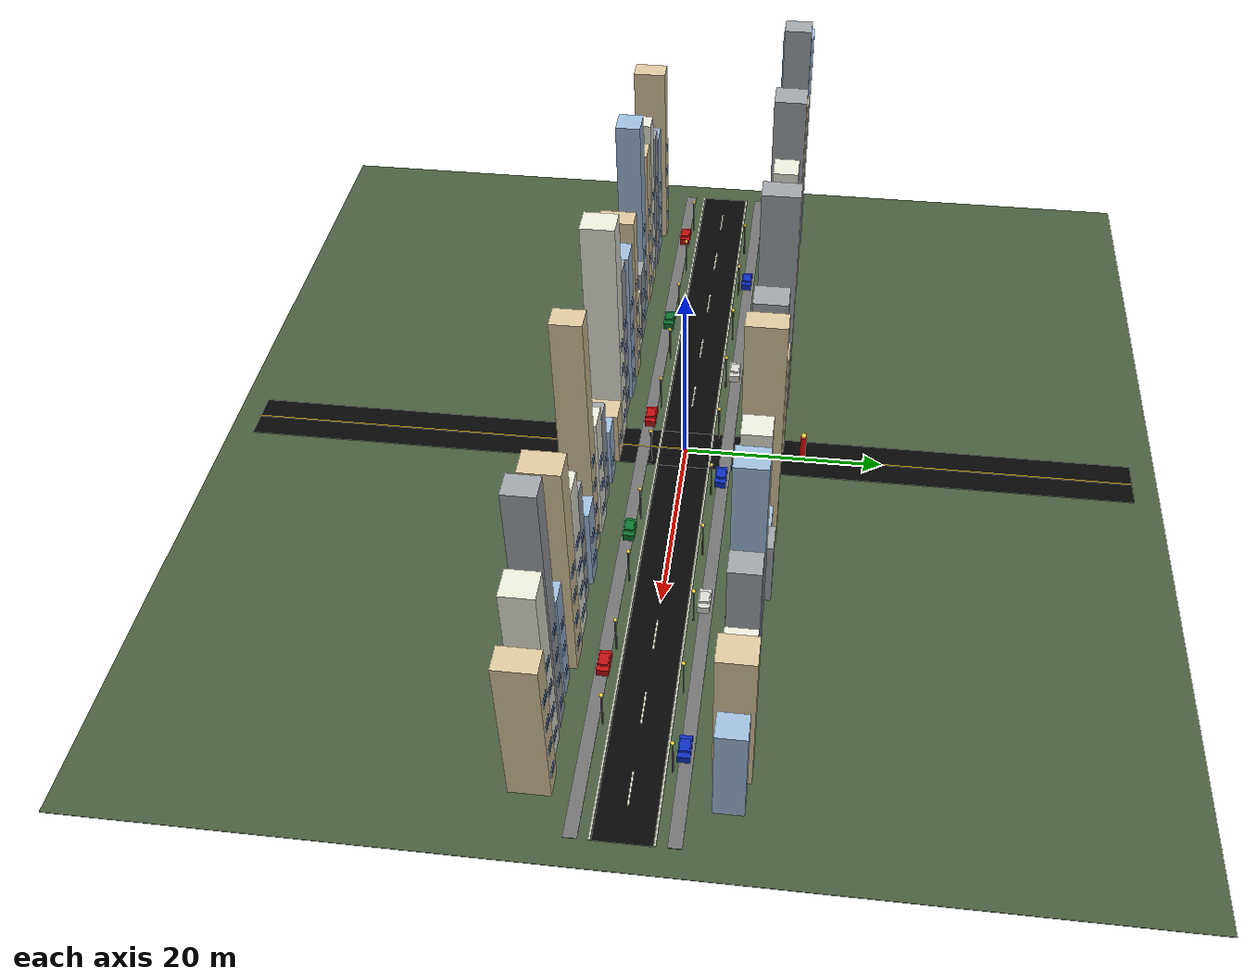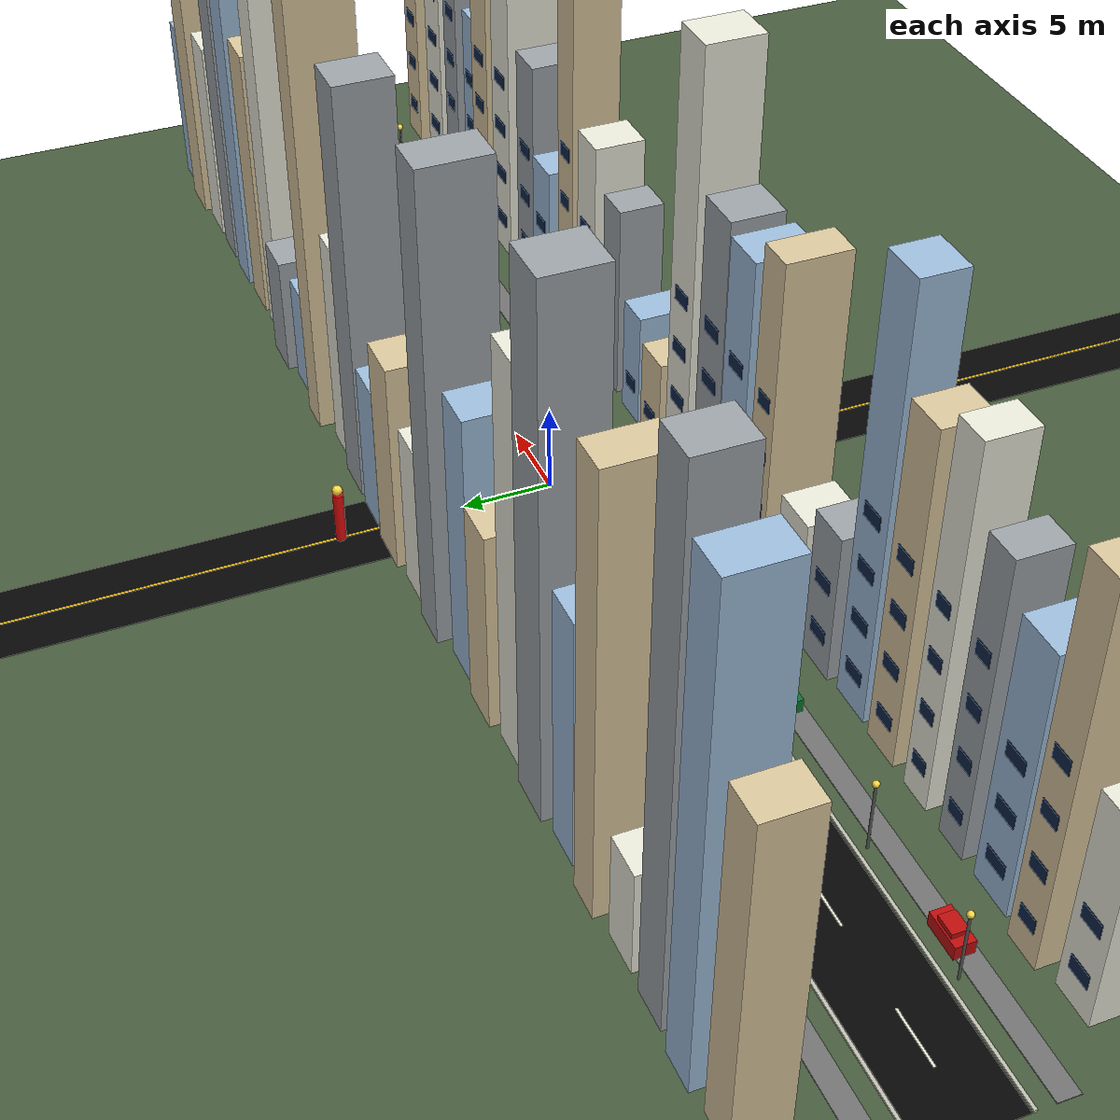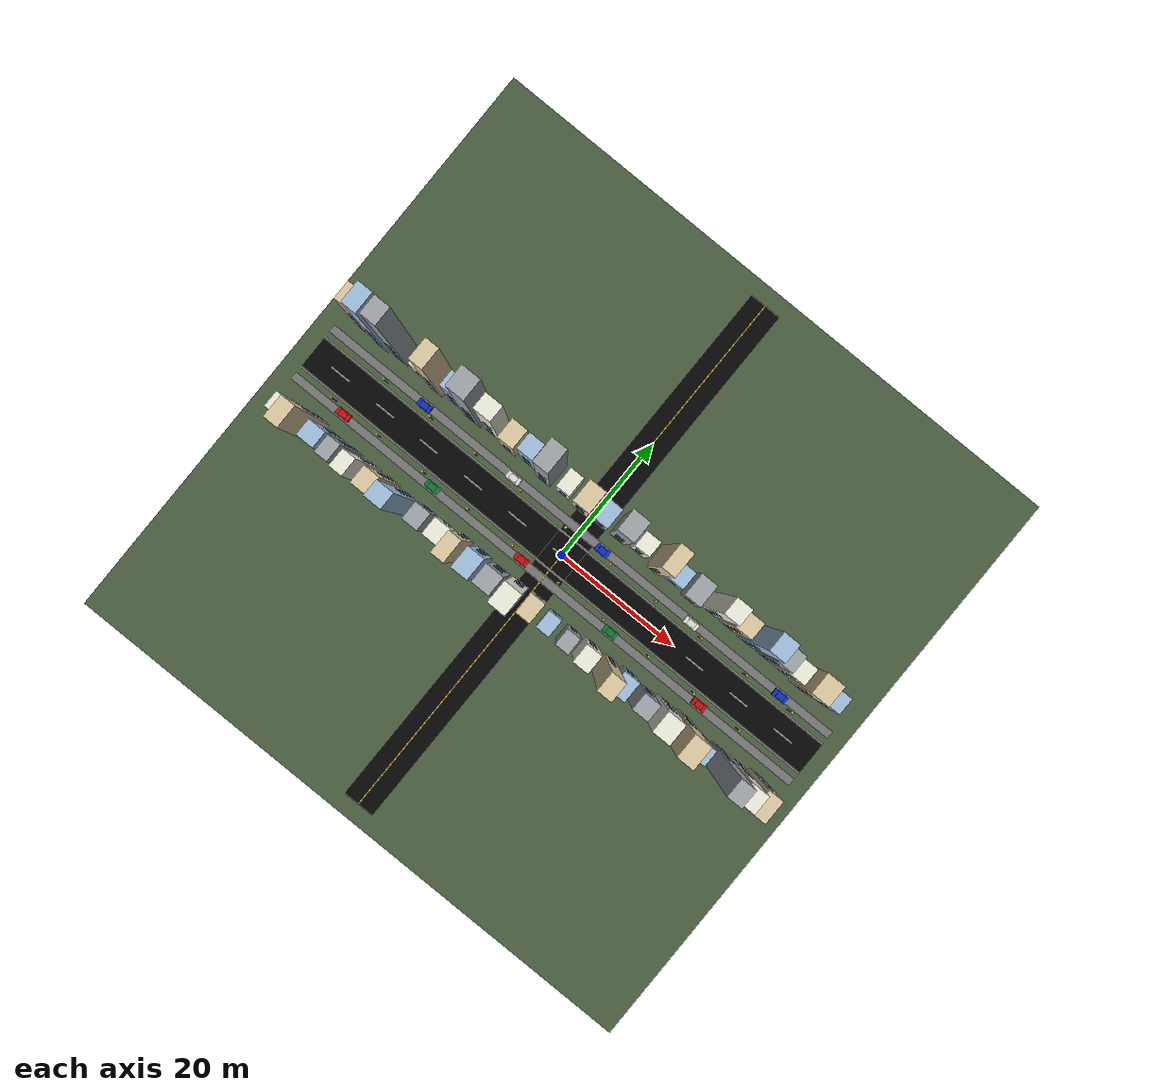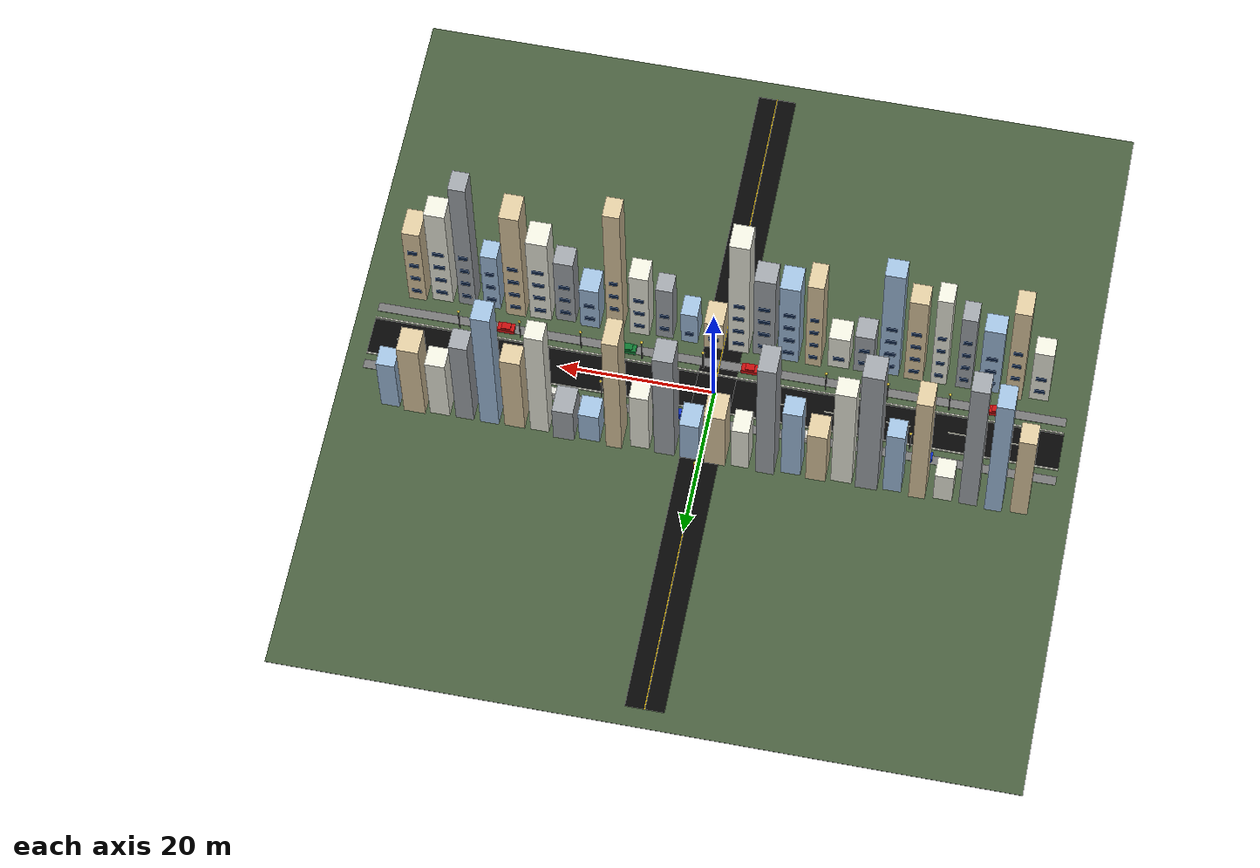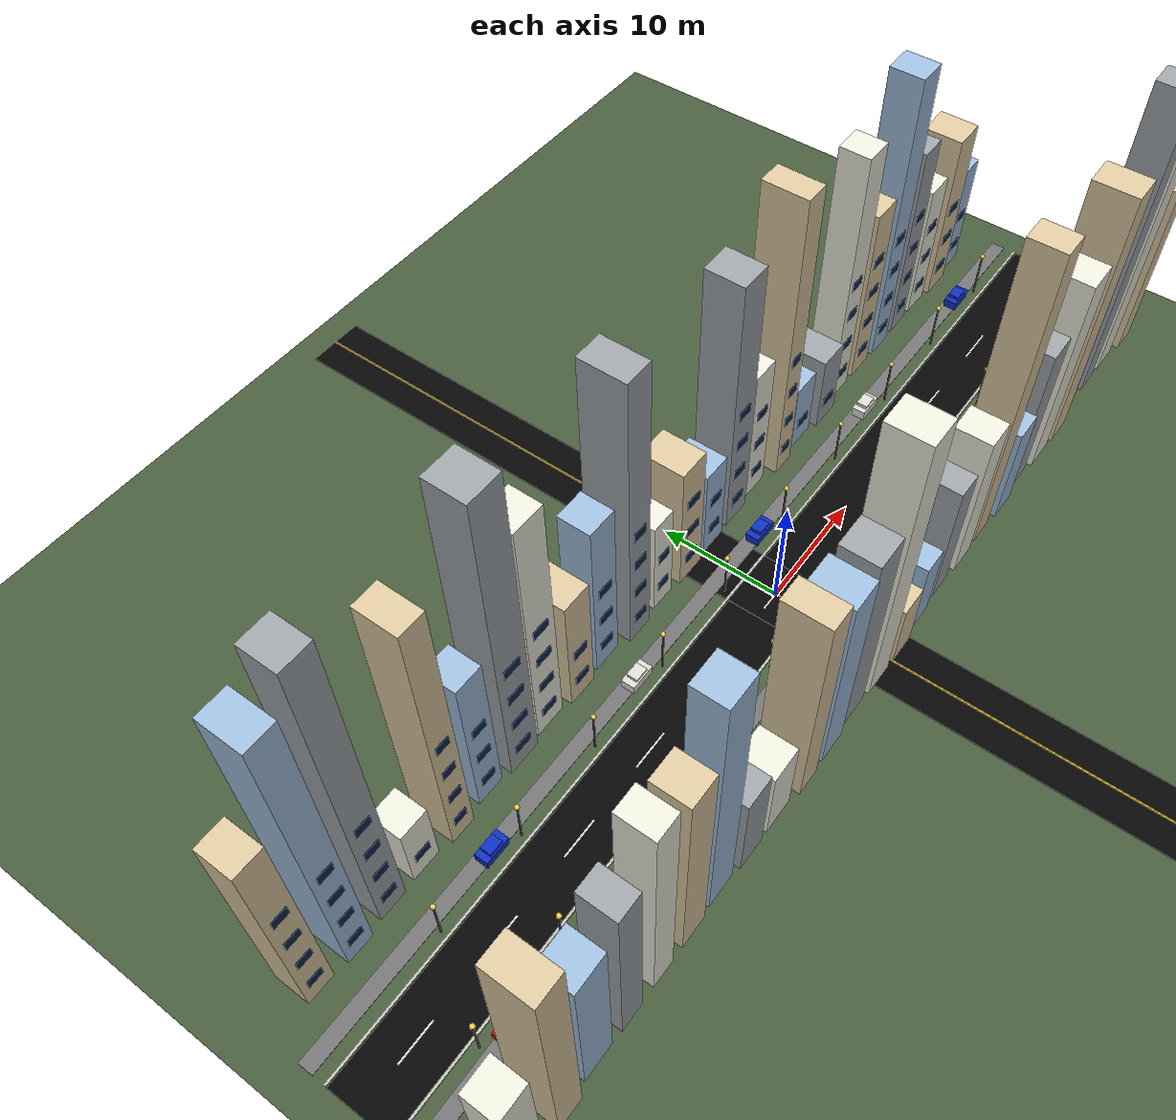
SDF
<?xml version="1.0" ?>
<sdf version="1.7">
  <world name="urban_street">
    <physics name="default_physics" type="ode">
      <max_step_size>0.001</max_step_size>
      <real_time_factor>1.0</real_time_factor>
    </physics>
    <plugin
        filename="gz-sim-physics-system"
        name="gz::sim::systems::Physics"/>

    <plugin
        filename="gz-sim-user-commands-system"
        name="gz::sim::systems::UserCommands"/>

    <plugin
        filename="gz-sim-scene-broadcaster-system"
        name="gz::sim::systems::SceneBroadcaster"/>

    <plugin
        filename="gz-sim-sensors-system"
        name="gz::sim::systems::Sensors">
      <render_engine>ogre2</render_engine>
    </plugin>

    <plugin
        filename="gz-sim-particle-emitter-system"
        name="gz::sim::systems::ParticleEmitter"/>

    <!-- Rest of your world elements (scene, lights, roads, buildings, etc.) remain below... -->

    <scene>
      <background>0.7 0.7 0.7 1.0</background>
      <ambient>0.5 0.5 0.5 1.0</ambient>
      <fog>
        <type>exp2</type>
        <color>0.7 0.7 0.7 1.0</color>
        <density>0.08</density>
      </fog>
    </scene>

    <light name="sun" type="directional">
      <pose>0 0 30 0 0 0</pose>
      <diffuse>0.9 0.9 0.85 1</diffuse>
      <specular>0.2 0.2 0.2 1</specular>
      <direction>-0.4 0.2 -0.9</direction>
    </light>

    <model name="green_ground">
      <static>true</static>
      <pose>0 0 -0.08 0 0 0.0</pose>
      <link name="link">
        <collision name="collision">
          <geometry>
            <box>
              <size>95 95 0.08</size>
            </box>
          </geometry>
        </collision>
        <visual name="visual">
          <geometry>
            <box>
              <size>95 95 0.08</size>
            </box>
          </geometry>
          <material>
            <ambient>0.28 0.36 0.24 1</ambient>
            <diffuse>0.28 0.36 0.24 1</diffuse>
            <specular>0.1 0.1 0.1 1</specular>
          </material>
        </visual>
      </link>
    </model>

    <model name="main_asphalt_road">
      <static>true</static>
      <pose>0 0 0.01 0 0 0.0</pose>
      <link name="link">
        <collision name="collision">
          <geometry>
            <box>
              <size>90 5.0 0.04</size>
            </box>
          </geometry>
        </collision>
        <visual name="visual">
          <geometry>
            <box>
              <size>90 5.0 0.04</size>
            </box>
          </geometry>
          <material>
            <ambient>0.02 0.02 0.02 1</ambient>
            <diffuse>0.02 0.02 0.02 1</diffuse>
            <specular>0.1 0.1 0.1 1</specular>
          </material>
        </visual>
      </link>
    </model>

    <model name="cross_asphalt_road">
      <static>true</static>
      <pose>0 0 0.02 0 0 0.0</pose>
      <link name="link">
        <collision name="collision">
          <geometry>
            <box>
              <size>5.0 90 0.04</size>
            </box>
          </geometry>
        </collision>
        <visual name="visual">
          <geometry>
            <box>
              <size>5.0 90 0.04</size>
            </box>
          </geometry>
          <material>
            <ambient>0.02 0.02 0.02 1</ambient>
            <diffuse>0.02 0.02 0.02 1</diffuse>
            <specular>0.1 0.1 0.1 1</specular>
          </material>
        </visual>
      </link>
    </model>

    <model name="north_sidewalk">
      <static>true</static>
      <pose>0 4.25 0.04 0 0 0.0</pose>
      <link name="link">
        <collision name="collision">
          <geometry>
            <box>
              <size>90 1.2 0.06</size>
            </box>
          </geometry>
        </collision>
        <visual name="visual">
          <geometry>
            <box>
              <size>90 1.2 0.06</size>
            </box>
          </geometry>
          <material>
            <ambient>0.45 0.45 0.45 1</ambient>
            <diffuse>0.45 0.45 0.45 1</diffuse>
            <specular>0.1 0.1 0.1 1</specular>
          </material>
        </visual>
      </link>
    </model>

    <model name="south_sidewalk">
      <static>true</static>
      <pose>0 -4.25 0.04 0 0 0.0</pose>
      <link name="link">
        <collision name="collision">
          <geometry>
            <box>
              <size>90 1.2 0.06</size>
            </box>
          </geometry>
        </collision>
        <visual name="visual">
          <geometry>
            <box>
              <size>90 1.2 0.06</size>
            </box>
          </geometry>
          <material>
            <ambient>0.45 0.45 0.45 1</ambient>
            <diffuse>0.45 0.45 0.45 1</diffuse>
            <specular>0.1 0.1 0.1 1</specular>
          </material>
        </visual>
      </link>
    </model>

    <model name="north_kerb">
      <static>true</static>
      <pose>0 2.65 0.07 0 0 0.0</pose>
      <link name="link">
        <collision name="collision">
          <geometry>
            <box>
              <size>90 0.18 0.14</size>
            </box>
          </geometry>
        </collision>
        <visual name="visual">
          <geometry>
            <box>
              <size>90 0.18 0.14</size>
            </box>
          </geometry>
          <material>
            <ambient>0.75 0.75 0.70 1</ambient>
            <diffuse>0.75 0.75 0.70 1</diffuse>
            <specular>0.1 0.1 0.1 1</specular>
          </material>
        </visual>
      </link>
    </model>

    <model name="south_kerb">
      <static>true</static>
      <pose>0 -2.65 0.07 0 0 0.0</pose>
      <link name="link">
        <collision name="collision">
          <geometry>
            <box>
              <size>90 0.18 0.14</size>
            </box>
          </geometry>
        </collision>
        <visual name="visual">
          <geometry>
            <box>
              <size>90 0.18 0.14</size>
            </box>
          </geometry>
          <material>
            <ambient>0.75 0.75 0.70 1</ambient>
            <diffuse>0.75 0.75 0.70 1</diffuse>
            <specular>0.1 0.1 0.1 1</specular>
          </material>
        </visual>
      </link>
    </model>

    <model name="white_lane_marking_00">
      <static>true</static>
      <pose>-40 0 0.055 0 0 0.0</pose>
      <link name="link">
        <collision name="collision">
          <geometry>
            <box>
              <size>3.2 0.12 0.02</size>
            </box>
          </geometry>
        </collision>
        <visual name="visual">
          <geometry>
            <box>
              <size>3.2 0.12 0.02</size>
            </box>
          </geometry>
          <material>
            <ambient>0.95 0.95 0.85 1</ambient>
            <diffuse>0.95 0.95 0.85 1</diffuse>
            <specular>0.1 0.1 0.1 1</specular>
          </material>
        </visual>
      </link>
    </model>

    <model name="white_lane_marking_01">
      <static>true</static>
      <pose>-32 0 0.055 0 0 0.0</pose>
      <link name="link">
        <collision name="collision">
          <geometry>
            <box>
              <size>3.2 0.12 0.02</size>
            </box>
          </geometry>
        </collision>
        <visual name="visual">
          <geometry>
            <box>
              <size>3.2 0.12 0.02</size>
            </box>
          </geometry>
          <material>
            <ambient>0.95 0.95 0.85 1</ambient>
            <diffuse>0.95 0.95 0.85 1</diffuse>
            <specular>0.1 0.1 0.1 1</specular>
          </material>
        </visual>
      </link>
    </model>

    <model name="white_lane_marking_02">
      <static>true</static>
      <pose>-24 0 0.055 0 0 0.0</pose>
      <link name="link">
        <collision name="collision">
          <geometry>
            <box>
              <size>3.2 0.12 0.02</size>
            </box>
          </geometry>
        </collision>
        <visual name="visual">
          <geometry>
            <box>
              <size>3.2 0.12 0.02</size>
            </box>
          </geometry>
          <material>
            <ambient>0.95 0.95 0.85 1</ambient>
            <diffuse>0.95 0.95 0.85 1</diffuse>
            <specular>0.1 0.1 0.1 1</specular>
          </material>
        </visual>
      </link>
    </model>

    <model name="white_lane_marking_03">
      <static>true</static>
      <pose>-16 0 0.055 0 0 0.0</pose>
      <link name="link">
        <collision name="collision">
          <geometry>
            <box>
              <size>3.2 0.12 0.02</size>
            </box>
          </geometry>
        </collision>
        <visual name="visual">
          <geometry>
            <box>
              <size>3.2 0.12 0.02</size>
            </box>
          </geometry>
          <material>
            <ambient>0.95 0.95 0.85 1</ambient>
            <diffuse>0.95 0.95 0.85 1</diffuse>
            <specular>0.1 0.1 0.1 1</specular>
          </material>
        </visual>
      </link>
    </model>

    <model name="white_lane_marking_04">
      <static>true</static>
      <pose>-8 0 0.055 0 0 0.0</pose>
      <link name="link">
        <collision name="collision">
          <geometry>
            <box>
              <size>3.2 0.12 0.02</size>
            </box>
          </geometry>
        </collision>
        <visual name="visual">
          <geometry>
            <box>
              <size>3.2 0.12 0.02</size>
            </box>
          </geometry>
          <material>
            <ambient>0.95 0.95 0.85 1</ambient>
            <diffuse>0.95 0.95 0.85 1</diffuse>
            <specular>0.1 0.1 0.1 1</specular>
          </material>
        </visual>
      </link>
    </model>

    <model name="white_lane_marking_05">
      <static>true</static>
      <pose>0 0 0.055 0 0 0.0</pose>
      <link name="link">
        <collision name="collision">
          <geometry>
            <box>
              <size>3.2 0.12 0.02</size>
            </box>
          </geometry>
        </collision>
        <visual name="visual">
          <geometry>
            <box>
              <size>3.2 0.12 0.02</size>
            </box>
          </geometry>
          <material>
            <ambient>0.95 0.95 0.85 1</ambient>
            <diffuse>0.95 0.95 0.85 1</diffuse>
            <specular>0.1 0.1 0.1 1</specular>
          </material>
        </visual>
      </link>
    </model>

    <model name="white_lane_marking_06">
      <static>true</static>
      <pose>8 0 0.055 0 0 0.0</pose>
      <link name="link">
        <collision name="collision">
          <geometry>
            <box>
              <size>3.2 0.12 0.02</size>
            </box>
          </geometry>
        </collision>
        <visual name="visual">
          <geometry>
            <box>
              <size>3.2 0.12 0.02</size>
            </box>
          </geometry>
          <material>
            <ambient>0.95 0.95 0.85 1</ambient>
            <diffuse>0.95 0.95 0.85 1</diffuse>
            <specular>0.1 0.1 0.1 1</specular>
          </material>
        </visual>
      </link>
    </model>

    <model name="white_lane_marking_07">
      <static>true</static>
      <pose>16 0 0.055 0 0 0.0</pose>
      <link name="link">
        <collision name="collision">
          <geometry>
            <box>
              <size>3.2 0.12 0.02</size>
            </box>
          </geometry>
        </collision>
        <visual name="visual">
          <geometry>
            <box>
              <size>3.2 0.12 0.02</size>
            </box>
          </geometry>
          <material>
            <ambient>0.95 0.95 0.85 1</ambient>
            <diffuse>0.95 0.95 0.85 1</diffuse>
            <specular>0.1 0.1 0.1 1</specular>
          </material>
        </visual>
      </link>
    </model>

    <model name="white_lane_marking_08">
      <static>true</static>
      <pose>24 0 0.055 0 0 0.0</pose>
      <link name="link">
        <collision name="collision">
          <geometry>
            <box>
              <size>3.2 0.12 0.02</size>
            </box>
          </geometry>
        </collision>
        <visual name="visual">
          <geometry>
            <box>
              <size>3.2 0.12 0.02</size>
            </box>
          </geometry>
          <material>
            <ambient>0.95 0.95 0.85 1</ambient>
            <diffuse>0.95 0.95 0.85 1</diffuse>
            <specular>0.1 0.1 0.1 1</specular>
          </material>
        </visual>
      </link>
    </model>

    <model name="white_lane_marking_09">
      <static>true</static>
      <pose>32 0 0.055 0 0 0.0</pose>
      <link name="link">
        <collision name="collision">
          <geometry>
            <box>
              <size>3.2 0.12 0.02</size>
            </box>
          </geometry>
        </collision>
        <visual name="visual">
          <geometry>
            <box>
              <size>3.2 0.12 0.02</size>
            </box>
          </geometry>
          <material>
            <ambient>0.95 0.95 0.85 1</ambient>
            <diffuse>0.95 0.95 0.85 1</diffuse>
            <specular>0.1 0.1 0.1 1</specular>
          </material>
        </visual>
      </link>
    </model>

    <model name="white_lane_marking_10">
      <static>true</static>
      <pose>40 0 0.055 0 0 0.0</pose>
      <link name="link">
        <collision name="collision">
          <geometry>
            <box>
              <size>3.2 0.12 0.02</size>
            </box>
          </geometry>
        </collision>
        <visual name="visual">
          <geometry>
            <box>
              <size>3.2 0.12 0.02</size>
            </box>
          </geometry>
          <material>
            <ambient>0.95 0.95 0.85 1</ambient>
            <diffuse>0.95 0.95 0.85 1</diffuse>
            <specular>0.1 0.1 0.1 1</specular>
          </material>
        </visual>
      </link>
    </model>

    <model name="yellow_cross_lane">
      <static>true</static>
      <pose>0 0 0.065 0 0 0.0</pose>
      <link name="link">
        <collision name="collision">
          <geometry>
            <box>
              <size>0.12 90 0.02</size>
            </box>
          </geometry>
        </collision>
        <visual name="visual">
          <geometry>
            <box>
              <size>0.12 90 0.02</size>
            </box>
          </geometry>
          <material>
            <ambient>1.0 0.78 0.05 1</ambient>
            <diffuse>1.0 0.78 0.05 1</diffuse>
            <specular>0.1 0.1 0.1 1</specular>
          </material>
        </visual>
      </link>
    </model>

    <model name="building_facade_01">
      <static>true</static>
      <pose>-41.0 -8.2 5.94 0 0 0.0</pose>
      <link name="link">
        <collision name="collision">
          <geometry>
            <box>
              <size>2.51 2.53 11.88</size>
            </box>
          </geometry>
        </collision>
        <visual name="visual">
          <geometry>
            <box>
              <size>2.51 2.53 11.88</size>
            </box>
          </geometry>
          <material>
            <ambient>0.92 0.92 0.86 1</ambient>
            <diffuse>0.92 0.92 0.86 1</diffuse>
            <specular>0.1 0.1 0.1 1</specular>
          </material>
        </visual>
      </link>
    </model>

    <model name="building_facade_01_window_0">
      <static>true</static>
      <pose>-41.0 -6.9 2.2 0 0 0.0</pose>
      <link name="link">
        <collision name="collision">
          <geometry>
            <box>
              <size>1.38 0.05 0.85</size>
            </box>
          </geometry>
        </collision>
        <visual name="visual">
          <geometry>
            <box>
              <size>1.38 0.05 0.85</size>
            </box>
          </geometry>
          <material>
            <ambient>0.05 0.14 0.28 1</ambient>
            <diffuse>0.05 0.14 0.28 1</diffuse>
            <specular>0.1 0.1 0.1 1</specular>
          </material>
        </visual>
      </link>
    </model>

    <model name="building_facade_01_window_1">
      <static>true</static>
      <pose>-41.0 -6.9 5.4 0 0 0.0</pose>
      <link name="link">
        <collision name="collision">
          <geometry>
            <box>
              <size>1.38 0.05 0.85</size>
            </box>
          </geometry>
        </collision>
        <visual name="visual">
          <geometry>
            <box>
              <size>1.38 0.05 0.85</size>
            </box>
          </geometry>
          <material>
            <ambient>0.05 0.14 0.28 1</ambient>
            <diffuse>0.05 0.14 0.28 1</diffuse>
            <specular>0.1 0.1 0.1 1</specular>
          </material>
        </visual>
      </link>
    </model>

    <model name="building_facade_02">
      <static>true</static>
      <pose>-37.75 -8.2 10.96 0 0 0.0</pose>
      <link name="link">
        <collision name="collision">
          <geometry>
            <box>
              <size>2.18 3.46 21.92</size>
            </box>
          </geometry>
        </collision>
        <visual name="visual">
          <geometry>
            <box>
              <size>2.18 3.46 21.92</size>
            </box>
          </geometry>
          <material>
            <ambient>0.86 0.78 0.62 1</ambient>
            <diffuse>0.86 0.78 0.62 1</diffuse>
            <specular>0.1 0.1 0.1 1</specular>
          </material>
        </visual>
      </link>
    </model>

    <model name="building_facade_02_window_0">
      <static>true</static>
      <pose>-37.75 -6.44 2.2 0 0 0.0</pose>
      <link name="link">
        <collision name="collision">
          <geometry>
            <box>
              <size>1.2 0.05 0.85</size>
            </box>
          </geometry>
        </collision>
        <visual name="visual">
          <geometry>
            <box>
              <size>1.2 0.05 0.85</size>
            </box>
          </geometry>
          <material>
            <ambient>0.05 0.14 0.28 1</ambient>
            <diffuse>0.05 0.14 0.28 1</diffuse>
            <specular>0.1 0.1 0.1 1</specular>
          </material>
        </visual>
      </link>
    </model>

    <model name="building_facade_02_window_1">
      <static>true</static>
      <pose>-37.75 -6.44 5.4 0 0 0.0</pose>
      <link name="link">
        <collision name="collision">
          <geometry>
            <box>
              <size>1.2 0.05 0.85</size>
            </box>
          </geometry>
        </collision>
        <visual name="visual">
          <geometry>
            <box>
              <size>1.2 0.05 0.85</size>
            </box>
          </geometry>
          <material>
            <ambient>0.05 0.14 0.28 1</ambient>
            <diffuse>0.05 0.14 0.28 1</diffuse>
            <specular>0.1 0.1 0.1 1</specular>
          </material>
        </visual>
      </link>
    </model>

    <model name="building_facade_02_window_2">
      <static>true</static>
      <pose>-37.75 -6.44 8.6 0 0 0.0</pose>
      <link name="link">
        <collision name="collision">
          <geometry>
            <box>
              <size>1.2 0.05 0.85</size>
            </box>
          </geometry>
        </collision>
        <visual name="visual">
          <geometry>
            <box>
              <size>1.2 0.05 0.85</size>
            </box>
          </geometry>
          <material>
            <ambient>0.05 0.14 0.28 1</ambient>
            <diffuse>0.05 0.14 0.28 1</diffuse>
            <specular>0.1 0.1 0.1 1</specular>
          </material>
        </visual>
      </link>
    </model>

    <model name="building_facade_02_window_3">
      <static>true</static>
      <pose>-37.75 -6.44 11.8 0 0 0.0</pose>
      <link name="link">
        <collision name="collision">
          <geometry>
            <box>
              <size>1.2 0.05 0.85</size>
            </box>
          </geometry>
        </collision>
        <visual name="visual">
          <geometry>
            <box>
              <size>1.2 0.05 0.85</size>
            </box>
          </geometry>
          <material>
            <ambient>0.05 0.14 0.28 1</ambient>
            <diffuse>0.05 0.14 0.28 1</diffuse>
            <specular>0.1 0.1 0.1 1</specular>
          </material>
        </visual>
      </link>
    </model>

    <model name="building_facade_03">
      <static>true</static>
      <pose>-34.5 -8.2 7.77 0 0 0.0</pose>
      <link name="link">
        <collision name="collision">
          <geometry>
            <box>
              <size>2.71 2.61 15.55</size>
            </box>
          </geometry>
        </collision>
        <visual name="visual">
          <geometry>
            <box>
              <size>2.71 2.61 15.55</size>
            </box>
          </geometry>
          <material>
            <ambient>0.62 0.74 0.86 1</ambient>
            <diffuse>0.62 0.74 0.86 1</diffuse>
            <specular>0.1 0.1 0.1 1</specular>
          </material>
        </visual>
      </link>
    </model>

    <model name="building_facade_03_window_0">
      <static>true</static>
      <pose>-34.5 -6.86 2.2 0 0 0.0</pose>
      <link name="link">
        <collision name="collision">
          <geometry>
            <box>
              <size>1.49 0.05 0.85</size>
            </box>
          </geometry>
        </collision>
        <visual name="visual">
          <geometry>
            <box>
              <size>1.49 0.05 0.85</size>
            </box>
          </geometry>
          <material>
            <ambient>0.05 0.14 0.28 1</ambient>
            <diffuse>0.05 0.14 0.28 1</diffuse>
            <specular>0.1 0.1 0.1 1</specular>
          </material>
        </visual>
      </link>
    </model>

    <model name="building_facade_03_window_1">
      <static>true</static>
      <pose>-34.5 -6.86 5.4 0 0 0.0</pose>
      <link name="link">
        <collision name="collision">
          <geometry>
            <box>
              <size>1.49 0.05 0.85</size>
            </box>
          </geometry>
        </collision>
        <visual name="visual">
          <geometry>
            <box>
              <size>1.49 0.05 0.85</size>
            </box>
          </geometry>
          <material>
            <ambient>0.05 0.14 0.28 1</ambient>
            <diffuse>0.05 0.14 0.28 1</diffuse>
            <specular>0.1 0.1 0.1 1</specular>
          </material>
        </visual>
      </link>
    </model>

    <model name="building_facade_03_window_2">
      <static>true</static>
      <pose>-34.5 -6.86 8.6 0 0 0.0</pose>
      <link name="link">
        <collision name="collision">
          <geometry>
            <box>
              <size>1.49 0.05 0.85</size>
            </box>
          </geometry>
        </collision>
        <visual name="visual">
          <geometry>
            <box>
              <size>1.49 0.05 0.85</size>
            </box>
          </geometry>
          <material>
            <ambient>0.05 0.14 0.28 1</ambient>
            <diffuse>0.05 0.14 0.28 1</diffuse>
            <specular>0.1 0.1 0.1 1</specular>
          </material>
        </visual>
      </link>
    </model>

    <model name="building_facade_04">
      <static>true</static>
      <pose>-31.25 -8.2 8.82 0 0 0.0</pose>
      <link name="link">
        <collision name="collision">
          <geometry>
            <box>
              <size>2.02 2.78 17.63</size>
            </box>
          </geometry>
        </collision>
        <visual name="visual">
          <geometry>
            <box>
              <size>2.02 2.78 17.63</size>
            </box>
          </geometry>
          <material>
            <ambient>0.62 0.64 0.66 1</ambient>
            <diffuse>0.62 0.64 0.66 1</diffuse>
            <specular>0.1 0.1 0.1 1</specular>
          </material>
        </visual>
      </link>
    </model>

    <model name="building_facade_04_window_0">
      <static>true</static>
      <pose>-31.25 -6.78 2.2 0 0 0.0</pose>
      <link name="link">
        <collision name="collision">
          <geometry>
            <box>
              <size>1.11 0.05 0.85</size>
            </box>
          </geometry>
        </collision>
        <visual name="visual">
          <geometry>
            <box>
              <size>1.11 0.05 0.85</size>
            </box>
          </geometry>
          <material>
            <ambient>0.05 0.14 0.28 1</ambient>
            <diffuse>0.05 0.14 0.28 1</diffuse>
            <specular>0.1 0.1 0.1 1</specular>
          </material>
        </visual>
      </link>
    </model>

    <model name="building_facade_04_window_1">
      <static>true</static>
      <pose>-31.25 -6.78 5.4 0 0 0.0</pose>
      <link name="link">
        <collision name="collision">
          <geometry>
            <box>
              <size>1.11 0.05 0.85</size>
            </box>
          </geometry>
        </collision>
        <visual name="visual">
          <geometry>
            <box>
              <size>1.11 0.05 0.85</size>
            </box>
          </geometry>
          <material>
            <ambient>0.05 0.14 0.28 1</ambient>
            <diffuse>0.05 0.14 0.28 1</diffuse>
            <specular>0.1 0.1 0.1 1</specular>
          </material>
        </visual>
      </link>
    </model>

    <model name="building_facade_04_window_2">
      <static>true</static>
      <pose>-31.25 -6.78 8.6 0 0 0.0</pose>
      <link name="link">
        <collision name="collision">
          <geometry>
            <box>
              <size>1.11 0.05 0.85</size>
            </box>
          </geometry>
        </collision>
        <visual name="visual">
          <geometry>
            <box>
              <size>1.11 0.05 0.85</size>
            </box>
          </geometry>
          <material>
            <ambient>0.05 0.14 0.28 1</ambient>
            <diffuse>0.05 0.14 0.28 1</diffuse>
            <specular>0.1 0.1 0.1 1</specular>
          </material>
        </visual>
      </link>
    </model>

    <model name="building_facade_04_window_3">
      <static>true</static>
      <pose>-31.25 -6.78 11.8 0 0 0.0</pose>
      <link name="link">
        <collision name="collision">
          <geometry>
            <box>
              <size>1.11 0.05 0.85</size>
            </box>
          </geometry>
        </collision>
        <visual name="visual">
          <geometry>
            <box>
              <size>1.11 0.05 0.85</size>
            </box>
          </geometry>
          <material>
            <ambient>0.05 0.14 0.28 1</ambient>
            <diffuse>0.05 0.14 0.28 1</diffuse>
            <specular>0.1 0.1 0.1 1</specular>
          </material>
        </visual>
      </link>
    </model>

    <model name="building_facade_05">
      <static>true</static>
      <pose>-28.0 -8.2 10.62 0 0 0.0</pose>
      <link name="link">
        <collision name="collision">
          <geometry>
            <box>
              <size>2.02 2.76 21.25</size>
            </box>
          </geometry>
        </collision>
        <visual name="visual">
          <geometry>
            <box>
              <size>2.02 2.76 21.25</size>
            </box>
          </geometry>
          <material>
            <ambient>0.92 0.92 0.86 1</ambient>
            <diffuse>0.92 0.92 0.86 1</diffuse>
            <specular>0.1 0.1 0.1 1</specular>
          </material>
        </visual>
      </link>
    </model>

    <model name="building_facade_05_window_0">
      <static>true</static>
      <pose>-28.0 -6.79 2.2 0 0 0.0</pose>
      <link name="link">
        <collision name="collision">
          <geometry>
            <box>
              <size>1.11 0.05 0.85</size>
            </box>
          </geometry>
        </collision>
        <visual name="visual">
          <geometry>
            <box>
              <size>1.11 0.05 0.85</size>
            </box>
          </geometry>
          <material>
            <ambient>0.05 0.14 0.28 1</ambient>
            <diffuse>0.05 0.14 0.28 1</diffuse>
            <specular>0.1 0.1 0.1 1</specular>
          </material>
        </visual>
      </link>
    </model>

    <model name="building_facade_05_window_1">
      <static>true</static>
      <pose>-28.0 -6.79 5.4 0 0 0.0</pose>
      <link name="link">
        <collision name="collision">
          <geometry>
            <box>
              <size>1.11 0.05 0.85</size>
            </box>
          </geometry>
        </collision>
        <visual name="visual">
          <geometry>
            <box>
              <size>1.11 0.05 0.85</size>
            </box>
          </geometry>
          <material>
            <ambient>0.05 0.14 0.28 1</ambient>
            <diffuse>0.05 0.14 0.28 1</diffuse>
            <specular>0.1 0.1 0.1 1</specular>
          </material>
        </visual>
      </link>
    </model>

    <model name="building_facade_05_window_2">
      <static>true</static>
      <pose>-28.0 -6.79 8.6 0 0 0.0</pose>
      <link name="link">
        <collision name="collision">
          <geometry>
            <box>
              <size>1.11 0.05 0.85</size>
            </box>
          </geometry>
        </collision>
        <visual name="visual">
          <geometry>
            <box>
              <size>1.11 0.05 0.85</size>
            </box>
          </geometry>
          <material>
            <ambient>0.05 0.14 0.28 1</ambient>
            <diffuse>0.05 0.14 0.28 1</diffuse>
            <specular>0.1 0.1 0.1 1</specular>
          </material>
        </visual>
      </link>
    </model>

    <model name="building_facade_05_window_3">
      <static>true</static>
      <pose>-28.0 -6.79 11.8 0 0 0.0</pose>
      <link name="link">
        <collision name="collision">
          <geometry>
            <box>
              <size>1.11 0.05 0.85</size>
            </box>
          </geometry>
        </collision>
        <visual name="visual">
          <geometry>
            <box>
              <size>1.11 0.05 0.85</size>
            </box>
          </geometry>
          <material>
            <ambient>0.05 0.14 0.28 1</ambient>
            <diffuse>0.05 0.14 0.28 1</diffuse>
            <specular>0.1 0.1 0.1 1</specular>
          </material>
        </visual>
      </link>
    </model>

    <model name="building_facade_06">
      <static>true</static>
      <pose>-24.75 -8.2 9.87 0 0 0.0</pose>
      <link name="link">
        <collision name="collision">
          <geometry>
            <box>
              <size>2.44 2.79 19.73</size>
            </box>
          </geometry>
        </collision>
        <visual name="visual">
          <geometry>
            <box>
              <size>2.44 2.79 19.73</size>
            </box>
          </geometry>
          <material>
            <ambient>0.86 0.78 0.62 1</ambient>
            <diffuse>0.86 0.78 0.62 1</diffuse>
            <specular>0.1 0.1 0.1 1</specular>
          </material>
        </visual>
      </link>
    </model>

    <model name="building_facade_06_window_0">
      <static>true</static>
      <pose>-24.75 -6.78 2.2 0 0 0.0</pose>
      <link name="link">
        <collision name="collision">
          <geometry>
            <box>
              <size>1.34 0.05 0.85</size>
            </box>
          </geometry>
        </collision>
        <visual name="visual">
          <geometry>
            <box>
              <size>1.34 0.05 0.85</size>
            </box>
          </geometry>
          <material>
            <ambient>0.05 0.14 0.28 1</ambient>
            <diffuse>0.05 0.14 0.28 1</diffuse>
            <specular>0.1 0.1 0.1 1</specular>
          </material>
        </visual>
      </link>
    </model>

    <model name="building_facade_06_window_1">
      <static>true</static>
      <pose>-24.75 -6.78 5.4 0 0 0.0</pose>
      <link name="link">
        <collision name="collision">
          <geometry>
            <box>
              <size>1.34 0.05 0.85</size>
            </box>
          </geometry>
        </collision>
        <visual name="visual">
          <geometry>
            <box>
              <size>1.34 0.05 0.85</size>
            </box>
          </geometry>
          <material>
            <ambient>0.05 0.14 0.28 1</ambient>
            <diffuse>0.05 0.14 0.28 1</diffuse>
            <specular>0.1 0.1 0.1 1</specular>
          </material>
        </visual>
      </link>
    </model>

    <model name="building_facade_06_window_2">
      <static>true</static>
      <pose>-24.75 -6.78 8.6 0 0 0.0</pose>
      <link name="link">
        <collision name="collision">
          <geometry>
            <box>
              <size>1.34 0.05 0.85</size>
            </box>
          </geometry>
        </collision>
        <visual name="visual">
          <geometry>
            <box>
              <size>1.34 0.05 0.85</size>
            </box>
          </geometry>
          <material>
            <ambient>0.05 0.14 0.28 1</ambient>
            <diffuse>0.05 0.14 0.28 1</diffuse>
            <specular>0.1 0.1 0.1 1</specular>
          </material>
        </visual>
      </link>
    </model>

    <model name="building_facade_06_window_3">
      <static>true</static>
      <pose>-24.75 -6.78 11.8 0 0 0.0</pose>
      <link name="link">
        <collision name="collision">
          <geometry>
            <box>
              <size>1.34 0.05 0.85</size>
            </box>
          </geometry>
        </collision>
        <visual name="visual">
          <geometry>
            <box>
              <size>1.34 0.05 0.85</size>
            </box>
          </geometry>
          <material>
            <ambient>0.05 0.14 0.28 1</ambient>
            <diffuse>0.05 0.14 0.28 1</diffuse>
            <specular>0.1 0.1 0.1 1</specular>
          </material>
        </visual>
      </link>
    </model>

    <model name="building_facade_07">
      <static>true</static>
      <pose>-21.5 -8.2 12.57 0 0 0.0</pose>
      <link name="link">
        <collision name="collision">
          <geometry>
            <box>
              <size>2.65 2.51 25.15</size>
            </box>
          </geometry>
        </collision>
        <visual name="visual">
          <geometry>
            <box>
              <size>2.65 2.51 25.15</size>
            </box>
          </geometry>
          <material>
            <ambient>0.62 0.74 0.86 1</ambient>
            <diffuse>0.62 0.74 0.86 1</diffuse>
            <specular>0.1 0.1 0.1 1</specular>
          </material>
        </visual>
      </link>
    </model>

    <model name="building_facade_07_window_0">
      <static>true</static>
      <pose>-21.5 -6.92 2.2 0 0 0.0</pose>
      <link name="link">
        <collision name="collision">
          <geometry>
            <box>
              <size>1.46 0.05 0.85</size>
            </box>
          </geometry>
        </collision>
        <visual name="visual">
          <geometry>
            <box>
              <size>1.46 0.05 0.85</size>
            </box>
          </geometry>
          <material>
            <ambient>0.05 0.14 0.28 1</ambient>
            <diffuse>0.05 0.14 0.28 1</diffuse>
            <specular>0.1 0.1 0.1 1</specular>
          </material>
        </visual>
      </link>
    </model>

    <model name="building_facade_07_window_1">
      <static>true</static>
      <pose>-21.5 -6.92 5.4 0 0 0.0</pose>
      <link name="link">
        <collision name="collision">
          <geometry>
            <box>
              <size>1.46 0.05 0.85</size>
            </box>
          </geometry>
        </collision>
        <visual name="visual">
          <geometry>
            <box>
              <size>1.46 0.05 0.85</size>
            </box>
          </geometry>
          <material>
            <ambient>0.05 0.14 0.28 1</ambient>
            <diffuse>0.05 0.14 0.28 1</diffuse>
            <specular>0.1 0.1 0.1 1</specular>
          </material>
        </visual>
      </link>
    </model>

    <model name="building_facade_07_window_2">
      <static>true</static>
      <pose>-21.5 -6.92 8.6 0 0 0.0</pose>
      <link name="link">
        <collision name="collision">
          <geometry>
            <box>
              <size>1.46 0.05 0.85</size>
            </box>
          </geometry>
        </collision>
        <visual name="visual">
          <geometry>
            <box>
              <size>1.46 0.05 0.85</size>
            </box>
          </geometry>
          <material>
            <ambient>0.05 0.14 0.28 1</ambient>
            <diffuse>0.05 0.14 0.28 1</diffuse>
            <specular>0.1 0.1 0.1 1</specular>
          </material>
        </visual>
      </link>
    </model>

    <model name="building_facade_07_window_3">
      <static>true</static>
      <pose>-21.5 -6.92 11.8 0 0 0.0</pose>
      <link name="link">
        <collision name="collision">
          <geometry>
            <box>
              <size>1.46 0.05 0.85</size>
            </box>
          </geometry>
        </collision>
        <visual name="visual">
          <geometry>
            <box>
              <size>1.46 0.05 0.85</size>
            </box>
          </geometry>
          <material>
            <ambient>0.05 0.14 0.28 1</ambient>
            <diffuse>0.05 0.14 0.28 1</diffuse>
            <specular>0.1 0.1 0.1 1</specular>
          </material>
        </visual>
      </link>
    </model>

    <model name="building_facade_08">
      <static>true</static>
      <pose>-18.25 -8.2 4.44 0 0 0.0</pose>
      <link name="link">
        <collision name="collision">
          <geometry>
            <box>
              <size>2.56 2.94 8.89</size>
            </box>
          </geometry>
        </collision>
        <visual name="visual">
          <geometry>
            <box>
              <size>2.56 2.94 8.89</size>
            </box>
          </geometry>
          <material>
            <ambient>0.62 0.64 0.66 1</ambient>
            <diffuse>0.62 0.64 0.66 1</diffuse>
            <specular>0.1 0.1 0.1 1</specular>
          </material>
        </visual>
      </link>
    </model>

    <model name="building_facade_08_window_0">
      <static>true</static>
      <pose>-18.25 -6.7 2.2 0 0 0.0</pose>
      <link name="link">
        <collision name="collision">
          <geometry>
            <box>
              <size>1.41 0.05 0.85</size>
            </box>
          </geometry>
        </collision>
        <visual name="visual">
          <geometry>
            <box>
              <size>1.41 0.05 0.85</size>
            </box>
          </geometry>
          <material>
            <ambient>0.05 0.14 0.28 1</ambient>
            <diffuse>0.05 0.14 0.28 1</diffuse>
            <specular>0.1 0.1 0.1 1</specular>
          </material>
        </visual>
      </link>
    </model>

    <model name="building_facade_08_window_1">
      <static>true</static>
      <pose>-18.25 -6.7 5.4 0 0 0.0</pose>
      <link name="link">
        <collision name="collision">
          <geometry>
            <box>
              <size>1.41 0.05 0.85</size>
            </box>
          </geometry>
        </collision>
        <visual name="visual">
          <geometry>
            <box>
              <size>1.41 0.05 0.85</size>
            </box>
          </geometry>
          <material>
            <ambient>0.05 0.14 0.28 1</ambient>
            <diffuse>0.05 0.14 0.28 1</diffuse>
            <specular>0.1 0.1 0.1 1</specular>
          </material>
        </visual>
      </link>
    </model>

    <model name="building_facade_09">
      <static>true</static>
      <pose>-15.0 -8.2 3.66 0 0 0.0</pose>
      <link name="link">
        <collision name="collision">
          <geometry>
            <box>
              <size>2.77 2.94 7.32</size>
            </box>
          </geometry>
        </collision>
        <visual name="visual">
          <geometry>
            <box>
              <size>2.77 2.94 7.32</size>
            </box>
          </geometry>
          <material>
            <ambient>0.92 0.92 0.86 1</ambient>
            <diffuse>0.92 0.92 0.86 1</diffuse>
            <specular>0.1 0.1 0.1 1</specular>
          </material>
        </visual>
      </link>
    </model>

    <model name="building_facade_09_window_0">
      <static>true</static>
      <pose>-15.0 -6.7 2.2 0 0 0.0</pose>
      <link name="link">
        <collision name="collision">
          <geometry>
            <box>
              <size>1.52 0.05 0.85</size>
            </box>
          </geometry>
        </collision>
        <visual name="visual">
          <geometry>
            <box>
              <size>1.52 0.05 0.85</size>
            </box>
          </geometry>
          <material>
            <ambient>0.05 0.14 0.28 1</ambient>
            <diffuse>0.05 0.14 0.28 1</diffuse>
            <specular>0.1 0.1 0.1 1</specular>
          </material>
        </visual>
      </link>
    </model>

    <model name="building_facade_10">
      <static>true</static>
      <pose>-11.75 -8.2 10.05 0 0 0.0</pose>
      <link name="link">
        <collision name="collision">
          <geometry>
            <box>
              <size>2.08 3.6 20.09</size>
            </box>
          </geometry>
        </collision>
        <visual name="visual">
          <geometry>
            <box>
              <size>2.08 3.6 20.09</size>
            </box>
          </geometry>
          <material>
            <ambient>0.86 0.78 0.62 1</ambient>
            <diffuse>0.86 0.78 0.62 1</diffuse>
            <specular>0.1 0.1 0.1 1</specular>
          </material>
        </visual>
      </link>
    </model>

    <model name="building_facade_10_window_0">
      <static>true</static>
      <pose>-11.75 -6.37 2.2 0 0 0.0</pose>
      <link name="link">
        <collision name="collision">
          <geometry>
            <box>
              <size>1.14 0.05 0.85</size>
            </box>
          </geometry>
        </collision>
        <visual name="visual">
          <geometry>
            <box>
              <size>1.14 0.05 0.85</size>
            </box>
          </geometry>
          <material>
            <ambient>0.05 0.14 0.28 1</ambient>
            <diffuse>0.05 0.14 0.28 1</diffuse>
            <specular>0.1 0.1 0.1 1</specular>
          </material>
        </visual>
      </link>
    </model>

    <model name="building_facade_10_window_1">
      <static>true</static>
      <pose>-11.75 -6.37 5.4 0 0 0.0</pose>
      <link name="link">
        <collision name="collision">
          <geometry>
            <box>
              <size>1.14 0.05 0.85</size>
            </box>
          </geometry>
        </collision>
        <visual name="visual">
          <geometry>
            <box>
              <size>1.14 0.05 0.85</size>
            </box>
          </geometry>
          <material>
            <ambient>0.05 0.14 0.28 1</ambient>
            <diffuse>0.05 0.14 0.28 1</diffuse>
            <specular>0.1 0.1 0.1 1</specular>
          </material>
        </visual>
      </link>
    </model>

    <model name="building_facade_10_window_2">
      <static>true</static>
      <pose>-11.75 -6.37 8.6 0 0 0.0</pose>
      <link name="link">
        <collision name="collision">
          <geometry>
            <box>
              <size>1.14 0.05 0.85</size>
            </box>
          </geometry>
        </collision>
        <visual name="visual">
          <geometry>
            <box>
              <size>1.14 0.05 0.85</size>
            </box>
          </geometry>
          <material>
            <ambient>0.05 0.14 0.28 1</ambient>
            <diffuse>0.05 0.14 0.28 1</diffuse>
            <specular>0.1 0.1 0.1 1</specular>
          </material>
        </visual>
      </link>
    </model>

    <model name="building_facade_10_window_3">
      <static>true</static>
      <pose>-11.75 -6.37 11.8 0 0 0.0</pose>
      <link name="link">
        <collision name="collision">
          <geometry>
            <box>
              <size>1.14 0.05 0.85</size>
            </box>
          </geometry>
        </collision>
        <visual name="visual">
          <geometry>
            <box>
              <size>1.14 0.05 0.85</size>
            </box>
          </geometry>
          <material>
            <ambient>0.05 0.14 0.28 1</ambient>
            <diffuse>0.05 0.14 0.28 1</diffuse>
            <specular>0.1 0.1 0.1 1</specular>
          </material>
        </visual>
      </link>
    </model>

    <model name="building_facade_11">
      <static>true</static>
      <pose>-8.5 -8.2 9.2 0 0 0.0</pose>
      <link name="link">
        <collision name="collision">
          <geometry>
            <box>
              <size>2.65 3.45 18.41</size>
            </box>
          </geometry>
        </collision>
        <visual name="visual">
          <geometry>
            <box>
              <size>2.65 3.45 18.41</size>
            </box>
          </geometry>
          <material>
            <ambient>0.62 0.74 0.86 1</ambient>
            <diffuse>0.62 0.74 0.86 1</diffuse>
            <specular>0.1 0.1 0.1 1</specular>
          </material>
        </visual>
      </link>
    </model>

    <model name="building_facade_11_window_0">
      <static>true</static>
      <pose>-8.5 -6.45 2.2 0 0 0.0</pose>
      <link name="link">
        <collision name="collision">
          <geometry>
            <box>
              <size>1.46 0.05 0.85</size>
            </box>
          </geometry>
        </collision>
        <visual name="visual">
          <geometry>
            <box>
              <size>1.46 0.05 0.85</size>
            </box>
          </geometry>
          <material>
            <ambient>0.05 0.14 0.28 1</ambient>
            <diffuse>0.05 0.14 0.28 1</diffuse>
            <specular>0.1 0.1 0.1 1</specular>
          </material>
        </visual>
      </link>
    </model>

    <model name="building_facade_11_window_1">
      <static>true</static>
      <pose>-8.5 -6.45 5.4 0 0 0.0</pose>
      <link name="link">
        <collision name="collision">
          <geometry>
            <box>
              <size>1.46 0.05 0.85</size>
            </box>
          </geometry>
        </collision>
        <visual name="visual">
          <geometry>
            <box>
              <size>1.46 0.05 0.85</size>
            </box>
          </geometry>
          <material>
            <ambient>0.05 0.14 0.28 1</ambient>
            <diffuse>0.05 0.14 0.28 1</diffuse>
            <specular>0.1 0.1 0.1 1</specular>
          </material>
        </visual>
      </link>
    </model>

    <model name="building_facade_11_window_2">
      <static>true</static>
      <pose>-8.5 -6.45 8.6 0 0 0.0</pose>
      <link name="link">
        <collision name="collision">
          <geometry>
            <box>
              <size>1.46 0.05 0.85</size>
            </box>
          </geometry>
        </collision>
        <visual name="visual">
          <geometry>
            <box>
              <size>1.46 0.05 0.85</size>
            </box>
          </geometry>
          <material>
            <ambient>0.05 0.14 0.28 1</ambient>
            <diffuse>0.05 0.14 0.28 1</diffuse>
            <specular>0.1 0.1 0.1 1</specular>
          </material>
        </visual>
      </link>
    </model>

    <model name="building_facade_11_window_3">
      <static>true</static>
      <pose>-8.5 -6.45 11.8 0 0 0.0</pose>
      <link name="link">
        <collision name="collision">
          <geometry>
            <box>
              <size>1.46 0.05 0.85</size>
            </box>
          </geometry>
        </collision>
        <visual name="visual">
          <geometry>
            <box>
              <size>1.46 0.05 0.85</size>
            </box>
          </geometry>
          <material>
            <ambient>0.05 0.14 0.28 1</ambient>
            <diffuse>0.05 0.14 0.28 1</diffuse>
            <specular>0.1 0.1 0.1 1</specular>
          </material>
        </visual>
      </link>
    </model>

    <model name="building_facade_12">
      <static>true</static>
      <pose>-5.25 -8.2 9.4 0 0 0.0</pose>
      <link name="link">
        <collision name="collision">
          <geometry>
            <box>
              <size>2.78 2.99 18.8</size>
            </box>
          </geometry>
        </collision>
        <visual name="visual">
          <geometry>
            <box>
              <size>2.78 2.99 18.8</size>
            </box>
          </geometry>
          <material>
            <ambient>0.62 0.64 0.66 1</ambient>
            <diffuse>0.62 0.64 0.66 1</diffuse>
            <specular>0.1 0.1 0.1 1</specular>
          </material>
        </visual>
      </link>
    </model>

    <model name="building_facade_12_window_0">
      <static>true</static>
      <pose>-5.25 -6.67 2.2 0 0 0.0</pose>
      <link name="link">
        <collision name="collision">
          <geometry>
            <box>
              <size>1.53 0.05 0.85</size>
            </box>
          </geometry>
        </collision>
        <visual name="visual">
          <geometry>
            <box>
              <size>1.53 0.05 0.85</size>
            </box>
          </geometry>
          <material>
            <ambient>0.05 0.14 0.28 1</ambient>
            <diffuse>0.05 0.14 0.28 1</diffuse>
            <specular>0.1 0.1 0.1 1</specular>
          </material>
        </visual>
      </link>
    </model>

    <model name="building_facade_12_window_1">
      <static>true</static>
      <pose>-5.25 -6.67 5.4 0 0 0.0</pose>
      <link name="link">
        <collision name="collision">
          <geometry>
            <box>
              <size>1.53 0.05 0.85</size>
            </box>
          </geometry>
        </collision>
        <visual name="visual">
          <geometry>
            <box>
              <size>1.53 0.05 0.85</size>
            </box>
          </geometry>
          <material>
            <ambient>0.05 0.14 0.28 1</ambient>
            <diffuse>0.05 0.14 0.28 1</diffuse>
            <specular>0.1 0.1 0.1 1</specular>
          </material>
        </visual>
      </link>
    </model>

    <model name="building_facade_12_window_2">
      <static>true</static>
      <pose>-5.25 -6.67 8.6 0 0 0.0</pose>
      <link name="link">
        <collision name="collision">
          <geometry>
            <box>
              <size>1.53 0.05 0.85</size>
            </box>
          </geometry>
        </collision>
        <visual name="visual">
          <geometry>
            <box>
              <size>1.53 0.05 0.85</size>
            </box>
          </geometry>
          <material>
            <ambient>0.05 0.14 0.28 1</ambient>
            <diffuse>0.05 0.14 0.28 1</diffuse>
            <specular>0.1 0.1 0.1 1</specular>
          </material>
        </visual>
      </link>
    </model>

    <model name="building_facade_12_window_3">
      <static>true</static>
      <pose>-5.25 -6.67 11.8 0 0 0.0</pose>
      <link name="link">
        <collision name="collision">
          <geometry>
            <box>
              <size>1.53 0.05 0.85</size>
            </box>
          </geometry>
        </collision>
        <visual name="visual">
          <geometry>
            <box>
              <size>1.53 0.05 0.85</size>
            </box>
          </geometry>
          <material>
            <ambient>0.05 0.14 0.28 1</ambient>
            <diffuse>0.05 0.14 0.28 1</diffuse>
            <specular>0.1 0.1 0.1 1</specular>
          </material>
        </visual>
      </link>
    </model>

    <model name="building_facade_13">
      <static>true</static>
      <pose>-2.0 -8.2 13.27 0 0 0.0</pose>
      <link name="link">
        <collision name="collision">
          <geometry>
            <box>
              <size>2.66 3.3 26.54</size>
            </box>
          </geometry>
        </collision>
        <visual name="visual">
          <geometry>
            <box>
              <size>2.66 3.3 26.54</size>
            </box>
          </geometry>
          <material>
            <ambient>0.92 0.92 0.86 1</ambient>
            <diffuse>0.92 0.92 0.86 1</diffuse>
            <specular>0.1 0.1 0.1 1</specular>
          </material>
        </visual>
      </link>
    </model>

    <model name="building_facade_13_window_0">
      <static>true</static>
      <pose>-2.0 -6.52 2.2 0 0 0.0</pose>
      <link name="link">
        <collision name="collision">
          <geometry>
            <box>
              <size>1.46 0.05 0.85</size>
            </box>
          </geometry>
        </collision>
        <visual name="visual">
          <geometry>
            <box>
              <size>1.46 0.05 0.85</size>
            </box>
          </geometry>
          <material>
            <ambient>0.05 0.14 0.28 1</ambient>
            <diffuse>0.05 0.14 0.28 1</diffuse>
            <specular>0.1 0.1 0.1 1</specular>
          </material>
        </visual>
      </link>
    </model>

    <model name="building_facade_13_window_1">
      <static>true</static>
      <pose>-2.0 -6.52 5.4 0 0 0.0</pose>
      <link name="link">
        <collision name="collision">
          <geometry>
            <box>
              <size>1.46 0.05 0.85</size>
            </box>
          </geometry>
        </collision>
        <visual name="visual">
          <geometry>
            <box>
              <size>1.46 0.05 0.85</size>
            </box>
          </geometry>
          <material>
            <ambient>0.05 0.14 0.28 1</ambient>
            <diffuse>0.05 0.14 0.28 1</diffuse>
            <specular>0.1 0.1 0.1 1</specular>
          </material>
        </visual>
      </link>
    </model>

    <model name="building_facade_13_window_2">
      <static>true</static>
      <pose>-2.0 -6.52 8.6 0 0 0.0</pose>
      <link name="link">
        <collision name="collision">
          <geometry>
            <box>
              <size>1.46 0.05 0.85</size>
            </box>
          </geometry>
        </collision>
        <visual name="visual">
          <geometry>
            <box>
              <size>1.46 0.05 0.85</size>
            </box>
          </geometry>
          <material>
            <ambient>0.05 0.14 0.28 1</ambient>
            <diffuse>0.05 0.14 0.28 1</diffuse>
            <specular>0.1 0.1 0.1 1</specular>
          </material>
        </visual>
      </link>
    </model>

    <model name="building_facade_13_window_3">
      <static>true</static>
      <pose>-2.0 -6.52 11.8 0 0 0.0</pose>
      <link name="link">
        <collision name="collision">
          <geometry>
            <box>
              <size>1.46 0.05 0.85</size>
            </box>
          </geometry>
        </collision>
        <visual name="visual">
          <geometry>
            <box>
              <size>1.46 0.05 0.85</size>
            </box>
          </geometry>
          <material>
            <ambient>0.05 0.14 0.28 1</ambient>
            <diffuse>0.05 0.14 0.28 1</diffuse>
            <specular>0.1 0.1 0.1 1</specular>
          </material>
        </visual>
      </link>
    </model>

    <model name="building_facade_14">
      <static>true</static>
      <pose>1.25 -8.2 3.07 0 0 0.0</pose>
      <link name="link">
        <collision name="collision">
          <geometry>
            <box>
              <size>2.46 3.42 6.15</size>
            </box>
          </geometry>
        </collision>
        <visual name="visual">
          <geometry>
            <box>
              <size>2.46 3.42 6.15</size>
            </box>
          </geometry>
          <material>
            <ambient>0.86 0.78 0.62 1</ambient>
            <diffuse>0.86 0.78 0.62 1</diffuse>
            <specular>0.1 0.1 0.1 1</specular>
          </material>
        </visual>
      </link>
    </model>

    <model name="building_facade_14_window_0">
      <static>true</static>
      <pose>1.25 -6.46 2.2 0 0 0.0</pose>
      <link name="link">
        <collision name="collision">
          <geometry>
            <box>
              <size>1.35 0.05 0.85</size>
            </box>
          </geometry>
        </collision>
        <visual name="visual">
          <geometry>
            <box>
              <size>1.35 0.05 0.85</size>
            </box>
          </geometry>
          <material>
            <ambient>0.05 0.14 0.28 1</ambient>
            <diffuse>0.05 0.14 0.28 1</diffuse>
            <specular>0.1 0.1 0.1 1</specular>
          </material>
        </visual>
      </link>
    </model>

    <model name="building_facade_15">
      <static>true</static>
      <pose>4.5 -8.2 3.5 0 0 0.0</pose>
      <link name="link">
        <collision name="collision">
          <geometry>
            <box>
              <size>2.18 2.88 6.99</size>
            </box>
          </geometry>
        </collision>
        <visual name="visual">
          <geometry>
            <box>
              <size>2.18 2.88 6.99</size>
            </box>
          </geometry>
          <material>
            <ambient>0.62 0.74 0.86 1</ambient>
            <diffuse>0.62 0.74 0.86 1</diffuse>
            <specular>0.1 0.1 0.1 1</specular>
          </material>
        </visual>
      </link>
    </model>

    <model name="building_facade_15_window_0">
      <static>true</static>
      <pose>4.5 -6.73 2.2 0 0 0.0</pose>
      <link name="link">
        <collision name="collision">
          <geometry>
            <box>
              <size>1.2 0.05 0.85</size>
            </box>
          </geometry>
        </collision>
        <visual name="visual">
          <geometry>
            <box>
              <size>1.2 0.05 0.85</size>
            </box>
          </geometry>
          <material>
            <ambient>0.05 0.14 0.28 1</ambient>
            <diffuse>0.05 0.14 0.28 1</diffuse>
            <specular>0.1 0.1 0.1 1</specular>
          </material>
        </visual>
      </link>
    </model>

    <model name="building_facade_16">
      <static>true</static>
      <pose>7.75 -8.2 5.97 0 0 0.0</pose>
      <link name="link">
        <collision name="collision">
          <geometry>
            <box>
              <size>2.19 2.63 11.95</size>
            </box>
          </geometry>
        </collision>
        <visual name="visual">
          <geometry>
            <box>
              <size>2.19 2.63 11.95</size>
            </box>
          </geometry>
          <material>
            <ambient>0.62 0.64 0.66 1</ambient>
            <diffuse>0.62 0.64 0.66 1</diffuse>
            <specular>0.1 0.1 0.1 1</specular>
          </material>
        </visual>
      </link>
    </model>

    <model name="building_facade_16_window_0">
      <static>true</static>
      <pose>7.75 -6.85 2.2 0 0 0.0</pose>
      <link name="link">
        <collision name="collision">
          <geometry>
            <box>
              <size>1.2 0.05 0.85</size>
            </box>
          </geometry>
        </collision>
        <visual name="visual">
          <geometry>
            <box>
              <size>1.2 0.05 0.85</size>
            </box>
          </geometry>
          <material>
            <ambient>0.05 0.14 0.28 1</ambient>
            <diffuse>0.05 0.14 0.28 1</diffuse>
            <specular>0.1 0.1 0.1 1</specular>
          </material>
        </visual>
      </link>
    </model>

    <model name="building_facade_16_window_1">
      <static>true</static>
      <pose>7.75 -6.85 5.4 0 0 0.0</pose>
      <link name="link">
        <collision name="collision">
          <geometry>
            <box>
              <size>1.2 0.05 0.85</size>
            </box>
          </geometry>
        </collision>
        <visual name="visual">
          <geometry>
            <box>
              <size>1.2 0.05 0.85</size>
            </box>
          </geometry>
          <material>
            <ambient>0.05 0.14 0.28 1</ambient>
            <diffuse>0.05 0.14 0.28 1</diffuse>
            <specular>0.1 0.1 0.1 1</specular>
          </material>
        </visual>
      </link>
    </model>

    <model name="building_facade_17">
      <static>true</static>
      <pose>11.0 -8.2 7.13 0 0 0.0</pose>
      <link name="link">
        <collision name="collision">
          <geometry>
            <box>
              <size>2.51 2.97 14.25</size>
            </box>
          </geometry>
        </collision>
        <visual name="visual">
          <geometry>
            <box>
              <size>2.51 2.97 14.25</size>
            </box>
          </geometry>
          <material>
            <ambient>0.92 0.92 0.86 1</ambient>
            <diffuse>0.92 0.92 0.86 1</diffuse>
            <specular>0.1 0.1 0.1 1</specular>
          </material>
        </visual>
      </link>
    </model>

    <model name="building_facade_17_window_0">
      <static>true</static>
      <pose>11.0 -6.68 2.2 0 0 0.0</pose>
      <link name="link">
        <collision name="collision">
          <geometry>
            <box>
              <size>1.38 0.05 0.85</size>
            </box>
          </geometry>
        </collision>
        <visual name="visual">
          <geometry>
            <box>
              <size>1.38 0.05 0.85</size>
            </box>
          </geometry>
          <material>
            <ambient>0.05 0.14 0.28 1</ambient>
            <diffuse>0.05 0.14 0.28 1</diffuse>
            <specular>0.1 0.1 0.1 1</specular>
          </material>
        </visual>
      </link>
    </model>

    <model name="building_facade_17_window_1">
      <static>true</static>
      <pose>11.0 -6.68 5.4 0 0 0.0</pose>
      <link name="link">
        <collision name="collision">
          <geometry>
            <box>
              <size>1.38 0.05 0.85</size>
            </box>
          </geometry>
        </collision>
        <visual name="visual">
          <geometry>
            <box>
              <size>1.38 0.05 0.85</size>
            </box>
          </geometry>
          <material>
            <ambient>0.05 0.14 0.28 1</ambient>
            <diffuse>0.05 0.14 0.28 1</diffuse>
            <specular>0.1 0.1 0.1 1</specular>
          </material>
        </visual>
      </link>
    </model>

    <model name="building_facade_17_window_2">
      <static>true</static>
      <pose>11.0 -6.68 8.6 0 0 0.0</pose>
      <link name="link">
        <collision name="collision">
          <geometry>
            <box>
              <size>1.38 0.05 0.85</size>
            </box>
          </geometry>
        </collision>
        <visual name="visual">
          <geometry>
            <box>
              <size>1.38 0.05 0.85</size>
            </box>
          </geometry>
          <material>
            <ambient>0.05 0.14 0.28 1</ambient>
            <diffuse>0.05 0.14 0.28 1</diffuse>
            <specular>0.1 0.1 0.1 1</specular>
          </material>
        </visual>
      </link>
    </model>

    <model name="building_facade_18">
      <static>true</static>
      <pose>14.25 -8.2 14.21 0 0 0.0</pose>
      <link name="link">
        <collision name="collision">
          <geometry>
            <box>
              <size>2.17 2.85 28.42</size>
            </box>
          </geometry>
        </collision>
        <visual name="visual">
          <geometry>
            <box>
              <size>2.17 2.85 28.42</size>
            </box>
          </geometry>
          <material>
            <ambient>0.86 0.78 0.62 1</ambient>
            <diffuse>0.86 0.78 0.62 1</diffuse>
            <specular>0.1 0.1 0.1 1</specular>
          </material>
        </visual>
      </link>
    </model>

    <model name="building_facade_18_window_0">
      <static>true</static>
      <pose>14.25 -6.75 2.2 0 0 0.0</pose>
      <link name="link">
        <collision name="collision">
          <geometry>
            <box>
              <size>1.19 0.05 0.85</size>
            </box>
          </geometry>
        </collision>
        <visual name="visual">
          <geometry>
            <box>
              <size>1.19 0.05 0.85</size>
            </box>
          </geometry>
          <material>
            <ambient>0.05 0.14 0.28 1</ambient>
            <diffuse>0.05 0.14 0.28 1</diffuse>
            <specular>0.1 0.1 0.1 1</specular>
          </material>
        </visual>
      </link>
    </model>

    <model name="building_facade_18_window_1">
      <static>true</static>
      <pose>14.25 -6.75 5.4 0 0 0.0</pose>
      <link name="link">
        <collision name="collision">
          <geometry>
            <box>
              <size>1.19 0.05 0.85</size>
            </box>
          </geometry>
        </collision>
        <visual name="visual">
          <geometry>
            <box>
              <size>1.19 0.05 0.85</size>
            </box>
          </geometry>
          <material>
            <ambient>0.05 0.14 0.28 1</ambient>
            <diffuse>0.05 0.14 0.28 1</diffuse>
            <specular>0.1 0.1 0.1 1</specular>
          </material>
        </visual>
      </link>
    </model>

    <model name="building_facade_18_window_2">
      <static>true</static>
      <pose>14.25 -6.75 8.6 0 0 0.0</pose>
      <link name="link">
        <collision name="collision">
          <geometry>
            <box>
              <size>1.19 0.05 0.85</size>
            </box>
          </geometry>
        </collision>
        <visual name="visual">
          <geometry>
            <box>
              <size>1.19 0.05 0.85</size>
            </box>
          </geometry>
          <material>
            <ambient>0.05 0.14 0.28 1</ambient>
            <diffuse>0.05 0.14 0.28 1</diffuse>
            <specular>0.1 0.1 0.1 1</specular>
          </material>
        </visual>
      </link>
    </model>

    <model name="building_facade_18_window_3">
      <static>true</static>
      <pose>14.25 -6.75 11.8 0 0 0.0</pose>
      <link name="link">
        <collision name="collision">
          <geometry>
            <box>
              <size>1.19 0.05 0.85</size>
            </box>
          </geometry>
        </collision>
        <visual name="visual">
          <geometry>
            <box>
              <size>1.19 0.05 0.85</size>
            </box>
          </geometry>
          <material>
            <ambient>0.05 0.14 0.28 1</ambient>
            <diffuse>0.05 0.14 0.28 1</diffuse>
            <specular>0.1 0.1 0.1 1</specular>
          </material>
        </visual>
      </link>
    </model>

    <model name="building_facade_19">
      <static>true</static>
      <pose>17.5 -8.2 4.64 0 0 0.0</pose>
      <link name="link">
        <collision name="collision">
          <geometry>
            <box>
              <size>2.52 3.29 9.28</size>
            </box>
          </geometry>
        </collision>
        <visual name="visual">
          <geometry>
            <box>
              <size>2.52 3.29 9.28</size>
            </box>
          </geometry>
          <material>
            <ambient>0.62 0.74 0.86 1</ambient>
            <diffuse>0.62 0.74 0.86 1</diffuse>
            <specular>0.1 0.1 0.1 1</specular>
          </material>
        </visual>
      </link>
    </model>

    <model name="building_facade_19_window_0">
      <static>true</static>
      <pose>17.5 -6.52 2.2 0 0 0.0</pose>
      <link name="link">
        <collision name="collision">
          <geometry>
            <box>
              <size>1.39 0.05 0.85</size>
            </box>
          </geometry>
        </collision>
        <visual name="visual">
          <geometry>
            <box>
              <size>1.39 0.05 0.85</size>
            </box>
          </geometry>
          <material>
            <ambient>0.05 0.14 0.28 1</ambient>
            <diffuse>0.05 0.14 0.28 1</diffuse>
            <specular>0.1 0.1 0.1 1</specular>
          </material>
        </visual>
      </link>
    </model>

    <model name="building_facade_19_window_1">
      <static>true</static>
      <pose>17.5 -6.52 5.4 0 0 0.0</pose>
      <link name="link">
        <collision name="collision">
          <geometry>
            <box>
              <size>1.39 0.05 0.85</size>
            </box>
          </geometry>
        </collision>
        <visual name="visual">
          <geometry>
            <box>
              <size>1.39 0.05 0.85</size>
            </box>
          </geometry>
          <material>
            <ambient>0.05 0.14 0.28 1</ambient>
            <diffuse>0.05 0.14 0.28 1</diffuse>
            <specular>0.1 0.1 0.1 1</specular>
          </material>
        </visual>
      </link>
    </model>

    <model name="building_facade_20">
      <static>true</static>
      <pose>20.75 -8.2 7.24 0 0 0.0</pose>
      <link name="link">
        <collision name="collision">
          <geometry>
            <box>
              <size>2.58 2.71 14.49</size>
            </box>
          </geometry>
        </collision>
        <visual name="visual">
          <geometry>
            <box>
              <size>2.58 2.71 14.49</size>
            </box>
          </geometry>
          <material>
            <ambient>0.62 0.64 0.66 1</ambient>
            <diffuse>0.62 0.64 0.66 1</diffuse>
            <specular>0.1 0.1 0.1 1</specular>
          </material>
        </visual>
      </link>
    </model>

    <model name="building_facade_20_window_0">
      <static>true</static>
      <pose>20.75 -6.81 2.2 0 0 0.0</pose>
      <link name="link">
        <collision name="collision">
          <geometry>
            <box>
              <size>1.42 0.05 0.85</size>
            </box>
          </geometry>
        </collision>
        <visual name="visual">
          <geometry>
            <box>
              <size>1.42 0.05 0.85</size>
            </box>
          </geometry>
          <material>
            <ambient>0.05 0.14 0.28 1</ambient>
            <diffuse>0.05 0.14 0.28 1</diffuse>
            <specular>0.1 0.1 0.1 1</specular>
          </material>
        </visual>
      </link>
    </model>

    <model name="building_facade_20_window_1">
      <static>true</static>
      <pose>20.75 -6.81 5.4 0 0 0.0</pose>
      <link name="link">
        <collision name="collision">
          <geometry>
            <box>
              <size>1.42 0.05 0.85</size>
            </box>
          </geometry>
        </collision>
        <visual name="visual">
          <geometry>
            <box>
              <size>1.42 0.05 0.85</size>
            </box>
          </geometry>
          <material>
            <ambient>0.05 0.14 0.28 1</ambient>
            <diffuse>0.05 0.14 0.28 1</diffuse>
            <specular>0.1 0.1 0.1 1</specular>
          </material>
        </visual>
      </link>
    </model>

    <model name="building_facade_20_window_2">
      <static>true</static>
      <pose>20.75 -6.81 8.6 0 0 0.0</pose>
      <link name="link">
        <collision name="collision">
          <geometry>
            <box>
              <size>1.42 0.05 0.85</size>
            </box>
          </geometry>
        </collision>
        <visual name="visual">
          <geometry>
            <box>
              <size>1.42 0.05 0.85</size>
            </box>
          </geometry>
          <material>
            <ambient>0.05 0.14 0.28 1</ambient>
            <diffuse>0.05 0.14 0.28 1</diffuse>
            <specular>0.1 0.1 0.1 1</specular>
          </material>
        </visual>
      </link>
    </model>

    <model name="building_facade_21">
      <static>true</static>
      <pose>24.0 -8.2 9.46 0 0 0.0</pose>
      <link name="link">
        <collision name="collision">
          <geometry>
            <box>
              <size>2.79 3.33 18.92</size>
            </box>
          </geometry>
        </collision>
        <visual name="visual">
          <geometry>
            <box>
              <size>2.79 3.33 18.92</size>
            </box>
          </geometry>
          <material>
            <ambient>0.92 0.92 0.86 1</ambient>
            <diffuse>0.92 0.92 0.86 1</diffuse>
            <specular>0.1 0.1 0.1 1</specular>
          </material>
        </visual>
      </link>
    </model>

    <model name="building_facade_21_window_0">
      <static>true</static>
      <pose>24.0 -6.5 2.2 0 0 0.0</pose>
      <link name="link">
        <collision name="collision">
          <geometry>
            <box>
              <size>1.54 0.05 0.85</size>
            </box>
          </geometry>
        </collision>
        <visual name="visual">
          <geometry>
            <box>
              <size>1.54 0.05 0.85</size>
            </box>
          </geometry>
          <material>
            <ambient>0.05 0.14 0.28 1</ambient>
            <diffuse>0.05 0.14 0.28 1</diffuse>
            <specular>0.1 0.1 0.1 1</specular>
          </material>
        </visual>
      </link>
    </model>

    <model name="building_facade_21_window_1">
      <static>true</static>
      <pose>24.0 -6.5 5.4 0 0 0.0</pose>
      <link name="link">
        <collision name="collision">
          <geometry>
            <box>
              <size>1.54 0.05 0.85</size>
            </box>
          </geometry>
        </collision>
        <visual name="visual">
          <geometry>
            <box>
              <size>1.54 0.05 0.85</size>
            </box>
          </geometry>
          <material>
            <ambient>0.05 0.14 0.28 1</ambient>
            <diffuse>0.05 0.14 0.28 1</diffuse>
            <specular>0.1 0.1 0.1 1</specular>
          </material>
        </visual>
      </link>
    </model>

    <model name="building_facade_21_window_2">
      <static>true</static>
      <pose>24.0 -6.5 8.6 0 0 0.0</pose>
      <link name="link">
        <collision name="collision">
          <geometry>
            <box>
              <size>1.54 0.05 0.85</size>
            </box>
          </geometry>
        </collision>
        <visual name="visual">
          <geometry>
            <box>
              <size>1.54 0.05 0.85</size>
            </box>
          </geometry>
          <material>
            <ambient>0.05 0.14 0.28 1</ambient>
            <diffuse>0.05 0.14 0.28 1</diffuse>
            <specular>0.1 0.1 0.1 1</specular>
          </material>
        </visual>
      </link>
    </model>

    <model name="building_facade_21_window_3">
      <static>true</static>
      <pose>24.0 -6.5 11.8 0 0 0.0</pose>
      <link name="link">
        <collision name="collision">
          <geometry>
            <box>
              <size>1.54 0.05 0.85</size>
            </box>
          </geometry>
        </collision>
        <visual name="visual">
          <geometry>
            <box>
              <size>1.54 0.05 0.85</size>
            </box>
          </geometry>
          <material>
            <ambient>0.05 0.14 0.28 1</ambient>
            <diffuse>0.05 0.14 0.28 1</diffuse>
            <specular>0.1 0.1 0.1 1</specular>
          </material>
        </visual>
      </link>
    </model>

    <model name="building_facade_22">
      <static>true</static>
      <pose>27.25 -8.2 12.2 0 0 0.0</pose>
      <link name="link">
        <collision name="collision">
          <geometry>
            <box>
              <size>2.55 3.6 24.4</size>
            </box>
          </geometry>
        </collision>
        <visual name="visual">
          <geometry>
            <box>
              <size>2.55 3.6 24.4</size>
            </box>
          </geometry>
          <material>
            <ambient>0.86 0.78 0.62 1</ambient>
            <diffuse>0.86 0.78 0.62 1</diffuse>
            <specular>0.1 0.1 0.1 1</specular>
          </material>
        </visual>
      </link>
    </model>

    <model name="building_facade_22_window_0">
      <static>true</static>
      <pose>27.25 -6.37 2.2 0 0 0.0</pose>
      <link name="link">
        <collision name="collision">
          <geometry>
            <box>
              <size>1.4 0.05 0.85</size>
            </box>
          </geometry>
        </collision>
        <visual name="visual">
          <geometry>
            <box>
              <size>1.4 0.05 0.85</size>
            </box>
          </geometry>
          <material>
            <ambient>0.05 0.14 0.28 1</ambient>
            <diffuse>0.05 0.14 0.28 1</diffuse>
            <specular>0.1 0.1 0.1 1</specular>
          </material>
        </visual>
      </link>
    </model>

    <model name="building_facade_22_window_1">
      <static>true</static>
      <pose>27.25 -6.37 5.4 0 0 0.0</pose>
      <link name="link">
        <collision name="collision">
          <geometry>
            <box>
              <size>1.4 0.05 0.85</size>
            </box>
          </geometry>
        </collision>
        <visual name="visual">
          <geometry>
            <box>
              <size>1.4 0.05 0.85</size>
            </box>
          </geometry>
          <material>
            <ambient>0.05 0.14 0.28 1</ambient>
            <diffuse>0.05 0.14 0.28 1</diffuse>
            <specular>0.1 0.1 0.1 1</specular>
          </material>
        </visual>
      </link>
    </model>

    <model name="building_facade_22_window_2">
      <static>true</static>
      <pose>27.25 -6.37 8.6 0 0 0.0</pose>
      <link name="link">
        <collision name="collision">
          <geometry>
            <box>
              <size>1.4 0.05 0.85</size>
            </box>
          </geometry>
        </collision>
        <visual name="visual">
          <geometry>
            <box>
              <size>1.4 0.05 0.85</size>
            </box>
          </geometry>
          <material>
            <ambient>0.05 0.14 0.28 1</ambient>
            <diffuse>0.05 0.14 0.28 1</diffuse>
            <specular>0.1 0.1 0.1 1</specular>
          </material>
        </visual>
      </link>
    </model>

    <model name="building_facade_22_window_3">
      <static>true</static>
      <pose>27.25 -6.37 11.8 0 0 0.0</pose>
      <link name="link">
        <collision name="collision">
          <geometry>
            <box>
              <size>1.4 0.05 0.85</size>
            </box>
          </geometry>
        </collision>
        <visual name="visual">
          <geometry>
            <box>
              <size>1.4 0.05 0.85</size>
            </box>
          </geometry>
          <material>
            <ambient>0.05 0.14 0.28 1</ambient>
            <diffuse>0.05 0.14 0.28 1</diffuse>
            <specular>0.1 0.1 0.1 1</specular>
          </material>
        </visual>
      </link>
    </model>

    <model name="building_facade_23">
      <static>true</static>
      <pose>30.5 -8.2 6.44 0 0 0.0</pose>
      <link name="link">
        <collision name="collision">
          <geometry>
            <box>
              <size>2.18 2.54 12.89</size>
            </box>
          </geometry>
        </collision>
        <visual name="visual">
          <geometry>
            <box>
              <size>2.18 2.54 12.89</size>
            </box>
          </geometry>
          <material>
            <ambient>0.62 0.74 0.86 1</ambient>
            <diffuse>0.62 0.74 0.86 1</diffuse>
            <specular>0.1 0.1 0.1 1</specular>
          </material>
        </visual>
      </link>
    </model>

    <model name="building_facade_23_window_0">
      <static>true</static>
      <pose>30.5 -6.9 2.2 0 0 0.0</pose>
      <link name="link">
        <collision name="collision">
          <geometry>
            <box>
              <size>1.2 0.05 0.85</size>
            </box>
          </geometry>
        </collision>
        <visual name="visual">
          <geometry>
            <box>
              <size>1.2 0.05 0.85</size>
            </box>
          </geometry>
          <material>
            <ambient>0.05 0.14 0.28 1</ambient>
            <diffuse>0.05 0.14 0.28 1</diffuse>
            <specular>0.1 0.1 0.1 1</specular>
          </material>
        </visual>
      </link>
    </model>

    <model name="building_facade_23_window_1">
      <static>true</static>
      <pose>30.5 -6.9 5.4 0 0 0.0</pose>
      <link name="link">
        <collision name="collision">
          <geometry>
            <box>
              <size>1.2 0.05 0.85</size>
            </box>
          </geometry>
        </collision>
        <visual name="visual">
          <geometry>
            <box>
              <size>1.2 0.05 0.85</size>
            </box>
          </geometry>
          <material>
            <ambient>0.05 0.14 0.28 1</ambient>
            <diffuse>0.05 0.14 0.28 1</diffuse>
            <specular>0.1 0.1 0.1 1</specular>
          </material>
        </visual>
      </link>
    </model>

    <model name="building_facade_23_window_2">
      <static>true</static>
      <pose>30.5 -6.9 8.6 0 0 0.0</pose>
      <link name="link">
        <collision name="collision">
          <geometry>
            <box>
              <size>1.2 0.05 0.85</size>
            </box>
          </geometry>
        </collision>
        <visual name="visual">
          <geometry>
            <box>
              <size>1.2 0.05 0.85</size>
            </box>
          </geometry>
          <material>
            <ambient>0.05 0.14 0.28 1</ambient>
            <diffuse>0.05 0.14 0.28 1</diffuse>
            <specular>0.1 0.1 0.1 1</specular>
          </material>
        </visual>
      </link>
    </model>

    <model name="building_facade_24">
      <static>true</static>
      <pose>33.75 -8.2 14.29 0 0 0.0</pose>
      <link name="link">
        <collision name="collision">
          <geometry>
            <box>
              <size>2.21 2.77 28.57</size>
            </box>
          </geometry>
        </collision>
        <visual name="visual">
          <geometry>
            <box>
              <size>2.21 2.77 28.57</size>
            </box>
          </geometry>
          <material>
            <ambient>0.62 0.64 0.66 1</ambient>
            <diffuse>0.62 0.64 0.66 1</diffuse>
            <specular>0.1 0.1 0.1 1</specular>
          </material>
        </visual>
      </link>
    </model>

    <model name="building_facade_24_window_0">
      <static>true</static>
      <pose>33.75 -6.78 2.2 0 0 0.0</pose>
      <link name="link">
        <collision name="collision">
          <geometry>
            <box>
              <size>1.22 0.05 0.85</size>
            </box>
          </geometry>
        </collision>
        <visual name="visual">
          <geometry>
            <box>
              <size>1.22 0.05 0.85</size>
            </box>
          </geometry>
          <material>
            <ambient>0.05 0.14 0.28 1</ambient>
            <diffuse>0.05 0.14 0.28 1</diffuse>
            <specular>0.1 0.1 0.1 1</specular>
          </material>
        </visual>
      </link>
    </model>

    <model name="building_facade_24_window_1">
      <static>true</static>
      <pose>33.75 -6.78 5.4 0 0 0.0</pose>
      <link name="link">
        <collision name="collision">
          <geometry>
            <box>
              <size>1.22 0.05 0.85</size>
            </box>
          </geometry>
        </collision>
        <visual name="visual">
          <geometry>
            <box>
              <size>1.22 0.05 0.85</size>
            </box>
          </geometry>
          <material>
            <ambient>0.05 0.14 0.28 1</ambient>
            <diffuse>0.05 0.14 0.28 1</diffuse>
            <specular>0.1 0.1 0.1 1</specular>
          </material>
        </visual>
      </link>
    </model>

    <model name="building_facade_24_window_2">
      <static>true</static>
      <pose>33.75 -6.78 8.6 0 0 0.0</pose>
      <link name="link">
        <collision name="collision">
          <geometry>
            <box>
              <size>1.22 0.05 0.85</size>
            </box>
          </geometry>
        </collision>
        <visual name="visual">
          <geometry>
            <box>
              <size>1.22 0.05 0.85</size>
            </box>
          </geometry>
          <material>
            <ambient>0.05 0.14 0.28 1</ambient>
            <diffuse>0.05 0.14 0.28 1</diffuse>
            <specular>0.1 0.1 0.1 1</specular>
          </material>
        </visual>
      </link>
    </model>

    <model name="building_facade_24_window_3">
      <static>true</static>
      <pose>33.75 -6.78 11.8 0 0 0.0</pose>
      <link name="link">
        <collision name="collision">
          <geometry>
            <box>
              <size>1.22 0.05 0.85</size>
            </box>
          </geometry>
        </collision>
        <visual name="visual">
          <geometry>
            <box>
              <size>1.22 0.05 0.85</size>
            </box>
          </geometry>
          <material>
            <ambient>0.05 0.14 0.28 1</ambient>
            <diffuse>0.05 0.14 0.28 1</diffuse>
            <specular>0.1 0.1 0.1 1</specular>
          </material>
        </visual>
      </link>
    </model>

    <model name="building_facade_25">
      <static>true</static>
      <pose>37.0 -8.2 10.69 0 0 0.0</pose>
      <link name="link">
        <collision name="collision">
          <geometry>
            <box>
              <size>2.7 2.91 21.39</size>
            </box>
          </geometry>
        </collision>
        <visual name="visual">
          <geometry>
            <box>
              <size>2.7 2.91 21.39</size>
            </box>
          </geometry>
          <material>
            <ambient>0.92 0.92 0.86 1</ambient>
            <diffuse>0.92 0.92 0.86 1</diffuse>
            <specular>0.1 0.1 0.1 1</specular>
          </material>
        </visual>
      </link>
    </model>

    <model name="building_facade_25_window_0">
      <static>true</static>
      <pose>37.0 -6.72 2.2 0 0 0.0</pose>
      <link name="link">
        <collision name="collision">
          <geometry>
            <box>
              <size>1.49 0.05 0.85</size>
            </box>
          </geometry>
        </collision>
        <visual name="visual">
          <geometry>
            <box>
              <size>1.49 0.05 0.85</size>
            </box>
          </geometry>
          <material>
            <ambient>0.05 0.14 0.28 1</ambient>
            <diffuse>0.05 0.14 0.28 1</diffuse>
            <specular>0.1 0.1 0.1 1</specular>
          </material>
        </visual>
      </link>
    </model>

    <model name="building_facade_25_window_1">
      <static>true</static>
      <pose>37.0 -6.72 5.4 0 0 0.0</pose>
      <link name="link">
        <collision name="collision">
          <geometry>
            <box>
              <size>1.49 0.05 0.85</size>
            </box>
          </geometry>
        </collision>
        <visual name="visual">
          <geometry>
            <box>
              <size>1.49 0.05 0.85</size>
            </box>
          </geometry>
          <material>
            <ambient>0.05 0.14 0.28 1</ambient>
            <diffuse>0.05 0.14 0.28 1</diffuse>
            <specular>0.1 0.1 0.1 1</specular>
          </material>
        </visual>
      </link>
    </model>

    <model name="building_facade_25_window_2">
      <static>true</static>
      <pose>37.0 -6.72 8.6 0 0 0.0</pose>
      <link name="link">
        <collision name="collision">
          <geometry>
            <box>
              <size>1.49 0.05 0.85</size>
            </box>
          </geometry>
        </collision>
        <visual name="visual">
          <geometry>
            <box>
              <size>1.49 0.05 0.85</size>
            </box>
          </geometry>
          <material>
            <ambient>0.05 0.14 0.28 1</ambient>
            <diffuse>0.05 0.14 0.28 1</diffuse>
            <specular>0.1 0.1 0.1 1</specular>
          </material>
        </visual>
      </link>
    </model>

    <model name="building_facade_25_window_3">
      <static>true</static>
      <pose>37.0 -6.72 11.8 0 0 0.0</pose>
      <link name="link">
        <collision name="collision">
          <geometry>
            <box>
              <size>1.49 0.05 0.85</size>
            </box>
          </geometry>
        </collision>
        <visual name="visual">
          <geometry>
            <box>
              <size>1.49 0.05 0.85</size>
            </box>
          </geometry>
          <material>
            <ambient>0.05 0.14 0.28 1</ambient>
            <diffuse>0.05 0.14 0.28 1</diffuse>
            <specular>0.1 0.1 0.1 1</specular>
          </material>
        </visual>
      </link>
    </model>

    <model name="building_facade_26">
      <static>true</static>
      <pose>40.25 -8.2 8.24 0 0 0.0</pose>
      <link name="link">
        <collision name="collision">
          <geometry>
            <box>
              <size>2.32 3.69 16.47</size>
            </box>
          </geometry>
        </collision>
        <visual name="visual">
          <geometry>
            <box>
              <size>2.32 3.69 16.47</size>
            </box>
          </geometry>
          <material>
            <ambient>0.86 0.78 0.62 1</ambient>
            <diffuse>0.86 0.78 0.62 1</diffuse>
            <specular>0.1 0.1 0.1 1</specular>
          </material>
        </visual>
      </link>
    </model>

    <model name="building_facade_26_window_0">
      <static>true</static>
      <pose>40.25 -6.33 2.2 0 0 0.0</pose>
      <link name="link">
        <collision name="collision">
          <geometry>
            <box>
              <size>1.27 0.05 0.85</size>
            </box>
          </geometry>
        </collision>
        <visual name="visual">
          <geometry>
            <box>
              <size>1.27 0.05 0.85</size>
            </box>
          </geometry>
          <material>
            <ambient>0.05 0.14 0.28 1</ambient>
            <diffuse>0.05 0.14 0.28 1</diffuse>
            <specular>0.1 0.1 0.1 1</specular>
          </material>
        </visual>
      </link>
    </model>

    <model name="building_facade_26_window_1">
      <static>true</static>
      <pose>40.25 -6.33 5.4 0 0 0.0</pose>
      <link name="link">
        <collision name="collision">
          <geometry>
            <box>
              <size>1.27 0.05 0.85</size>
            </box>
          </geometry>
        </collision>
        <visual name="visual">
          <geometry>
            <box>
              <size>1.27 0.05 0.85</size>
            </box>
          </geometry>
          <material>
            <ambient>0.05 0.14 0.28 1</ambient>
            <diffuse>0.05 0.14 0.28 1</diffuse>
            <specular>0.1 0.1 0.1 1</specular>
          </material>
        </visual>
      </link>
    </model>

    <model name="building_facade_26_window_2">
      <static>true</static>
      <pose>40.25 -6.33 8.6 0 0 0.0</pose>
      <link name="link">
        <collision name="collision">
          <geometry>
            <box>
              <size>1.27 0.05 0.85</size>
            </box>
          </geometry>
        </collision>
        <visual name="visual">
          <geometry>
            <box>
              <size>1.27 0.05 0.85</size>
            </box>
          </geometry>
          <material>
            <ambient>0.05 0.14 0.28 1</ambient>
            <diffuse>0.05 0.14 0.28 1</diffuse>
            <specular>0.1 0.1 0.1 1</specular>
          </material>
        </visual>
      </link>
    </model>

    <model name="building_facade_26_window_3">
      <static>true</static>
      <pose>40.25 -6.33 11.8 0 0 0.0</pose>
      <link name="link">
        <collision name="collision">
          <geometry>
            <box>
              <size>1.27 0.05 0.85</size>
            </box>
          </geometry>
        </collision>
        <visual name="visual">
          <geometry>
            <box>
              <size>1.27 0.05 0.85</size>
            </box>
          </geometry>
          <material>
            <ambient>0.05 0.14 0.28 1</ambient>
            <diffuse>0.05 0.14 0.28 1</diffuse>
            <specular>0.1 0.1 0.1 1</specular>
          </material>
        </visual>
      </link>
    </model>

    <model name="building_facade_27">
      <static>true</static>
      <pose>-41.0 8.2 9.52 0 0 0.0</pose>
      <link name="link">
        <collision name="collision">
          <geometry>
            <box>
              <size>2.21 2.82 19.03</size>
            </box>
          </geometry>
        </collision>
        <visual name="visual">
          <geometry>
            <box>
              <size>2.21 2.82 19.03</size>
            </box>
          </geometry>
          <material>
            <ambient>0.86 0.78 0.62 1</ambient>
            <diffuse>0.86 0.78 0.62 1</diffuse>
            <specular>0.1 0.1 0.1 1</specular>
          </material>
        </visual>
      </link>
    </model>

    <model name="building_facade_27_window_0">
      <static>true</static>
      <pose>-41.0 6.76 2.2 0 0 0.0</pose>
      <link name="link">
        <collision name="collision">
          <geometry>
            <box>
              <size>1.22 0.05 0.85</size>
            </box>
          </geometry>
        </collision>
        <visual name="visual">
          <geometry>
            <box>
              <size>1.22 0.05 0.85</size>
            </box>
          </geometry>
          <material>
            <ambient>0.05 0.14 0.28 1</ambient>
            <diffuse>0.05 0.14 0.28 1</diffuse>
            <specular>0.1 0.1 0.1 1</specular>
          </material>
        </visual>
      </link>
    </model>

    <model name="building_facade_27_window_1">
      <static>true</static>
      <pose>-41.0 6.76 5.4 0 0 0.0</pose>
      <link name="link">
        <collision name="collision">
          <geometry>
            <box>
              <size>1.22 0.05 0.85</size>
            </box>
          </geometry>
        </collision>
        <visual name="visual">
          <geometry>
            <box>
              <size>1.22 0.05 0.85</size>
            </box>
          </geometry>
          <material>
            <ambient>0.05 0.14 0.28 1</ambient>
            <diffuse>0.05 0.14 0.28 1</diffuse>
            <specular>0.1 0.1 0.1 1</specular>
          </material>
        </visual>
      </link>
    </model>

    <model name="building_facade_27_window_2">
      <static>true</static>
      <pose>-41.0 6.76 8.6 0 0 0.0</pose>
      <link name="link">
        <collision name="collision">
          <geometry>
            <box>
              <size>1.22 0.05 0.85</size>
            </box>
          </geometry>
        </collision>
        <visual name="visual">
          <geometry>
            <box>
              <size>1.22 0.05 0.85</size>
            </box>
          </geometry>
          <material>
            <ambient>0.05 0.14 0.28 1</ambient>
            <diffuse>0.05 0.14 0.28 1</diffuse>
            <specular>0.1 0.1 0.1 1</specular>
          </material>
        </visual>
      </link>
    </model>

    <model name="building_facade_27_window_3">
      <static>true</static>
      <pose>-41.0 6.76 11.8 0 0 0.0</pose>
      <link name="link">
        <collision name="collision">
          <geometry>
            <box>
              <size>1.22 0.05 0.85</size>
            </box>
          </geometry>
        </collision>
        <visual name="visual">
          <geometry>
            <box>
              <size>1.22 0.05 0.85</size>
            </box>
          </geometry>
          <material>
            <ambient>0.05 0.14 0.28 1</ambient>
            <diffuse>0.05 0.14 0.28 1</diffuse>
            <specular>0.1 0.1 0.1 1</specular>
          </material>
        </visual>
      </link>
    </model>

    <model name="building_facade_28">
      <static>true</static>
      <pose>-37.75 8.2 13.72 0 0 0.0</pose>
      <link name="link">
        <collision name="collision">
          <geometry>
            <box>
              <size>2.21 3.26 27.45</size>
            </box>
          </geometry>
        </collision>
        <visual name="visual">
          <geometry>
            <box>
              <size>2.21 3.26 27.45</size>
            </box>
          </geometry>
          <material>
            <ambient>0.62 0.74 0.86 1</ambient>
            <diffuse>0.62 0.74 0.86 1</diffuse>
            <specular>0.1 0.1 0.1 1</specular>
          </material>
        </visual>
      </link>
    </model>

    <model name="building_facade_28_window_0">
      <static>true</static>
      <pose>-37.75 6.54 2.2 0 0 0.0</pose>
      <link name="link">
        <collision name="collision">
          <geometry>
            <box>
              <size>1.22 0.05 0.85</size>
            </box>
          </geometry>
        </collision>
        <visual name="visual">
          <geometry>
            <box>
              <size>1.22 0.05 0.85</size>
            </box>
          </geometry>
          <material>
            <ambient>0.05 0.14 0.28 1</ambient>
            <diffuse>0.05 0.14 0.28 1</diffuse>
            <specular>0.1 0.1 0.1 1</specular>
          </material>
        </visual>
      </link>
    </model>

    <model name="building_facade_28_window_1">
      <static>true</static>
      <pose>-37.75 6.54 5.4 0 0 0.0</pose>
      <link name="link">
        <collision name="collision">
          <geometry>
            <box>
              <size>1.22 0.05 0.85</size>
            </box>
          </geometry>
        </collision>
        <visual name="visual">
          <geometry>
            <box>
              <size>1.22 0.05 0.85</size>
            </box>
          </geometry>
          <material>
            <ambient>0.05 0.14 0.28 1</ambient>
            <diffuse>0.05 0.14 0.28 1</diffuse>
            <specular>0.1 0.1 0.1 1</specular>
          </material>
        </visual>
      </link>
    </model>

    <model name="building_facade_28_window_2">
      <static>true</static>
      <pose>-37.75 6.54 8.6 0 0 0.0</pose>
      <link name="link">
        <collision name="collision">
          <geometry>
            <box>
              <size>1.22 0.05 0.85</size>
            </box>
          </geometry>
        </collision>
        <visual name="visual">
          <geometry>
            <box>
              <size>1.22 0.05 0.85</size>
            </box>
          </geometry>
          <material>
            <ambient>0.05 0.14 0.28 1</ambient>
            <diffuse>0.05 0.14 0.28 1</diffuse>
            <specular>0.1 0.1 0.1 1</specular>
          </material>
        </visual>
      </link>
    </model>

    <model name="building_facade_28_window_3">
      <static>true</static>
      <pose>-37.75 6.54 11.8 0 0 0.0</pose>
      <link name="link">
        <collision name="collision">
          <geometry>
            <box>
              <size>1.22 0.05 0.85</size>
            </box>
          </geometry>
        </collision>
        <visual name="visual">
          <geometry>
            <box>
              <size>1.22 0.05 0.85</size>
            </box>
          </geometry>
          <material>
            <ambient>0.05 0.14 0.28 1</ambient>
            <diffuse>0.05 0.14 0.28 1</diffuse>
            <specular>0.1 0.1 0.1 1</specular>
          </material>
        </visual>
      </link>
    </model>

    <model name="building_facade_29">
      <static>true</static>
      <pose>-34.5 8.2 14.97 0 0 0.0</pose>
      <link name="link">
        <collision name="collision">
          <geometry>
            <box>
              <size>2.32 2.79 29.94</size>
            </box>
          </geometry>
        </collision>
        <visual name="visual">
          <geometry>
            <box>
              <size>2.32 2.79 29.94</size>
            </box>
          </geometry>
          <material>
            <ambient>0.62 0.64 0.66 1</ambient>
            <diffuse>0.62 0.64 0.66 1</diffuse>
            <specular>0.1 0.1 0.1 1</specular>
          </material>
        </visual>
      </link>
    </model>

    <model name="building_facade_29_window_0">
      <static>true</static>
      <pose>-34.5 6.78 2.2 0 0 0.0</pose>
      <link name="link">
        <collision name="collision">
          <geometry>
            <box>
              <size>1.28 0.05 0.85</size>
            </box>
          </geometry>
        </collision>
        <visual name="visual">
          <geometry>
            <box>
              <size>1.28 0.05 0.85</size>
            </box>
          </geometry>
          <material>
            <ambient>0.05 0.14 0.28 1</ambient>
            <diffuse>0.05 0.14 0.28 1</diffuse>
            <specular>0.1 0.1 0.1 1</specular>
          </material>
        </visual>
      </link>
    </model>

    <model name="building_facade_29_window_1">
      <static>true</static>
      <pose>-34.5 6.78 5.4 0 0 0.0</pose>
      <link name="link">
        <collision name="collision">
          <geometry>
            <box>
              <size>1.28 0.05 0.85</size>
            </box>
          </geometry>
        </collision>
        <visual name="visual">
          <geometry>
            <box>
              <size>1.28 0.05 0.85</size>
            </box>
          </geometry>
          <material>
            <ambient>0.05 0.14 0.28 1</ambient>
            <diffuse>0.05 0.14 0.28 1</diffuse>
            <specular>0.1 0.1 0.1 1</specular>
          </material>
        </visual>
      </link>
    </model>

    <model name="building_facade_29_window_2">
      <static>true</static>
      <pose>-34.5 6.78 8.6 0 0 0.0</pose>
      <link name="link">
        <collision name="collision">
          <geometry>
            <box>
              <size>1.28 0.05 0.85</size>
            </box>
          </geometry>
        </collision>
        <visual name="visual">
          <geometry>
            <box>
              <size>1.28 0.05 0.85</size>
            </box>
          </geometry>
          <material>
            <ambient>0.05 0.14 0.28 1</ambient>
            <diffuse>0.05 0.14 0.28 1</diffuse>
            <specular>0.1 0.1 0.1 1</specular>
          </material>
        </visual>
      </link>
    </model>

    <model name="building_facade_29_window_3">
      <static>true</static>
      <pose>-34.5 6.78 11.8 0 0 0.0</pose>
      <link name="link">
        <collision name="collision">
          <geometry>
            <box>
              <size>1.28 0.05 0.85</size>
            </box>
          </geometry>
        </collision>
        <visual name="visual">
          <geometry>
            <box>
              <size>1.28 0.05 0.85</size>
            </box>
          </geometry>
          <material>
            <ambient>0.05 0.14 0.28 1</ambient>
            <diffuse>0.05 0.14 0.28 1</diffuse>
            <specular>0.1 0.1 0.1 1</specular>
          </material>
        </visual>
      </link>
    </model>

    <model name="building_facade_30">
      <static>true</static>
      <pose>-31.25 8.2 3.09 0 0 0.0</pose>
      <link name="link">
        <collision name="collision">
          <geometry>
            <box>
              <size>2.41 2.62 6.18</size>
            </box>
          </geometry>
        </collision>
        <visual name="visual">
          <geometry>
            <box>
              <size>2.41 2.62 6.18</size>
            </box>
          </geometry>
          <material>
            <ambient>0.92 0.92 0.86 1</ambient>
            <diffuse>0.92 0.92 0.86 1</diffuse>
            <specular>0.1 0.1 0.1 1</specular>
          </material>
        </visual>
      </link>
    </model>

    <model name="building_facade_30_window_0">
      <static>true</static>
      <pose>-31.25 6.86 2.2 0 0 0.0</pose>
      <link name="link">
        <collision name="collision">
          <geometry>
            <box>
              <size>1.32 0.05 0.85</size>
            </box>
          </geometry>
        </collision>
        <visual name="visual">
          <geometry>
            <box>
              <size>1.32 0.05 0.85</size>
            </box>
          </geometry>
          <material>
            <ambient>0.05 0.14 0.28 1</ambient>
            <diffuse>0.05 0.14 0.28 1</diffuse>
            <specular>0.1 0.1 0.1 1</specular>
          </material>
        </visual>
      </link>
    </model>

    <model name="building_facade_31">
      <static>true</static>
      <pose>-28.0 8.2 12.4 0 0 0.0</pose>
      <link name="link">
        <collision name="collision">
          <geometry>
            <box>
              <size>2.09 3.32 24.8</size>
            </box>
          </geometry>
        </collision>
        <visual name="visual">
          <geometry>
            <box>
              <size>2.09 3.32 24.8</size>
            </box>
          </geometry>
          <material>
            <ambient>0.86 0.78 0.62 1</ambient>
            <diffuse>0.86 0.78 0.62 1</diffuse>
            <specular>0.1 0.1 0.1 1</specular>
          </material>
        </visual>
      </link>
    </model>

    <model name="building_facade_31_window_0">
      <static>true</static>
      <pose>-28.0 6.51 2.2 0 0 0.0</pose>
      <link name="link">
        <collision name="collision">
          <geometry>
            <box>
              <size>1.15 0.05 0.85</size>
            </box>
          </geometry>
        </collision>
        <visual name="visual">
          <geometry>
            <box>
              <size>1.15 0.05 0.85</size>
            </box>
          </geometry>
          <material>
            <ambient>0.05 0.14 0.28 1</ambient>
            <diffuse>0.05 0.14 0.28 1</diffuse>
            <specular>0.1 0.1 0.1 1</specular>
          </material>
        </visual>
      </link>
    </model>

    <model name="building_facade_31_window_1">
      <static>true</static>
      <pose>-28.0 6.51 5.4 0 0 0.0</pose>
      <link name="link">
        <collision name="collision">
          <geometry>
            <box>
              <size>1.15 0.05 0.85</size>
            </box>
          </geometry>
        </collision>
        <visual name="visual">
          <geometry>
            <box>
              <size>1.15 0.05 0.85</size>
            </box>
          </geometry>
          <material>
            <ambient>0.05 0.14 0.28 1</ambient>
            <diffuse>0.05 0.14 0.28 1</diffuse>
            <specular>0.1 0.1 0.1 1</specular>
          </material>
        </visual>
      </link>
    </model>

    <model name="building_facade_31_window_2">
      <static>true</static>
      <pose>-28.0 6.51 8.6 0 0 0.0</pose>
      <link name="link">
        <collision name="collision">
          <geometry>
            <box>
              <size>1.15 0.05 0.85</size>
            </box>
          </geometry>
        </collision>
        <visual name="visual">
          <geometry>
            <box>
              <size>1.15 0.05 0.85</size>
            </box>
          </geometry>
          <material>
            <ambient>0.05 0.14 0.28 1</ambient>
            <diffuse>0.05 0.14 0.28 1</diffuse>
            <specular>0.1 0.1 0.1 1</specular>
          </material>
        </visual>
      </link>
    </model>

    <model name="building_facade_31_window_3">
      <static>true</static>
      <pose>-28.0 6.51 11.8 0 0 0.0</pose>
      <link name="link">
        <collision name="collision">
          <geometry>
            <box>
              <size>1.15 0.05 0.85</size>
            </box>
          </geometry>
        </collision>
        <visual name="visual">
          <geometry>
            <box>
              <size>1.15 0.05 0.85</size>
            </box>
          </geometry>
          <material>
            <ambient>0.05 0.14 0.28 1</ambient>
            <diffuse>0.05 0.14 0.28 1</diffuse>
            <specular>0.1 0.1 0.1 1</specular>
          </material>
        </visual>
      </link>
    </model>

    <model name="building_facade_32">
      <static>true</static>
      <pose>-24.75 8.2 7.27 0 0 0.0</pose>
      <link name="link">
        <collision name="collision">
          <geometry>
            <box>
              <size>2.34 2.58 14.54</size>
            </box>
          </geometry>
        </collision>
        <visual name="visual">
          <geometry>
            <box>
              <size>2.34 2.58 14.54</size>
            </box>
          </geometry>
          <material>
            <ambient>0.62 0.74 0.86 1</ambient>
            <diffuse>0.62 0.74 0.86 1</diffuse>
            <specular>0.1 0.1 0.1 1</specular>
          </material>
        </visual>
      </link>
    </model>

    <model name="building_facade_32_window_0">
      <static>true</static>
      <pose>-24.75 6.88 2.2 0 0 0.0</pose>
      <link name="link">
        <collision name="collision">
          <geometry>
            <box>
              <size>1.29 0.05 0.85</size>
            </box>
          </geometry>
        </collision>
        <visual name="visual">
          <geometry>
            <box>
              <size>1.29 0.05 0.85</size>
            </box>
          </geometry>
          <material>
            <ambient>0.05 0.14 0.28 1</ambient>
            <diffuse>0.05 0.14 0.28 1</diffuse>
            <specular>0.1 0.1 0.1 1</specular>
          </material>
        </visual>
      </link>
    </model>

    <model name="building_facade_32_window_1">
      <static>true</static>
      <pose>-24.75 6.88 5.4 0 0 0.0</pose>
      <link name="link">
        <collision name="collision">
          <geometry>
            <box>
              <size>1.29 0.05 0.85</size>
            </box>
          </geometry>
        </collision>
        <visual name="visual">
          <geometry>
            <box>
              <size>1.29 0.05 0.85</size>
            </box>
          </geometry>
          <material>
            <ambient>0.05 0.14 0.28 1</ambient>
            <diffuse>0.05 0.14 0.28 1</diffuse>
            <specular>0.1 0.1 0.1 1</specular>
          </material>
        </visual>
      </link>
    </model>

    <model name="building_facade_32_window_2">
      <static>true</static>
      <pose>-24.75 6.88 8.6 0 0 0.0</pose>
      <link name="link">
        <collision name="collision">
          <geometry>
            <box>
              <size>1.29 0.05 0.85</size>
            </box>
          </geometry>
        </collision>
        <visual name="visual">
          <geometry>
            <box>
              <size>1.29 0.05 0.85</size>
            </box>
          </geometry>
          <material>
            <ambient>0.05 0.14 0.28 1</ambient>
            <diffuse>0.05 0.14 0.28 1</diffuse>
            <specular>0.1 0.1 0.1 1</specular>
          </material>
        </visual>
      </link>
    </model>

    <model name="building_facade_33">
      <static>true</static>
      <pose>-21.5 8.2 14.64 0 0 0.0</pose>
      <link name="link">
        <collision name="collision">
          <geometry>
            <box>
              <size>2.8 3.19 29.28</size>
            </box>
          </geometry>
        </collision>
        <visual name="visual">
          <geometry>
            <box>
              <size>2.8 3.19 29.28</size>
            </box>
          </geometry>
          <material>
            <ambient>0.62 0.64 0.66 1</ambient>
            <diffuse>0.62 0.64 0.66 1</diffuse>
            <specular>0.1 0.1 0.1 1</specular>
          </material>
        </visual>
      </link>
    </model>

    <model name="building_facade_33_window_0">
      <static>true</static>
      <pose>-21.5 6.58 2.2 0 0 0.0</pose>
      <link name="link">
        <collision name="collision">
          <geometry>
            <box>
              <size>1.54 0.05 0.85</size>
            </box>
          </geometry>
        </collision>
        <visual name="visual">
          <geometry>
            <box>
              <size>1.54 0.05 0.85</size>
            </box>
          </geometry>
          <material>
            <ambient>0.05 0.14 0.28 1</ambient>
            <diffuse>0.05 0.14 0.28 1</diffuse>
            <specular>0.1 0.1 0.1 1</specular>
          </material>
        </visual>
      </link>
    </model>

    <model name="building_facade_33_window_1">
      <static>true</static>
      <pose>-21.5 6.58 5.4 0 0 0.0</pose>
      <link name="link">
        <collision name="collision">
          <geometry>
            <box>
              <size>1.54 0.05 0.85</size>
            </box>
          </geometry>
        </collision>
        <visual name="visual">
          <geometry>
            <box>
              <size>1.54 0.05 0.85</size>
            </box>
          </geometry>
          <material>
            <ambient>0.05 0.14 0.28 1</ambient>
            <diffuse>0.05 0.14 0.28 1</diffuse>
            <specular>0.1 0.1 0.1 1</specular>
          </material>
        </visual>
      </link>
    </model>

    <model name="building_facade_33_window_2">
      <static>true</static>
      <pose>-21.5 6.58 8.6 0 0 0.0</pose>
      <link name="link">
        <collision name="collision">
          <geometry>
            <box>
              <size>1.54 0.05 0.85</size>
            </box>
          </geometry>
        </collision>
        <visual name="visual">
          <geometry>
            <box>
              <size>1.54 0.05 0.85</size>
            </box>
          </geometry>
          <material>
            <ambient>0.05 0.14 0.28 1</ambient>
            <diffuse>0.05 0.14 0.28 1</diffuse>
            <specular>0.1 0.1 0.1 1</specular>
          </material>
        </visual>
      </link>
    </model>

    <model name="building_facade_33_window_3">
      <static>true</static>
      <pose>-21.5 6.58 11.8 0 0 0.0</pose>
      <link name="link">
        <collision name="collision">
          <geometry>
            <box>
              <size>1.54 0.05 0.85</size>
            </box>
          </geometry>
        </collision>
        <visual name="visual">
          <geometry>
            <box>
              <size>1.54 0.05 0.85</size>
            </box>
          </geometry>
          <material>
            <ambient>0.05 0.14 0.28 1</ambient>
            <diffuse>0.05 0.14 0.28 1</diffuse>
            <specular>0.1 0.1 0.1 1</specular>
          </material>
        </visual>
      </link>
    </model>

    <model name="building_facade_34">
      <static>true</static>
      <pose>-18.25 8.2 11.51 0 0 0.0</pose>
      <link name="link">
        <collision name="collision">
          <geometry>
            <box>
              <size>2.69 2.51 23.02</size>
            </box>
          </geometry>
        </collision>
        <visual name="visual">
          <geometry>
            <box>
              <size>2.69 2.51 23.02</size>
            </box>
          </geometry>
          <material>
            <ambient>0.92 0.92 0.86 1</ambient>
            <diffuse>0.92 0.92 0.86 1</diffuse>
            <specular>0.1 0.1 0.1 1</specular>
          </material>
        </visual>
      </link>
    </model>

    <model name="building_facade_34_window_0">
      <static>true</static>
      <pose>-18.25 6.91 2.2 0 0 0.0</pose>
      <link name="link">
        <collision name="collision">
          <geometry>
            <box>
              <size>1.48 0.05 0.85</size>
            </box>
          </geometry>
        </collision>
        <visual name="visual">
          <geometry>
            <box>
              <size>1.48 0.05 0.85</size>
            </box>
          </geometry>
          <material>
            <ambient>0.05 0.14 0.28 1</ambient>
            <diffuse>0.05 0.14 0.28 1</diffuse>
            <specular>0.1 0.1 0.1 1</specular>
          </material>
        </visual>
      </link>
    </model>

    <model name="building_facade_34_window_1">
      <static>true</static>
      <pose>-18.25 6.91 5.4 0 0 0.0</pose>
      <link name="link">
        <collision name="collision">
          <geometry>
            <box>
              <size>1.48 0.05 0.85</size>
            </box>
          </geometry>
        </collision>
        <visual name="visual">
          <geometry>
            <box>
              <size>1.48 0.05 0.85</size>
            </box>
          </geometry>
          <material>
            <ambient>0.05 0.14 0.28 1</ambient>
            <diffuse>0.05 0.14 0.28 1</diffuse>
            <specular>0.1 0.1 0.1 1</specular>
          </material>
        </visual>
      </link>
    </model>

    <model name="building_facade_34_window_2">
      <static>true</static>
      <pose>-18.25 6.91 8.6 0 0 0.0</pose>
      <link name="link">
        <collision name="collision">
          <geometry>
            <box>
              <size>1.48 0.05 0.85</size>
            </box>
          </geometry>
        </collision>
        <visual name="visual">
          <geometry>
            <box>
              <size>1.48 0.05 0.85</size>
            </box>
          </geometry>
          <material>
            <ambient>0.05 0.14 0.28 1</ambient>
            <diffuse>0.05 0.14 0.28 1</diffuse>
            <specular>0.1 0.1 0.1 1</specular>
          </material>
        </visual>
      </link>
    </model>

    <model name="building_facade_34_window_3">
      <static>true</static>
      <pose>-18.25 6.91 11.8 0 0 0.0</pose>
      <link name="link">
        <collision name="collision">
          <geometry>
            <box>
              <size>1.48 0.05 0.85</size>
            </box>
          </geometry>
        </collision>
        <visual name="visual">
          <geometry>
            <box>
              <size>1.48 0.05 0.85</size>
            </box>
          </geometry>
          <material>
            <ambient>0.05 0.14 0.28 1</ambient>
            <diffuse>0.05 0.14 0.28 1</diffuse>
            <specular>0.1 0.1 0.1 1</specular>
          </material>
        </visual>
      </link>
    </model>

    <model name="building_facade_35">
      <static>true</static>
      <pose>-15.0 8.2 5.84 0 0 0.0</pose>
      <link name="link">
        <collision name="collision">
          <geometry>
            <box>
              <size>2.55 3.2 11.67</size>
            </box>
          </geometry>
        </collision>
        <visual name="visual">
          <geometry>
            <box>
              <size>2.55 3.2 11.67</size>
            </box>
          </geometry>
          <material>
            <ambient>0.86 0.78 0.62 1</ambient>
            <diffuse>0.86 0.78 0.62 1</diffuse>
            <specular>0.1 0.1 0.1 1</specular>
          </material>
        </visual>
      </link>
    </model>

    <model name="building_facade_35_window_0">
      <static>true</static>
      <pose>-15.0 6.57 2.2 0 0 0.0</pose>
      <link name="link">
        <collision name="collision">
          <geometry>
            <box>
              <size>1.4 0.05 0.85</size>
            </box>
          </geometry>
        </collision>
        <visual name="visual">
          <geometry>
            <box>
              <size>1.4 0.05 0.85</size>
            </box>
          </geometry>
          <material>
            <ambient>0.05 0.14 0.28 1</ambient>
            <diffuse>0.05 0.14 0.28 1</diffuse>
            <specular>0.1 0.1 0.1 1</specular>
          </material>
        </visual>
      </link>
    </model>

    <model name="building_facade_35_window_1">
      <static>true</static>
      <pose>-15.0 6.57 5.4 0 0 0.0</pose>
      <link name="link">
        <collision name="collision">
          <geometry>
            <box>
              <size>1.4 0.05 0.85</size>
            </box>
          </geometry>
        </collision>
        <visual name="visual">
          <geometry>
            <box>
              <size>1.4 0.05 0.85</size>
            </box>
          </geometry>
          <material>
            <ambient>0.05 0.14 0.28 1</ambient>
            <diffuse>0.05 0.14 0.28 1</diffuse>
            <specular>0.1 0.1 0.1 1</specular>
          </material>
        </visual>
      </link>
    </model>

    <model name="building_facade_36">
      <static>true</static>
      <pose>-11.75 8.2 7.93 0 0 0.0</pose>
      <link name="link">
        <collision name="collision">
          <geometry>
            <box>
              <size>2.51 2.65 15.87</size>
            </box>
          </geometry>
        </collision>
        <visual name="visual">
          <geometry>
            <box>
              <size>2.51 2.65 15.87</size>
            </box>
          </geometry>
          <material>
            <ambient>0.62 0.74 0.86 1</ambient>
            <diffuse>0.62 0.74 0.86 1</diffuse>
            <specular>0.1 0.1 0.1 1</specular>
          </material>
        </visual>
      </link>
    </model>

    <model name="building_facade_36_window_0">
      <static>true</static>
      <pose>-11.75 6.85 2.2 0 0 0.0</pose>
      <link name="link">
        <collision name="collision">
          <geometry>
            <box>
              <size>1.38 0.05 0.85</size>
            </box>
          </geometry>
        </collision>
        <visual name="visual">
          <geometry>
            <box>
              <size>1.38 0.05 0.85</size>
            </box>
          </geometry>
          <material>
            <ambient>0.05 0.14 0.28 1</ambient>
            <diffuse>0.05 0.14 0.28 1</diffuse>
            <specular>0.1 0.1 0.1 1</specular>
          </material>
        </visual>
      </link>
    </model>

    <model name="building_facade_36_window_1">
      <static>true</static>
      <pose>-11.75 6.85 5.4 0 0 0.0</pose>
      <link name="link">
        <collision name="collision">
          <geometry>
            <box>
              <size>1.38 0.05 0.85</size>
            </box>
          </geometry>
        </collision>
        <visual name="visual">
          <geometry>
            <box>
              <size>1.38 0.05 0.85</size>
            </box>
          </geometry>
          <material>
            <ambient>0.05 0.14 0.28 1</ambient>
            <diffuse>0.05 0.14 0.28 1</diffuse>
            <specular>0.1 0.1 0.1 1</specular>
          </material>
        </visual>
      </link>
    </model>

    <model name="building_facade_36_window_2">
      <static>true</static>
      <pose>-11.75 6.85 8.6 0 0 0.0</pose>
      <link name="link">
        <collision name="collision">
          <geometry>
            <box>
              <size>1.38 0.05 0.85</size>
            </box>
          </geometry>
        </collision>
        <visual name="visual">
          <geometry>
            <box>
              <size>1.38 0.05 0.85</size>
            </box>
          </geometry>
          <material>
            <ambient>0.05 0.14 0.28 1</ambient>
            <diffuse>0.05 0.14 0.28 1</diffuse>
            <specular>0.1 0.1 0.1 1</specular>
          </material>
        </visual>
      </link>
    </model>

    <model name="building_facade_37">
      <static>true</static>
      <pose>-8.5 8.2 13.45 0 0 0.0</pose>
      <link name="link">
        <collision name="collision">
          <geometry>
            <box>
              <size>2.36 3.74 26.9</size>
            </box>
          </geometry>
        </collision>
        <visual name="visual">
          <geometry>
            <box>
              <size>2.36 3.74 26.9</size>
            </box>
          </geometry>
          <material>
            <ambient>0.62 0.64 0.66 1</ambient>
            <diffuse>0.62 0.64 0.66 1</diffuse>
            <specular>0.1 0.1 0.1 1</specular>
          </material>
        </visual>
      </link>
    </model>

    <model name="building_facade_37_window_0">
      <static>true</static>
      <pose>-8.5 6.3 2.2 0 0 0.0</pose>
      <link name="link">
        <collision name="collision">
          <geometry>
            <box>
              <size>1.3 0.05 0.85</size>
            </box>
          </geometry>
        </collision>
        <visual name="visual">
          <geometry>
            <box>
              <size>1.3 0.05 0.85</size>
            </box>
          </geometry>
          <material>
            <ambient>0.05 0.14 0.28 1</ambient>
            <diffuse>0.05 0.14 0.28 1</diffuse>
            <specular>0.1 0.1 0.1 1</specular>
          </material>
        </visual>
      </link>
    </model>

    <model name="building_facade_37_window_1">
      <static>true</static>
      <pose>-8.5 6.3 5.4 0 0 0.0</pose>
      <link name="link">
        <collision name="collision">
          <geometry>
            <box>
              <size>1.3 0.05 0.85</size>
            </box>
          </geometry>
        </collision>
        <visual name="visual">
          <geometry>
            <box>
              <size>1.3 0.05 0.85</size>
            </box>
          </geometry>
          <material>
            <ambient>0.05 0.14 0.28 1</ambient>
            <diffuse>0.05 0.14 0.28 1</diffuse>
            <specular>0.1 0.1 0.1 1</specular>
          </material>
        </visual>
      </link>
    </model>

    <model name="building_facade_37_window_2">
      <static>true</static>
      <pose>-8.5 6.3 8.6 0 0 0.0</pose>
      <link name="link">
        <collision name="collision">
          <geometry>
            <box>
              <size>1.3 0.05 0.85</size>
            </box>
          </geometry>
        </collision>
        <visual name="visual">
          <geometry>
            <box>
              <size>1.3 0.05 0.85</size>
            </box>
          </geometry>
          <material>
            <ambient>0.05 0.14 0.28 1</ambient>
            <diffuse>0.05 0.14 0.28 1</diffuse>
            <specular>0.1 0.1 0.1 1</specular>
          </material>
        </visual>
      </link>
    </model>

    <model name="building_facade_37_window_3">
      <static>true</static>
      <pose>-8.5 6.3 11.8 0 0 0.0</pose>
      <link name="link">
        <collision name="collision">
          <geometry>
            <box>
              <size>1.3 0.05 0.85</size>
            </box>
          </geometry>
        </collision>
        <visual name="visual">
          <geometry>
            <box>
              <size>1.3 0.05 0.85</size>
            </box>
          </geometry>
          <material>
            <ambient>0.05 0.14 0.28 1</ambient>
            <diffuse>0.05 0.14 0.28 1</diffuse>
            <specular>0.1 0.1 0.1 1</specular>
          </material>
        </visual>
      </link>
    </model>

    <model name="building_facade_38">
      <static>true</static>
      <pose>-5.25 8.2 4.73 0 0 0.0</pose>
      <link name="link">
        <collision name="collision">
          <geometry>
            <box>
              <size>2.21 3.15 9.47</size>
            </box>
          </geometry>
        </collision>
        <visual name="visual">
          <geometry>
            <box>
              <size>2.21 3.15 9.47</size>
            </box>
          </geometry>
          <material>
            <ambient>0.92 0.92 0.86 1</ambient>
            <diffuse>0.92 0.92 0.86 1</diffuse>
            <specular>0.1 0.1 0.1 1</specular>
          </material>
        </visual>
      </link>
    </model>

    <model name="building_facade_38_window_0">
      <static>true</static>
      <pose>-5.25 6.59 2.2 0 0 0.0</pose>
      <link name="link">
        <collision name="collision">
          <geometry>
            <box>
              <size>1.22 0.05 0.85</size>
            </box>
          </geometry>
        </collision>
        <visual name="visual">
          <geometry>
            <box>
              <size>1.22 0.05 0.85</size>
            </box>
          </geometry>
          <material>
            <ambient>0.05 0.14 0.28 1</ambient>
            <diffuse>0.05 0.14 0.28 1</diffuse>
            <specular>0.1 0.1 0.1 1</specular>
          </material>
        </visual>
      </link>
    </model>

    <model name="building_facade_38_window_1">
      <static>true</static>
      <pose>-5.25 6.59 5.4 0 0 0.0</pose>
      <link name="link">
        <collision name="collision">
          <geometry>
            <box>
              <size>1.22 0.05 0.85</size>
            </box>
          </geometry>
        </collision>
        <visual name="visual">
          <geometry>
            <box>
              <size>1.22 0.05 0.85</size>
            </box>
          </geometry>
          <material>
            <ambient>0.05 0.14 0.28 1</ambient>
            <diffuse>0.05 0.14 0.28 1</diffuse>
            <specular>0.1 0.1 0.1 1</specular>
          </material>
        </visual>
      </link>
    </model>

    <model name="building_facade_39">
      <static>true</static>
      <pose>-2.0 8.2 6.23 0 0 0.0</pose>
      <link name="link">
        <collision name="collision">
          <geometry>
            <box>
              <size>2.73 3.63 12.46</size>
            </box>
          </geometry>
        </collision>
        <visual name="visual">
          <geometry>
            <box>
              <size>2.73 3.63 12.46</size>
            </box>
          </geometry>
          <material>
            <ambient>0.86 0.78 0.62 1</ambient>
            <diffuse>0.86 0.78 0.62 1</diffuse>
            <specular>0.1 0.1 0.1 1</specular>
          </material>
        </visual>
      </link>
    </model>

    <model name="building_facade_39_window_0">
      <static>true</static>
      <pose>-2.0 6.35 2.2 0 0 0.0</pose>
      <link name="link">
        <collision name="collision">
          <geometry>
            <box>
              <size>1.5 0.05 0.85</size>
            </box>
          </geometry>
        </collision>
        <visual name="visual">
          <geometry>
            <box>
              <size>1.5 0.05 0.85</size>
            </box>
          </geometry>
          <material>
            <ambient>0.05 0.14 0.28 1</ambient>
            <diffuse>0.05 0.14 0.28 1</diffuse>
            <specular>0.1 0.1 0.1 1</specular>
          </material>
        </visual>
      </link>
    </model>

    <model name="building_facade_39_window_1">
      <static>true</static>
      <pose>-2.0 6.35 5.4 0 0 0.0</pose>
      <link name="link">
        <collision name="collision">
          <geometry>
            <box>
              <size>1.5 0.05 0.85</size>
            </box>
          </geometry>
        </collision>
        <visual name="visual">
          <geometry>
            <box>
              <size>1.5 0.05 0.85</size>
            </box>
          </geometry>
          <material>
            <ambient>0.05 0.14 0.28 1</ambient>
            <diffuse>0.05 0.14 0.28 1</diffuse>
            <specular>0.1 0.1 0.1 1</specular>
          </material>
        </visual>
      </link>
    </model>

    <model name="building_facade_39_window_2">
      <static>true</static>
      <pose>-2.0 6.35 8.6 0 0 0.0</pose>
      <link name="link">
        <collision name="collision">
          <geometry>
            <box>
              <size>1.5 0.05 0.85</size>
            </box>
          </geometry>
        </collision>
        <visual name="visual">
          <geometry>
            <box>
              <size>1.5 0.05 0.85</size>
            </box>
          </geometry>
          <material>
            <ambient>0.05 0.14 0.28 1</ambient>
            <diffuse>0.05 0.14 0.28 1</diffuse>
            <specular>0.1 0.1 0.1 1</specular>
          </material>
        </visual>
      </link>
    </model>

    <model name="building_facade_40">
      <static>true</static>
      <pose>1.25 8.2 4.41 0 0 0.0</pose>
      <link name="link">
        <collision name="collision">
          <geometry>
            <box>
              <size>2.51 3.29 8.82</size>
            </box>
          </geometry>
        </collision>
        <visual name="visual">
          <geometry>
            <box>
              <size>2.51 3.29 8.82</size>
            </box>
          </geometry>
          <material>
            <ambient>0.62 0.74 0.86 1</ambient>
            <diffuse>0.62 0.74 0.86 1</diffuse>
            <specular>0.1 0.1 0.1 1</specular>
          </material>
        </visual>
      </link>
    </model>

    <model name="building_facade_40_window_0">
      <static>true</static>
      <pose>1.25 6.52 2.2 0 0 0.0</pose>
      <link name="link">
        <collision name="collision">
          <geometry>
            <box>
              <size>1.38 0.05 0.85</size>
            </box>
          </geometry>
        </collision>
        <visual name="visual">
          <geometry>
            <box>
              <size>1.38 0.05 0.85</size>
            </box>
          </geometry>
          <material>
            <ambient>0.05 0.14 0.28 1</ambient>
            <diffuse>0.05 0.14 0.28 1</diffuse>
            <specular>0.1 0.1 0.1 1</specular>
          </material>
        </visual>
      </link>
    </model>

    <model name="building_facade_40_window_1">
      <static>true</static>
      <pose>1.25 6.52 5.4 0 0 0.0</pose>
      <link name="link">
        <collision name="collision">
          <geometry>
            <box>
              <size>1.38 0.05 0.85</size>
            </box>
          </geometry>
        </collision>
        <visual name="visual">
          <geometry>
            <box>
              <size>1.38 0.05 0.85</size>
            </box>
          </geometry>
          <material>
            <ambient>0.05 0.14 0.28 1</ambient>
            <diffuse>0.05 0.14 0.28 1</diffuse>
            <specular>0.1 0.1 0.1 1</specular>
          </material>
        </visual>
      </link>
    </model>

    <model name="building_facade_41">
      <static>true</static>
      <pose>4.5 8.2 12.23 0 0 0.0</pose>
      <link name="link">
        <collision name="collision">
          <geometry>
            <box>
              <size>2.61 3.2 24.47</size>
            </box>
          </geometry>
        </collision>
        <visual name="visual">
          <geometry>
            <box>
              <size>2.61 3.2 24.47</size>
            </box>
          </geometry>
          <material>
            <ambient>0.62 0.64 0.66 1</ambient>
            <diffuse>0.62 0.64 0.66 1</diffuse>
            <specular>0.1 0.1 0.1 1</specular>
          </material>
        </visual>
      </link>
    </model>

    <model name="building_facade_41_window_0">
      <static>true</static>
      <pose>4.5 6.57 2.2 0 0 0.0</pose>
      <link name="link">
        <collision name="collision">
          <geometry>
            <box>
              <size>1.44 0.05 0.85</size>
            </box>
          </geometry>
        </collision>
        <visual name="visual">
          <geometry>
            <box>
              <size>1.44 0.05 0.85</size>
            </box>
          </geometry>
          <material>
            <ambient>0.05 0.14 0.28 1</ambient>
            <diffuse>0.05 0.14 0.28 1</diffuse>
            <specular>0.1 0.1 0.1 1</specular>
          </material>
        </visual>
      </link>
    </model>

    <model name="building_facade_41_window_1">
      <static>true</static>
      <pose>4.5 6.57 5.4 0 0 0.0</pose>
      <link name="link">
        <collision name="collision">
          <geometry>
            <box>
              <size>1.44 0.05 0.85</size>
            </box>
          </geometry>
        </collision>
        <visual name="visual">
          <geometry>
            <box>
              <size>1.44 0.05 0.85</size>
            </box>
          </geometry>
          <material>
            <ambient>0.05 0.14 0.28 1</ambient>
            <diffuse>0.05 0.14 0.28 1</diffuse>
            <specular>0.1 0.1 0.1 1</specular>
          </material>
        </visual>
      </link>
    </model>

    <model name="building_facade_41_window_2">
      <static>true</static>
      <pose>4.5 6.57 8.6 0 0 0.0</pose>
      <link name="link">
        <collision name="collision">
          <geometry>
            <box>
              <size>1.44 0.05 0.85</size>
            </box>
          </geometry>
        </collision>
        <visual name="visual">
          <geometry>
            <box>
              <size>1.44 0.05 0.85</size>
            </box>
          </geometry>
          <material>
            <ambient>0.05 0.14 0.28 1</ambient>
            <diffuse>0.05 0.14 0.28 1</diffuse>
            <specular>0.1 0.1 0.1 1</specular>
          </material>
        </visual>
      </link>
    </model>

    <model name="building_facade_41_window_3">
      <static>true</static>
      <pose>4.5 6.57 11.8 0 0 0.0</pose>
      <link name="link">
        <collision name="collision">
          <geometry>
            <box>
              <size>1.44 0.05 0.85</size>
            </box>
          </geometry>
        </collision>
        <visual name="visual">
          <geometry>
            <box>
              <size>1.44 0.05 0.85</size>
            </box>
          </geometry>
          <material>
            <ambient>0.05 0.14 0.28 1</ambient>
            <diffuse>0.05 0.14 0.28 1</diffuse>
            <specular>0.1 0.1 0.1 1</specular>
          </material>
        </visual>
      </link>
    </model>

    <model name="building_facade_42">
      <static>true</static>
      <pose>7.75 8.2 6.55 0 0 0.0</pose>
      <link name="link">
        <collision name="collision">
          <geometry>
            <box>
              <size>2.42 2.5 13.1</size>
            </box>
          </geometry>
        </collision>
        <visual name="visual">
          <geometry>
            <box>
              <size>2.42 2.5 13.1</size>
            </box>
          </geometry>
          <material>
            <ambient>0.92 0.92 0.86 1</ambient>
            <diffuse>0.92 0.92 0.86 1</diffuse>
            <specular>0.1 0.1 0.1 1</specular>
          </material>
        </visual>
      </link>
    </model>

    <model name="building_facade_42_window_0">
      <static>true</static>
      <pose>7.75 6.92 2.2 0 0 0.0</pose>
      <link name="link">
        <collision name="collision">
          <geometry>
            <box>
              <size>1.33 0.05 0.85</size>
            </box>
          </geometry>
        </collision>
        <visual name="visual">
          <geometry>
            <box>
              <size>1.33 0.05 0.85</size>
            </box>
          </geometry>
          <material>
            <ambient>0.05 0.14 0.28 1</ambient>
            <diffuse>0.05 0.14 0.28 1</diffuse>
            <specular>0.1 0.1 0.1 1</specular>
          </material>
        </visual>
      </link>
    </model>

    <model name="building_facade_42_window_1">
      <static>true</static>
      <pose>7.75 6.92 5.4 0 0 0.0</pose>
      <link name="link">
        <collision name="collision">
          <geometry>
            <box>
              <size>1.33 0.05 0.85</size>
            </box>
          </geometry>
        </collision>
        <visual name="visual">
          <geometry>
            <box>
              <size>1.33 0.05 0.85</size>
            </box>
          </geometry>
          <material>
            <ambient>0.05 0.14 0.28 1</ambient>
            <diffuse>0.05 0.14 0.28 1</diffuse>
            <specular>0.1 0.1 0.1 1</specular>
          </material>
        </visual>
      </link>
    </model>

    <model name="building_facade_42_window_2">
      <static>true</static>
      <pose>7.75 6.92 8.6 0 0 0.0</pose>
      <link name="link">
        <collision name="collision">
          <geometry>
            <box>
              <size>1.33 0.05 0.85</size>
            </box>
          </geometry>
        </collision>
        <visual name="visual">
          <geometry>
            <box>
              <size>1.33 0.05 0.85</size>
            </box>
          </geometry>
          <material>
            <ambient>0.05 0.14 0.28 1</ambient>
            <diffuse>0.05 0.14 0.28 1</diffuse>
            <specular>0.1 0.1 0.1 1</specular>
          </material>
        </visual>
      </link>
    </model>

    <model name="building_facade_43">
      <static>true</static>
      <pose>11.0 8.2 13.48 0 0 0.0</pose>
      <link name="link">
        <collision name="collision">
          <geometry>
            <box>
              <size>2.02 3.71 26.97</size>
            </box>
          </geometry>
        </collision>
        <visual name="visual">
          <geometry>
            <box>
              <size>2.02 3.71 26.97</size>
            </box>
          </geometry>
          <material>
            <ambient>0.86 0.78 0.62 1</ambient>
            <diffuse>0.86 0.78 0.62 1</diffuse>
            <specular>0.1 0.1 0.1 1</specular>
          </material>
        </visual>
      </link>
    </model>

    <model name="building_facade_43_window_0">
      <static>true</static>
      <pose>11.0 6.32 2.2 0 0 0.0</pose>
      <link name="link">
        <collision name="collision">
          <geometry>
            <box>
              <size>1.11 0.05 0.85</size>
            </box>
          </geometry>
        </collision>
        <visual name="visual">
          <geometry>
            <box>
              <size>1.11 0.05 0.85</size>
            </box>
          </geometry>
          <material>
            <ambient>0.05 0.14 0.28 1</ambient>
            <diffuse>0.05 0.14 0.28 1</diffuse>
            <specular>0.1 0.1 0.1 1</specular>
          </material>
        </visual>
      </link>
    </model>

    <model name="building_facade_43_window_1">
      <static>true</static>
      <pose>11.0 6.32 5.4 0 0 0.0</pose>
      <link name="link">
        <collision name="collision">
          <geometry>
            <box>
              <size>1.11 0.05 0.85</size>
            </box>
          </geometry>
        </collision>
        <visual name="visual">
          <geometry>
            <box>
              <size>1.11 0.05 0.85</size>
            </box>
          </geometry>
          <material>
            <ambient>0.05 0.14 0.28 1</ambient>
            <diffuse>0.05 0.14 0.28 1</diffuse>
            <specular>0.1 0.1 0.1 1</specular>
          </material>
        </visual>
      </link>
    </model>

    <model name="building_facade_43_window_2">
      <static>true</static>
      <pose>11.0 6.32 8.6 0 0 0.0</pose>
      <link name="link">
        <collision name="collision">
          <geometry>
            <box>
              <size>1.11 0.05 0.85</size>
            </box>
          </geometry>
        </collision>
        <visual name="visual">
          <geometry>
            <box>
              <size>1.11 0.05 0.85</size>
            </box>
          </geometry>
          <material>
            <ambient>0.05 0.14 0.28 1</ambient>
            <diffuse>0.05 0.14 0.28 1</diffuse>
            <specular>0.1 0.1 0.1 1</specular>
          </material>
        </visual>
      </link>
    </model>

    <model name="building_facade_43_window_3">
      <static>true</static>
      <pose>11.0 6.32 11.8 0 0 0.0</pose>
      <link name="link">
        <collision name="collision">
          <geometry>
            <box>
              <size>1.11 0.05 0.85</size>
            </box>
          </geometry>
        </collision>
        <visual name="visual">
          <geometry>
            <box>
              <size>1.11 0.05 0.85</size>
            </box>
          </geometry>
          <material>
            <ambient>0.05 0.14 0.28 1</ambient>
            <diffuse>0.05 0.14 0.28 1</diffuse>
            <specular>0.1 0.1 0.1 1</specular>
          </material>
        </visual>
      </link>
    </model>

    <model name="building_facade_44">
      <static>true</static>
      <pose>14.25 8.2 3.22 0 0 0.0</pose>
      <link name="link">
        <collision name="collision">
          <geometry>
            <box>
              <size>2.67 2.9 6.45</size>
            </box>
          </geometry>
        </collision>
        <visual name="visual">
          <geometry>
            <box>
              <size>2.67 2.9 6.45</size>
            </box>
          </geometry>
          <material>
            <ambient>0.62 0.74 0.86 1</ambient>
            <diffuse>0.62 0.74 0.86 1</diffuse>
            <specular>0.1 0.1 0.1 1</specular>
          </material>
        </visual>
      </link>
    </model>

    <model name="building_facade_44_window_0">
      <static>true</static>
      <pose>14.25 6.72 2.2 0 0 0.0</pose>
      <link name="link">
        <collision name="collision">
          <geometry>
            <box>
              <size>1.47 0.05 0.85</size>
            </box>
          </geometry>
        </collision>
        <visual name="visual">
          <geometry>
            <box>
              <size>1.47 0.05 0.85</size>
            </box>
          </geometry>
          <material>
            <ambient>0.05 0.14 0.28 1</ambient>
            <diffuse>0.05 0.14 0.28 1</diffuse>
            <specular>0.1 0.1 0.1 1</specular>
          </material>
        </visual>
      </link>
    </model>

    <model name="building_facade_45">
      <static>true</static>
      <pose>17.5 8.2 3.57 0 0 0.0</pose>
      <link name="link">
        <collision name="collision">
          <geometry>
            <box>
              <size>2.7 3.73 7.14</size>
            </box>
          </geometry>
        </collision>
        <visual name="visual">
          <geometry>
            <box>
              <size>2.7 3.73 7.14</size>
            </box>
          </geometry>
          <material>
            <ambient>0.62 0.64 0.66 1</ambient>
            <diffuse>0.62 0.64 0.66 1</diffuse>
            <specular>0.1 0.1 0.1 1</specular>
          </material>
        </visual>
      </link>
    </model>

    <model name="building_facade_45_window_0">
      <static>true</static>
      <pose>17.5 6.3 2.2 0 0 0.0</pose>
      <link name="link">
        <collision name="collision">
          <geometry>
            <box>
              <size>1.49 0.05 0.85</size>
            </box>
          </geometry>
        </collision>
        <visual name="visual">
          <geometry>
            <box>
              <size>1.49 0.05 0.85</size>
            </box>
          </geometry>
          <material>
            <ambient>0.05 0.14 0.28 1</ambient>
            <diffuse>0.05 0.14 0.28 1</diffuse>
            <specular>0.1 0.1 0.1 1</specular>
          </material>
        </visual>
      </link>
    </model>

    <model name="building_facade_46">
      <static>true</static>
      <pose>20.75 8.2 12.01 0 0 0.0</pose>
      <link name="link">
        <collision name="collision">
          <geometry>
            <box>
              <size>2.39 2.59 24.02</size>
            </box>
          </geometry>
        </collision>
        <visual name="visual">
          <geometry>
            <box>
              <size>2.39 2.59 24.02</size>
            </box>
          </geometry>
          <material>
            <ambient>0.92 0.92 0.86 1</ambient>
            <diffuse>0.92 0.92 0.86 1</diffuse>
            <specular>0.1 0.1 0.1 1</specular>
          </material>
        </visual>
      </link>
    </model>

    <model name="building_facade_46_window_0">
      <static>true</static>
      <pose>20.75 6.88 2.2 0 0 0.0</pose>
      <link name="link">
        <collision name="collision">
          <geometry>
            <box>
              <size>1.31 0.05 0.85</size>
            </box>
          </geometry>
        </collision>
        <visual name="visual">
          <geometry>
            <box>
              <size>1.31 0.05 0.85</size>
            </box>
          </geometry>
          <material>
            <ambient>0.05 0.14 0.28 1</ambient>
            <diffuse>0.05 0.14 0.28 1</diffuse>
            <specular>0.1 0.1 0.1 1</specular>
          </material>
        </visual>
      </link>
    </model>

    <model name="building_facade_46_window_1">
      <static>true</static>
      <pose>20.75 6.88 5.4 0 0 0.0</pose>
      <link name="link">
        <collision name="collision">
          <geometry>
            <box>
              <size>1.31 0.05 0.85</size>
            </box>
          </geometry>
        </collision>
        <visual name="visual">
          <geometry>
            <box>
              <size>1.31 0.05 0.85</size>
            </box>
          </geometry>
          <material>
            <ambient>0.05 0.14 0.28 1</ambient>
            <diffuse>0.05 0.14 0.28 1</diffuse>
            <specular>0.1 0.1 0.1 1</specular>
          </material>
        </visual>
      </link>
    </model>

    <model name="building_facade_46_window_2">
      <static>true</static>
      <pose>20.75 6.88 8.6 0 0 0.0</pose>
      <link name="link">
        <collision name="collision">
          <geometry>
            <box>
              <size>1.31 0.05 0.85</size>
            </box>
          </geometry>
        </collision>
        <visual name="visual">
          <geometry>
            <box>
              <size>1.31 0.05 0.85</size>
            </box>
          </geometry>
          <material>
            <ambient>0.05 0.14 0.28 1</ambient>
            <diffuse>0.05 0.14 0.28 1</diffuse>
            <specular>0.1 0.1 0.1 1</specular>
          </material>
        </visual>
      </link>
    </model>

    <model name="building_facade_46_window_3">
      <static>true</static>
      <pose>20.75 6.88 11.8 0 0 0.0</pose>
      <link name="link">
        <collision name="collision">
          <geometry>
            <box>
              <size>1.31 0.05 0.85</size>
            </box>
          </geometry>
        </collision>
        <visual name="visual">
          <geometry>
            <box>
              <size>1.31 0.05 0.85</size>
            </box>
          </geometry>
          <material>
            <ambient>0.05 0.14 0.28 1</ambient>
            <diffuse>0.05 0.14 0.28 1</diffuse>
            <specular>0.1 0.1 0.1 1</specular>
          </material>
        </visual>
      </link>
    </model>

    <model name="building_facade_47">
      <static>true</static>
      <pose>24.0 8.2 8.44 0 0 0.0</pose>
      <link name="link">
        <collision name="collision">
          <geometry>
            <box>
              <size>2.61 2.67 16.88</size>
            </box>
          </geometry>
        </collision>
        <visual name="visual">
          <geometry>
            <box>
              <size>2.61 2.67 16.88</size>
            </box>
          </geometry>
          <material>
            <ambient>0.86 0.78 0.62 1</ambient>
            <diffuse>0.86 0.78 0.62 1</diffuse>
            <specular>0.1 0.1 0.1 1</specular>
          </material>
        </visual>
      </link>
    </model>

    <model name="building_facade_47_window_0">
      <static>true</static>
      <pose>24.0 6.84 2.2 0 0 0.0</pose>
      <link name="link">
        <collision name="collision">
          <geometry>
            <box>
              <size>1.44 0.05 0.85</size>
            </box>
          </geometry>
        </collision>
        <visual name="visual">
          <geometry>
            <box>
              <size>1.44 0.05 0.85</size>
            </box>
          </geometry>
          <material>
            <ambient>0.05 0.14 0.28 1</ambient>
            <diffuse>0.05 0.14 0.28 1</diffuse>
            <specular>0.1 0.1 0.1 1</specular>
          </material>
        </visual>
      </link>
    </model>

    <model name="building_facade_47_window_1">
      <static>true</static>
      <pose>24.0 6.84 5.4 0 0 0.0</pose>
      <link name="link">
        <collision name="collision">
          <geometry>
            <box>
              <size>1.44 0.05 0.85</size>
            </box>
          </geometry>
        </collision>
        <visual name="visual">
          <geometry>
            <box>
              <size>1.44 0.05 0.85</size>
            </box>
          </geometry>
          <material>
            <ambient>0.05 0.14 0.28 1</ambient>
            <diffuse>0.05 0.14 0.28 1</diffuse>
            <specular>0.1 0.1 0.1 1</specular>
          </material>
        </visual>
      </link>
    </model>

    <model name="building_facade_47_window_2">
      <static>true</static>
      <pose>24.0 6.84 8.6 0 0 0.0</pose>
      <link name="link">
        <collision name="collision">
          <geometry>
            <box>
              <size>1.44 0.05 0.85</size>
            </box>
          </geometry>
        </collision>
        <visual name="visual">
          <geometry>
            <box>
              <size>1.44 0.05 0.85</size>
            </box>
          </geometry>
          <material>
            <ambient>0.05 0.14 0.28 1</ambient>
            <diffuse>0.05 0.14 0.28 1</diffuse>
            <specular>0.1 0.1 0.1 1</specular>
          </material>
        </visual>
      </link>
    </model>

    <model name="building_facade_47_window_3">
      <static>true</static>
      <pose>24.0 6.84 11.8 0 0 0.0</pose>
      <link name="link">
        <collision name="collision">
          <geometry>
            <box>
              <size>1.44 0.05 0.85</size>
            </box>
          </geometry>
        </collision>
        <visual name="visual">
          <geometry>
            <box>
              <size>1.44 0.05 0.85</size>
            </box>
          </geometry>
          <material>
            <ambient>0.05 0.14 0.28 1</ambient>
            <diffuse>0.05 0.14 0.28 1</diffuse>
            <specular>0.1 0.1 0.1 1</specular>
          </material>
        </visual>
      </link>
    </model>

    <model name="building_facade_48">
      <static>true</static>
      <pose>27.25 8.2 13.41 0 0 0.0</pose>
      <link name="link">
        <collision name="collision">
          <geometry>
            <box>
              <size>2.44 2.84 26.81</size>
            </box>
          </geometry>
        </collision>
        <visual name="visual">
          <geometry>
            <box>
              <size>2.44 2.84 26.81</size>
            </box>
          </geometry>
          <material>
            <ambient>0.62 0.74 0.86 1</ambient>
            <diffuse>0.62 0.74 0.86 1</diffuse>
            <specular>0.1 0.1 0.1 1</specular>
          </material>
        </visual>
      </link>
    </model>

    <model name="building_facade_48_window_0">
      <static>true</static>
      <pose>27.25 6.75 2.2 0 0 0.0</pose>
      <link name="link">
        <collision name="collision">
          <geometry>
            <box>
              <size>1.34 0.05 0.85</size>
            </box>
          </geometry>
        </collision>
        <visual name="visual">
          <geometry>
            <box>
              <size>1.34 0.05 0.85</size>
            </box>
          </geometry>
          <material>
            <ambient>0.05 0.14 0.28 1</ambient>
            <diffuse>0.05 0.14 0.28 1</diffuse>
            <specular>0.1 0.1 0.1 1</specular>
          </material>
        </visual>
      </link>
    </model>

    <model name="building_facade_48_window_1">
      <static>true</static>
      <pose>27.25 6.75 5.4 0 0 0.0</pose>
      <link name="link">
        <collision name="collision">
          <geometry>
            <box>
              <size>1.34 0.05 0.85</size>
            </box>
          </geometry>
        </collision>
        <visual name="visual">
          <geometry>
            <box>
              <size>1.34 0.05 0.85</size>
            </box>
          </geometry>
          <material>
            <ambient>0.05 0.14 0.28 1</ambient>
            <diffuse>0.05 0.14 0.28 1</diffuse>
            <specular>0.1 0.1 0.1 1</specular>
          </material>
        </visual>
      </link>
    </model>

    <model name="building_facade_48_window_2">
      <static>true</static>
      <pose>27.25 6.75 8.6 0 0 0.0</pose>
      <link name="link">
        <collision name="collision">
          <geometry>
            <box>
              <size>1.34 0.05 0.85</size>
            </box>
          </geometry>
        </collision>
        <visual name="visual">
          <geometry>
            <box>
              <size>1.34 0.05 0.85</size>
            </box>
          </geometry>
          <material>
            <ambient>0.05 0.14 0.28 1</ambient>
            <diffuse>0.05 0.14 0.28 1</diffuse>
            <specular>0.1 0.1 0.1 1</specular>
          </material>
        </visual>
      </link>
    </model>

    <model name="building_facade_48_window_3">
      <static>true</static>
      <pose>27.25 6.75 11.8 0 0 0.0</pose>
      <link name="link">
        <collision name="collision">
          <geometry>
            <box>
              <size>1.34 0.05 0.85</size>
            </box>
          </geometry>
        </collision>
        <visual name="visual">
          <geometry>
            <box>
              <size>1.34 0.05 0.85</size>
            </box>
          </geometry>
          <material>
            <ambient>0.05 0.14 0.28 1</ambient>
            <diffuse>0.05 0.14 0.28 1</diffuse>
            <specular>0.1 0.1 0.1 1</specular>
          </material>
        </visual>
      </link>
    </model>

    <model name="building_facade_49">
      <static>true</static>
      <pose>30.5 8.2 9.24 0 0 0.0</pose>
      <link name="link">
        <collision name="collision">
          <geometry>
            <box>
              <size>2.34 2.78 18.48</size>
            </box>
          </geometry>
        </collision>
        <visual name="visual">
          <geometry>
            <box>
              <size>2.34 2.78 18.48</size>
            </box>
          </geometry>
          <material>
            <ambient>0.62 0.64 0.66 1</ambient>
            <diffuse>0.62 0.64 0.66 1</diffuse>
            <specular>0.1 0.1 0.1 1</specular>
          </material>
        </visual>
      </link>
    </model>

    <model name="building_facade_49_window_0">
      <static>true</static>
      <pose>30.5 6.78 2.2 0 0 0.0</pose>
      <link name="link">
        <collision name="collision">
          <geometry>
            <box>
              <size>1.29 0.05 0.85</size>
            </box>
          </geometry>
        </collision>
        <visual name="visual">
          <geometry>
            <box>
              <size>1.29 0.05 0.85</size>
            </box>
          </geometry>
          <material>
            <ambient>0.05 0.14 0.28 1</ambient>
            <diffuse>0.05 0.14 0.28 1</diffuse>
            <specular>0.1 0.1 0.1 1</specular>
          </material>
        </visual>
      </link>
    </model>

    <model name="building_facade_49_window_1">
      <static>true</static>
      <pose>30.5 6.78 5.4 0 0 0.0</pose>
      <link name="link">
        <collision name="collision">
          <geometry>
            <box>
              <size>1.29 0.05 0.85</size>
            </box>
          </geometry>
        </collision>
        <visual name="visual">
          <geometry>
            <box>
              <size>1.29 0.05 0.85</size>
            </box>
          </geometry>
          <material>
            <ambient>0.05 0.14 0.28 1</ambient>
            <diffuse>0.05 0.14 0.28 1</diffuse>
            <specular>0.1 0.1 0.1 1</specular>
          </material>
        </visual>
      </link>
    </model>

    <model name="building_facade_49_window_2">
      <static>true</static>
      <pose>30.5 6.78 8.6 0 0 0.0</pose>
      <link name="link">
        <collision name="collision">
          <geometry>
            <box>
              <size>1.29 0.05 0.85</size>
            </box>
          </geometry>
        </collision>
        <visual name="visual">
          <geometry>
            <box>
              <size>1.29 0.05 0.85</size>
            </box>
          </geometry>
          <material>
            <ambient>0.05 0.14 0.28 1</ambient>
            <diffuse>0.05 0.14 0.28 1</diffuse>
            <specular>0.1 0.1 0.1 1</specular>
          </material>
        </visual>
      </link>
    </model>

    <model name="building_facade_49_window_3">
      <static>true</static>
      <pose>30.5 6.78 11.8 0 0 0.0</pose>
      <link name="link">
        <collision name="collision">
          <geometry>
            <box>
              <size>1.29 0.05 0.85</size>
            </box>
          </geometry>
        </collision>
        <visual name="visual">
          <geometry>
            <box>
              <size>1.29 0.05 0.85</size>
            </box>
          </geometry>
          <material>
            <ambient>0.05 0.14 0.28 1</ambient>
            <diffuse>0.05 0.14 0.28 1</diffuse>
            <specular>0.1 0.1 0.1 1</specular>
          </material>
        </visual>
      </link>
    </model>

    <model name="building_facade_50">
      <static>true</static>
      <pose>33.75 8.2 6.4 0 0 0.0</pose>
      <link name="link">
        <collision name="collision">
          <geometry>
            <box>
              <size>2.58 2.76 12.79</size>
            </box>
          </geometry>
        </collision>
        <visual name="visual">
          <geometry>
            <box>
              <size>2.58 2.76 12.79</size>
            </box>
          </geometry>
          <material>
            <ambient>0.92 0.92 0.86 1</ambient>
            <diffuse>0.92 0.92 0.86 1</diffuse>
            <specular>0.1 0.1 0.1 1</specular>
          </material>
        </visual>
      </link>
    </model>

    <model name="building_facade_50_window_0">
      <static>true</static>
      <pose>33.75 6.79 2.2 0 0 0.0</pose>
      <link name="link">
        <collision name="collision">
          <geometry>
            <box>
              <size>1.42 0.05 0.85</size>
            </box>
          </geometry>
        </collision>
        <visual name="visual">
          <geometry>
            <box>
              <size>1.42 0.05 0.85</size>
            </box>
          </geometry>
          <material>
            <ambient>0.05 0.14 0.28 1</ambient>
            <diffuse>0.05 0.14 0.28 1</diffuse>
            <specular>0.1 0.1 0.1 1</specular>
          </material>
        </visual>
      </link>
    </model>

    <model name="building_facade_50_window_1">
      <static>true</static>
      <pose>33.75 6.79 5.4 0 0 0.0</pose>
      <link name="link">
        <collision name="collision">
          <geometry>
            <box>
              <size>1.42 0.05 0.85</size>
            </box>
          </geometry>
        </collision>
        <visual name="visual">
          <geometry>
            <box>
              <size>1.42 0.05 0.85</size>
            </box>
          </geometry>
          <material>
            <ambient>0.05 0.14 0.28 1</ambient>
            <diffuse>0.05 0.14 0.28 1</diffuse>
            <specular>0.1 0.1 0.1 1</specular>
          </material>
        </visual>
      </link>
    </model>

    <model name="building_facade_50_window_2">
      <static>true</static>
      <pose>33.75 6.79 8.6 0 0 0.0</pose>
      <link name="link">
        <collision name="collision">
          <geometry>
            <box>
              <size>1.42 0.05 0.85</size>
            </box>
          </geometry>
        </collision>
        <visual name="visual">
          <geometry>
            <box>
              <size>1.42 0.05 0.85</size>
            </box>
          </geometry>
          <material>
            <ambient>0.05 0.14 0.28 1</ambient>
            <diffuse>0.05 0.14 0.28 1</diffuse>
            <specular>0.1 0.1 0.1 1</specular>
          </material>
        </visual>
      </link>
    </model>

    <model name="building_facade_51">
      <static>true</static>
      <pose>37.0 8.2 7.98 0 0 0.0</pose>
      <link name="link">
        <collision name="collision">
          <geometry>
            <box>
              <size>2.8 3.34 15.95</size>
            </box>
          </geometry>
        </collision>
        <visual name="visual">
          <geometry>
            <box>
              <size>2.8 3.34 15.95</size>
            </box>
          </geometry>
          <material>
            <ambient>0.86 0.78 0.62 1</ambient>
            <diffuse>0.86 0.78 0.62 1</diffuse>
            <specular>0.1 0.1 0.1 1</specular>
          </material>
        </visual>
      </link>
    </model>

    <model name="building_facade_51_window_0">
      <static>true</static>
      <pose>37.0 6.5 2.2 0 0 0.0</pose>
      <link name="link">
        <collision name="collision">
          <geometry>
            <box>
              <size>1.54 0.05 0.85</size>
            </box>
          </geometry>
        </collision>
        <visual name="visual">
          <geometry>
            <box>
              <size>1.54 0.05 0.85</size>
            </box>
          </geometry>
          <material>
            <ambient>0.05 0.14 0.28 1</ambient>
            <diffuse>0.05 0.14 0.28 1</diffuse>
            <specular>0.1 0.1 0.1 1</specular>
          </material>
        </visual>
      </link>
    </model>

    <model name="building_facade_51_window_1">
      <static>true</static>
      <pose>37.0 6.5 5.4 0 0 0.0</pose>
      <link name="link">
        <collision name="collision">
          <geometry>
            <box>
              <size>1.54 0.05 0.85</size>
            </box>
          </geometry>
        </collision>
        <visual name="visual">
          <geometry>
            <box>
              <size>1.54 0.05 0.85</size>
            </box>
          </geometry>
          <material>
            <ambient>0.05 0.14 0.28 1</ambient>
            <diffuse>0.05 0.14 0.28 1</diffuse>
            <specular>0.1 0.1 0.1 1</specular>
          </material>
        </visual>
      </link>
    </model>

    <model name="building_facade_51_window_2">
      <static>true</static>
      <pose>37.0 6.5 8.6 0 0 0.0</pose>
      <link name="link">
        <collision name="collision">
          <geometry>
            <box>
              <size>1.54 0.05 0.85</size>
            </box>
          </geometry>
        </collision>
        <visual name="visual">
          <geometry>
            <box>
              <size>1.54 0.05 0.85</size>
            </box>
          </geometry>
          <material>
            <ambient>0.05 0.14 0.28 1</ambient>
            <diffuse>0.05 0.14 0.28 1</diffuse>
            <specular>0.1 0.1 0.1 1</specular>
          </material>
        </visual>
      </link>
    </model>

    <model name="building_facade_52">
      <static>true</static>
      <pose>40.25 8.2 5.31 0 0 0.0</pose>
      <link name="link">
        <collision name="collision">
          <geometry>
            <box>
              <size>2.41 2.66 10.62</size>
            </box>
          </geometry>
        </collision>
        <visual name="visual">
          <geometry>
            <box>
              <size>2.41 2.66 10.62</size>
            </box>
          </geometry>
          <material>
            <ambient>0.62 0.74 0.86 1</ambient>
            <diffuse>0.62 0.74 0.86 1</diffuse>
            <specular>0.1 0.1 0.1 1</specular>
          </material>
        </visual>
      </link>
    </model>

    <model name="building_facade_52_window_0">
      <static>true</static>
      <pose>40.25 6.84 2.2 0 0 0.0</pose>
      <link name="link">
        <collision name="collision">
          <geometry>
            <box>
              <size>1.33 0.05 0.85</size>
            </box>
          </geometry>
        </collision>
        <visual name="visual">
          <geometry>
            <box>
              <size>1.33 0.05 0.85</size>
            </box>
          </geometry>
          <material>
            <ambient>0.05 0.14 0.28 1</ambient>
            <diffuse>0.05 0.14 0.28 1</diffuse>
            <specular>0.1 0.1 0.1 1</specular>
          </material>
        </visual>
      </link>
    </model>

    <model name="building_facade_52_window_1">
      <static>true</static>
      <pose>40.25 6.84 5.4 0 0 0.0</pose>
      <link name="link">
        <collision name="collision">
          <geometry>
            <box>
              <size>1.33 0.05 0.85</size>
            </box>
          </geometry>
        </collision>
        <visual name="visual">
          <geometry>
            <box>
              <size>1.33 0.05 0.85</size>
            </box>
          </geometry>
          <material>
            <ambient>0.05 0.14 0.28 1</ambient>
            <diffuse>0.05 0.14 0.28 1</diffuse>
            <specular>0.1 0.1 0.1 1</specular>
          </material>
        </visual>
      </link>
    </model>

    <model name="street_pole_00">
      <static>true</static>
      <pose>-38.0 -3.25 2.0 0 0 0</pose>
      <link name="link">
        <collision name="collision">
          <geometry>
            <cylinder>
              <radius>0.07</radius>
              <length>4.0</length>
            </cylinder>
          </geometry>
        </collision>
        <visual name="visual">
          <geometry>
            <cylinder>
              <radius>0.07</radius>
              <length>4.0</length>
            </cylinder>
          </geometry>
          <material>
            <ambient>0.35 0.35 0.35 1</ambient>
            <diffuse>0.35 0.35 0.35 1</diffuse>
            <specular>0.1 0.1 0.1 1</specular>
          </material>
        </visual>
      </link>
    </model>

    <model name="lamp_head_00">
      <static>true</static>
      <pose>-38.0 -3.25 4.15 0 0 0</pose>
      <link name="link">
        <visual name="visual">
          <geometry>
            <sphere>
              <radius>0.18</radius>
            </sphere>
          </geometry>
          <material>
            <ambient>1.0 0.85 0.25 1</ambient>
            <diffuse>1.0 0.85 0.25 1</diffuse>
            <specular>0.1 0.1 0.1 1</specular>
          </material>
        </visual>
      </link>
    </model>

    <model name="street_pole_01">
      <static>true</static>
      <pose>-34.0 3.25 2.0 0 0 0</pose>
      <link name="link">
        <collision name="collision">
          <geometry>
            <cylinder>
              <radius>0.07</radius>
              <length>4.0</length>
            </cylinder>
          </geometry>
        </collision>
        <visual name="visual">
          <geometry>
            <cylinder>
              <radius>0.07</radius>
              <length>4.0</length>
            </cylinder>
          </geometry>
          <material>
            <ambient>0.35 0.35 0.35 1</ambient>
            <diffuse>0.35 0.35 0.35 1</diffuse>
            <specular>0.1 0.1 0.1 1</specular>
          </material>
        </visual>
      </link>
    </model>

    <model name="lamp_head_01">
      <static>true</static>
      <pose>-34.0 3.25 4.15 0 0 0</pose>
      <link name="link">
        <visual name="visual">
          <geometry>
            <sphere>
              <radius>0.18</radius>
            </sphere>
          </geometry>
          <material>
            <ambient>1.0 0.85 0.25 1</ambient>
            <diffuse>1.0 0.85 0.25 1</diffuse>
            <specular>0.1 0.1 0.1 1</specular>
          </material>
        </visual>
      </link>
    </model>

    <model name="street_pole_02">
      <static>true</static>
      <pose>-30.0 -3.25 2.0 0 0 0</pose>
      <link name="link">
        <collision name="collision">
          <geometry>
            <cylinder>
              <radius>0.07</radius>
              <length>4.0</length>
            </cylinder>
          </geometry>
        </collision>
        <visual name="visual">
          <geometry>
            <cylinder>
              <radius>0.07</radius>
              <length>4.0</length>
            </cylinder>
          </geometry>
          <material>
            <ambient>0.35 0.35 0.35 1</ambient>
            <diffuse>0.35 0.35 0.35 1</diffuse>
            <specular>0.1 0.1 0.1 1</specular>
          </material>
        </visual>
      </link>
    </model>

    <model name="lamp_head_02">
      <static>true</static>
      <pose>-30.0 -3.25 4.15 0 0 0</pose>
      <link name="link">
        <visual name="visual">
          <geometry>
            <sphere>
              <radius>0.18</radius>
            </sphere>
          </geometry>
          <material>
            <ambient>1.0 0.85 0.25 1</ambient>
            <diffuse>1.0 0.85 0.25 1</diffuse>
            <specular>0.1 0.1 0.1 1</specular>
          </material>
        </visual>
      </link>
    </model>

    <model name="street_pole_03">
      <static>true</static>
      <pose>-26.0 3.25 2.0 0 0 0</pose>
      <link name="link">
        <collision name="collision">
          <geometry>
            <cylinder>
              <radius>0.07</radius>
              <length>4.0</length>
            </cylinder>
          </geometry>
        </collision>
        <visual name="visual">
          <geometry>
            <cylinder>
              <radius>0.07</radius>
              <length>4.0</length>
            </cylinder>
          </geometry>
          <material>
            <ambient>0.35 0.35 0.35 1</ambient>
            <diffuse>0.35 0.35 0.35 1</diffuse>
            <specular>0.1 0.1 0.1 1</specular>
          </material>
        </visual>
      </link>
    </model>

    <model name="lamp_head_03">
      <static>true</static>
      <pose>-26.0 3.25 4.15 0 0 0</pose>
      <link name="link">
        <visual name="visual">
          <geometry>
            <sphere>
              <radius>0.18</radius>
            </sphere>
          </geometry>
          <material>
            <ambient>1.0 0.85 0.25 1</ambient>
            <diffuse>1.0 0.85 0.25 1</diffuse>
            <specular>0.1 0.1 0.1 1</specular>
          </material>
        </visual>
      </link>
    </model>

    <model name="street_pole_04">
      <static>true</static>
      <pose>-22.0 -3.25 2.0 0 0 0</pose>
      <link name="link">
        <collision name="collision">
          <geometry>
            <cylinder>
              <radius>0.07</radius>
              <length>4.0</length>
            </cylinder>
          </geometry>
        </collision>
        <visual name="visual">
          <geometry>
            <cylinder>
              <radius>0.07</radius>
              <length>4.0</length>
            </cylinder>
          </geometry>
          <material>
            <ambient>0.35 0.35 0.35 1</ambient>
            <diffuse>0.35 0.35 0.35 1</diffuse>
            <specular>0.1 0.1 0.1 1</specular>
          </material>
        </visual>
      </link>
    </model>

    <model name="lamp_head_04">
      <static>true</static>
      <pose>-22.0 -3.25 4.15 0 0 0</pose>
      <link name="link">
        <visual name="visual">
          <geometry>
            <sphere>
              <radius>0.18</radius>
            </sphere>
          </geometry>
          <material>
            <ambient>1.0 0.85 0.25 1</ambient>
            <diffuse>1.0 0.85 0.25 1</diffuse>
            <specular>0.1 0.1 0.1 1</specular>
          </material>
        </visual>
      </link>
    </model>

    <model name="street_pole_05">
      <static>true</static>
      <pose>-18.0 3.25 2.0 0 0 0</pose>
      <link name="link">
        <collision name="collision">
          <geometry>
            <cylinder>
              <radius>0.07</radius>
              <length>4.0</length>
            </cylinder>
          </geometry>
        </collision>
        <visual name="visual">
          <geometry>
            <cylinder>
              <radius>0.07</radius>
              <length>4.0</length>
            </cylinder>
          </geometry>
          <material>
            <ambient>0.35 0.35 0.35 1</ambient>
            <diffuse>0.35 0.35 0.35 1</diffuse>
            <specular>0.1 0.1 0.1 1</specular>
          </material>
        </visual>
      </link>
    </model>

    <model name="lamp_head_05">
      <static>true</static>
      <pose>-18.0 3.25 4.15 0 0 0</pose>
      <link name="link">
        <visual name="visual">
          <geometry>
            <sphere>
              <radius>0.18</radius>
            </sphere>
          </geometry>
          <material>
            <ambient>1.0 0.85 0.25 1</ambient>
            <diffuse>1.0 0.85 0.25 1</diffuse>
            <specular>0.1 0.1 0.1 1</specular>
          </material>
        </visual>
      </link>
    </model>

    <model name="street_pole_06">
      <static>true</static>
      <pose>-14.0 -3.25 2.0 0 0 0</pose>
      <link name="link">
        <collision name="collision">
          <geometry>
            <cylinder>
              <radius>0.07</radius>
              <length>4.0</length>
            </cylinder>
          </geometry>
        </collision>
        <visual name="visual">
          <geometry>
            <cylinder>
              <radius>0.07</radius>
              <length>4.0</length>
            </cylinder>
          </geometry>
          <material>
            <ambient>0.35 0.35 0.35 1</ambient>
            <diffuse>0.35 0.35 0.35 1</diffuse>
            <specular>0.1 0.1 0.1 1</specular>
          </material>
        </visual>
      </link>
    </model>

    <model name="lamp_head_06">
      <static>true</static>
      <pose>-14.0 -3.25 4.15 0 0 0</pose>
      <link name="link">
        <visual name="visual">
          <geometry>
            <sphere>
              <radius>0.18</radius>
            </sphere>
          </geometry>
          <material>
            <ambient>1.0 0.85 0.25 1</ambient>
            <diffuse>1.0 0.85 0.25 1</diffuse>
            <specular>0.1 0.1 0.1 1</specular>
          </material>
        </visual>
      </link>
    </model>

    <model name="street_pole_07">
      <static>true</static>
      <pose>-10.0 3.25 2.0 0 0 0</pose>
      <link name="link">
        <collision name="collision">
          <geometry>
            <cylinder>
              <radius>0.07</radius>
              <length>4.0</length>
            </cylinder>
          </geometry>
        </collision>
        <visual name="visual">
          <geometry>
            <cylinder>
              <radius>0.07</radius>
              <length>4.0</length>
            </cylinder>
          </geometry>
          <material>
            <ambient>0.35 0.35 0.35 1</ambient>
            <diffuse>0.35 0.35 0.35 1</diffuse>
            <specular>0.1 0.1 0.1 1</specular>
          </material>
        </visual>
      </link>
    </model>

    <model name="lamp_head_07">
      <static>true</static>
      <pose>-10.0 3.25 4.15 0 0 0</pose>
      <link name="link">
        <visual name="visual">
          <geometry>
            <sphere>
              <radius>0.18</radius>
            </sphere>
          </geometry>
          <material>
            <ambient>1.0 0.85 0.25 1</ambient>
            <diffuse>1.0 0.85 0.25 1</diffuse>
            <specular>0.1 0.1 0.1 1</specular>
          </material>
        </visual>
      </link>
    </model>

    <model name="street_pole_08">
      <static>true</static>
      <pose>-6.0 -3.25 2.0 0 0 0</pose>
      <link name="link">
        <collision name="collision">
          <geometry>
            <cylinder>
              <radius>0.07</radius>
              <length>4.0</length>
            </cylinder>
          </geometry>
        </collision>
        <visual name="visual">
          <geometry>
            <cylinder>
              <radius>0.07</radius>
              <length>4.0</length>
            </cylinder>
          </geometry>
          <material>
            <ambient>0.35 0.35 0.35 1</ambient>
            <diffuse>0.35 0.35 0.35 1</diffuse>
            <specular>0.1 0.1 0.1 1</specular>
          </material>
        </visual>
      </link>
    </model>

    <model name="lamp_head_08">
      <static>true</static>
      <pose>-6.0 -3.25 4.15 0 0 0</pose>
      <link name="link">
        <visual name="visual">
          <geometry>
            <sphere>
              <radius>0.18</radius>
            </sphere>
          </geometry>
          <material>
            <ambient>1.0 0.85 0.25 1</ambient>
            <diffuse>1.0 0.85 0.25 1</diffuse>
            <specular>0.1 0.1 0.1 1</specular>
          </material>
        </visual>
      </link>
    </model>

    <model name="street_pole_09">
      <static>true</static>
      <pose>-2.0 3.25 2.0 0 0 0</pose>
      <link name="link">
        <collision name="collision">
          <geometry>
            <cylinder>
              <radius>0.07</radius>
              <length>4.0</length>
            </cylinder>
          </geometry>
        </collision>
        <visual name="visual">
          <geometry>
            <cylinder>
              <radius>0.07</radius>
              <length>4.0</length>
            </cylinder>
          </geometry>
          <material>
            <ambient>0.35 0.35 0.35 1</ambient>
            <diffuse>0.35 0.35 0.35 1</diffuse>
            <specular>0.1 0.1 0.1 1</specular>
          </material>
        </visual>
      </link>
    </model>

    <model name="lamp_head_09">
      <static>true</static>
      <pose>-2.0 3.25 4.15 0 0 0</pose>
      <link name="link">
        <visual name="visual">
          <geometry>
            <sphere>
              <radius>0.18</radius>
            </sphere>
          </geometry>
          <material>
            <ambient>1.0 0.85 0.25 1</ambient>
            <diffuse>1.0 0.85 0.25 1</diffuse>
            <specular>0.1 0.1 0.1 1</specular>
          </material>
        </visual>
      </link>
    </model>

    <model name="street_pole_10">
      <static>true</static>
      <pose>2.0 -3.25 2.0 0 0 0</pose>
      <link name="link">
        <collision name="collision">
          <geometry>
            <cylinder>
              <radius>0.07</radius>
              <length>4.0</length>
            </cylinder>
          </geometry>
        </collision>
        <visual name="visual">
          <geometry>
            <cylinder>
              <radius>0.07</radius>
              <length>4.0</length>
            </cylinder>
          </geometry>
          <material>
            <ambient>0.35 0.35 0.35 1</ambient>
            <diffuse>0.35 0.35 0.35 1</diffuse>
            <specular>0.1 0.1 0.1 1</specular>
          </material>
        </visual>
      </link>
    </model>

    <model name="lamp_head_10">
      <static>true</static>
      <pose>2.0 -3.25 4.15 0 0 0</pose>
      <link name="link">
        <visual name="visual">
          <geometry>
            <sphere>
              <radius>0.18</radius>
            </sphere>
          </geometry>
          <material>
            <ambient>1.0 0.85 0.25 1</ambient>
            <diffuse>1.0 0.85 0.25 1</diffuse>
            <specular>0.1 0.1 0.1 1</specular>
          </material>
        </visual>
      </link>
    </model>

    <model name="street_pole_11">
      <static>true</static>
      <pose>6.0 3.25 2.0 0 0 0</pose>
      <link name="link">
        <collision name="collision">
          <geometry>
            <cylinder>
              <radius>0.07</radius>
              <length>4.0</length>
            </cylinder>
          </geometry>
        </collision>
        <visual name="visual">
          <geometry>
            <cylinder>
              <radius>0.07</radius>
              <length>4.0</length>
            </cylinder>
          </geometry>
          <material>
            <ambient>0.35 0.35 0.35 1</ambient>
            <diffuse>0.35 0.35 0.35 1</diffuse>
            <specular>0.1 0.1 0.1 1</specular>
          </material>
        </visual>
      </link>
    </model>

    <model name="lamp_head_11">
      <static>true</static>
      <pose>6.0 3.25 4.15 0 0 0</pose>
      <link name="link">
        <visual name="visual">
          <geometry>
            <sphere>
              <radius>0.18</radius>
            </sphere>
          </geometry>
          <material>
            <ambient>1.0 0.85 0.25 1</ambient>
            <diffuse>1.0 0.85 0.25 1</diffuse>
            <specular>0.1 0.1 0.1 1</specular>
          </material>
        </visual>
      </link>
    </model>

    <model name="street_pole_12">
      <static>true</static>
      <pose>10.0 -3.25 2.0 0 0 0</pose>
      <link name="link">
        <collision name="collision">
          <geometry>
            <cylinder>
              <radius>0.07</radius>
              <length>4.0</length>
            </cylinder>
          </geometry>
        </collision>
        <visual name="visual">
          <geometry>
            <cylinder>
              <radius>0.07</radius>
              <length>4.0</length>
            </cylinder>
          </geometry>
          <material>
            <ambient>0.35 0.35 0.35 1</ambient>
            <diffuse>0.35 0.35 0.35 1</diffuse>
            <specular>0.1 0.1 0.1 1</specular>
          </material>
        </visual>
      </link>
    </model>

    <model name="lamp_head_12">
      <static>true</static>
      <pose>10.0 -3.25 4.15 0 0 0</pose>
      <link name="link">
        <visual name="visual">
          <geometry>
            <sphere>
              <radius>0.18</radius>
            </sphere>
          </geometry>
          <material>
            <ambient>1.0 0.85 0.25 1</ambient>
            <diffuse>1.0 0.85 0.25 1</diffuse>
            <specular>0.1 0.1 0.1 1</specular>
          </material>
        </visual>
      </link>
    </model>

    <model name="street_pole_13">
      <static>true</static>
      <pose>14.0 3.25 2.0 0 0 0</pose>
      <link name="link">
        <collision name="collision">
          <geometry>
            <cylinder>
              <radius>0.07</radius>
              <length>4.0</length>
            </cylinder>
          </geometry>
        </collision>
        <visual name="visual">
          <geometry>
            <cylinder>
              <radius>0.07</radius>
              <length>4.0</length>
            </cylinder>
          </geometry>
          <material>
            <ambient>0.35 0.35 0.35 1</ambient>
            <diffuse>0.35 0.35 0.35 1</diffuse>
            <specular>0.1 0.1 0.1 1</specular>
          </material>
        </visual>
      </link>
    </model>

    <model name="lamp_head_13">
      <static>true</static>
      <pose>14.0 3.25 4.15 0 0 0</pose>
      <link name="link">
        <visual name="visual">
          <geometry>
            <sphere>
              <radius>0.18</radius>
            </sphere>
          </geometry>
          <material>
            <ambient>1.0 0.85 0.25 1</ambient>
            <diffuse>1.0 0.85 0.25 1</diffuse>
            <specular>0.1 0.1 0.1 1</specular>
          </material>
        </visual>
      </link>
    </model>

    <model name="street_pole_14">
      <static>true</static>
      <pose>18.0 -3.25 2.0 0 0 0</pose>
      <link name="link">
        <collision name="collision">
          <geometry>
            <cylinder>
              <radius>0.07</radius>
              <length>4.0</length>
            </cylinder>
          </geometry>
        </collision>
        <visual name="visual">
          <geometry>
            <cylinder>
              <radius>0.07</radius>
              <length>4.0</length>
            </cylinder>
          </geometry>
          <material>
            <ambient>0.35 0.35 0.35 1</ambient>
            <diffuse>0.35 0.35 0.35 1</diffuse>
            <specular>0.1 0.1 0.1 1</specular>
          </material>
        </visual>
      </link>
    </model>

    <model name="lamp_head_14">
      <static>true</static>
      <pose>18.0 -3.25 4.15 0 0 0</pose>
      <link name="link">
        <visual name="visual">
          <geometry>
            <sphere>
              <radius>0.18</radius>
            </sphere>
          </geometry>
          <material>
            <ambient>1.0 0.85 0.25 1</ambient>
            <diffuse>1.0 0.85 0.25 1</diffuse>
            <specular>0.1 0.1 0.1 1</specular>
          </material>
        </visual>
      </link>
    </model>

    <model name="street_pole_15">
      <static>true</static>
      <pose>22.0 3.25 2.0 0 0 0</pose>
      <link name="link">
        <collision name="collision">
          <geometry>
            <cylinder>
              <radius>0.07</radius>
              <length>4.0</length>
            </cylinder>
          </geometry>
        </collision>
        <visual name="visual">
          <geometry>
            <cylinder>
              <radius>0.07</radius>
              <length>4.0</length>
            </cylinder>
          </geometry>
          <material>
            <ambient>0.35 0.35 0.35 1</ambient>
            <diffuse>0.35 0.35 0.35 1</diffuse>
            <specular>0.1 0.1 0.1 1</specular>
          </material>
        </visual>
      </link>
    </model>

    <model name="lamp_head_15">
      <static>true</static>
      <pose>22.0 3.25 4.15 0 0 0</pose>
      <link name="link">
        <visual name="visual">
          <geometry>
            <sphere>
              <radius>0.18</radius>
            </sphere>
          </geometry>
          <material>
            <ambient>1.0 0.85 0.25 1</ambient>
            <diffuse>1.0 0.85 0.25 1</diffuse>
            <specular>0.1 0.1 0.1 1</specular>
          </material>
        </visual>
      </link>
    </model>

    <model name="street_pole_16">
      <static>true</static>
      <pose>26.0 -3.25 2.0 0 0 0</pose>
      <link name="link">
        <collision name="collision">
          <geometry>
            <cylinder>
              <radius>0.07</radius>
              <length>4.0</length>
            </cylinder>
          </geometry>
        </collision>
        <visual name="visual">
          <geometry>
            <cylinder>
              <radius>0.07</radius>
              <length>4.0</length>
            </cylinder>
          </geometry>
          <material>
            <ambient>0.35 0.35 0.35 1</ambient>
            <diffuse>0.35 0.35 0.35 1</diffuse>
            <specular>0.1 0.1 0.1 1</specular>
          </material>
        </visual>
      </link>
    </model>

    <model name="lamp_head_16">
      <static>true</static>
      <pose>26.0 -3.25 4.15 0 0 0</pose>
      <link name="link">
        <visual name="visual">
          <geometry>
            <sphere>
              <radius>0.18</radius>
            </sphere>
          </geometry>
          <material>
            <ambient>1.0 0.85 0.25 1</ambient>
            <diffuse>1.0 0.85 0.25 1</diffuse>
            <specular>0.1 0.1 0.1 1</specular>
          </material>
        </visual>
      </link>
    </model>

    <model name="street_pole_17">
      <static>true</static>
      <pose>30.0 3.25 2.0 0 0 0</pose>
      <link name="link">
        <collision name="collision">
          <geometry>
            <cylinder>
              <radius>0.07</radius>
              <length>4.0</length>
            </cylinder>
          </geometry>
        </collision>
        <visual name="visual">
          <geometry>
            <cylinder>
              <radius>0.07</radius>
              <length>4.0</length>
            </cylinder>
          </geometry>
          <material>
            <ambient>0.35 0.35 0.35 1</ambient>
            <diffuse>0.35 0.35 0.35 1</diffuse>
            <specular>0.1 0.1 0.1 1</specular>
          </material>
        </visual>
      </link>
    </model>

    <model name="lamp_head_17">
      <static>true</static>
      <pose>30.0 3.25 4.15 0 0 0</pose>
      <link name="link">
        <visual name="visual">
          <geometry>
            <sphere>
              <radius>0.18</radius>
            </sphere>
          </geometry>
          <material>
            <ambient>1.0 0.85 0.25 1</ambient>
            <diffuse>1.0 0.85 0.25 1</diffuse>
            <specular>0.1 0.1 0.1 1</specular>
          </material>
        </visual>
      </link>
    </model>

    <model name="street_pole_18">
      <static>true</static>
      <pose>34.0 -3.25 2.0 0 0 0</pose>
      <link name="link">
        <collision name="collision">
          <geometry>
            <cylinder>
              <radius>0.07</radius>
              <length>4.0</length>
            </cylinder>
          </geometry>
        </collision>
        <visual name="visual">
          <geometry>
            <cylinder>
              <radius>0.07</radius>
              <length>4.0</length>
            </cylinder>
          </geometry>
          <material>
            <ambient>0.35 0.35 0.35 1</ambient>
            <diffuse>0.35 0.35 0.35 1</diffuse>
            <specular>0.1 0.1 0.1 1</specular>
          </material>
        </visual>
      </link>
    </model>

    <model name="lamp_head_18">
      <static>true</static>
      <pose>34.0 -3.25 4.15 0 0 0</pose>
      <link name="link">
        <visual name="visual">
          <geometry>
            <sphere>
              <radius>0.18</radius>
            </sphere>
          </geometry>
          <material>
            <ambient>1.0 0.85 0.25 1</ambient>
            <diffuse>1.0 0.85 0.25 1</diffuse>
            <specular>0.1 0.1 0.1 1</specular>
          </material>
        </visual>
      </link>
    </model>

    <model name="street_pole_19">
      <static>true</static>
      <pose>38.0 3.25 2.0 0 0 0</pose>
      <link name="link">
        <collision name="collision">
          <geometry>
            <cylinder>
              <radius>0.07</radius>
              <length>4.0</length>
            </cylinder>
          </geometry>
        </collision>
        <visual name="visual">
          <geometry>
            <cylinder>
              <radius>0.07</radius>
              <length>4.0</length>
            </cylinder>
          </geometry>
          <material>
            <ambient>0.35 0.35 0.35 1</ambient>
            <diffuse>0.35 0.35 0.35 1</diffuse>
            <specular>0.1 0.1 0.1 1</specular>
          </material>
        </visual>
      </link>
    </model>

    <model name="lamp_head_19">
      <static>true</static>
      <pose>38.0 3.25 4.15 0 0 0</pose>
      <link name="link">
        <visual name="visual">
          <geometry>
            <sphere>
              <radius>0.18</radius>
            </sphere>
          </geometry>
          <material>
            <ambient>1.0 0.85 0.25 1</ambient>
            <diffuse>1.0 0.85 0.25 1</diffuse>
            <specular>0.1 0.1 0.1 1</specular>
          </material>
        </visual>
      </link>
    </model>

    <model name="parked_vehicle_body_00">
      <static>true</static>
      <pose>-36 -4.05 0.45 0 0 0.0</pose>
      <link name="link">
        <collision name="collision">
          <geometry>
            <box>
              <size>2.2 1.1 0.8</size>
            </box>
          </geometry>
        </collision>
        <visual name="visual">
          <geometry>
            <box>
              <size>2.2 1.1 0.8</size>
            </box>
          </geometry>
          <material>
            <ambient>0.75 0.05 0.05 1</ambient>
            <diffuse>0.75 0.05 0.05 1</diffuse>
            <specular>0.1 0.1 0.1 1</specular>
          </material>
        </visual>
      </link>
    </model>

    <model name="parked_vehicle_roof_00">
      <static>true</static>
      <pose>-36 -4.05 0.95 0 0 0.0</pose>
      <link name="link">
        <collision name="collision">
          <geometry>
            <box>
              <size>1.2 0.9 0.35</size>
            </box>
          </geometry>
        </collision>
        <visual name="visual">
          <geometry>
            <box>
              <size>1.2 0.9 0.35</size>
            </box>
          </geometry>
          <material>
            <ambient>0.75 0.05 0.05 1</ambient>
            <diffuse>0.75 0.05 0.05 1</diffuse>
            <specular>0.1 0.1 0.1 1</specular>
          </material>
        </visual>
      </link>
    </model>

    <model name="parked_vehicle_body_01">
      <static>true</static>
      <pose>-28 4.05 0.45 0 0 0.0</pose>
      <link name="link">
        <collision name="collision">
          <geometry>
            <box>
              <size>2.2 1.1 0.8</size>
            </box>
          </geometry>
        </collision>
        <visual name="visual">
          <geometry>
            <box>
              <size>2.2 1.1 0.8</size>
            </box>
          </geometry>
          <material>
            <ambient>0.05 0.18 0.75 1</ambient>
            <diffuse>0.05 0.18 0.75 1</diffuse>
            <specular>0.1 0.1 0.1 1</specular>
          </material>
        </visual>
      </link>
    </model>

    <model name="parked_vehicle_roof_01">
      <static>true</static>
      <pose>-28 4.05 0.95 0 0 0.0</pose>
      <link name="link">
        <collision name="collision">
          <geometry>
            <box>
              <size>1.2 0.9 0.35</size>
            </box>
          </geometry>
        </collision>
        <visual name="visual">
          <geometry>
            <box>
              <size>1.2 0.9 0.35</size>
            </box>
          </geometry>
          <material>
            <ambient>0.05 0.18 0.75 1</ambient>
            <diffuse>0.05 0.18 0.75 1</diffuse>
            <specular>0.1 0.1 0.1 1</specular>
          </material>
        </visual>
      </link>
    </model>

    <model name="parked_vehicle_body_02">
      <static>true</static>
      <pose>-20 -4.05 0.45 0 0 0.0</pose>
      <link name="link">
        <collision name="collision">
          <geometry>
            <box>
              <size>2.2 1.1 0.8</size>
            </box>
          </geometry>
        </collision>
        <visual name="visual">
          <geometry>
            <box>
              <size>2.2 1.1 0.8</size>
            </box>
          </geometry>
          <material>
            <ambient>0.05 0.45 0.18 1</ambient>
            <diffuse>0.05 0.45 0.18 1</diffuse>
            <specular>0.1 0.1 0.1 1</specular>
          </material>
        </visual>
      </link>
    </model>

    <model name="parked_vehicle_roof_02">
      <static>true</static>
      <pose>-20 -4.05 0.95 0 0 0.0</pose>
      <link name="link">
        <collision name="collision">
          <geometry>
            <box>
              <size>1.2 0.9 0.35</size>
            </box>
          </geometry>
        </collision>
        <visual name="visual">
          <geometry>
            <box>
              <size>1.2 0.9 0.35</size>
            </box>
          </geometry>
          <material>
            <ambient>0.05 0.45 0.18 1</ambient>
            <diffuse>0.05 0.45 0.18 1</diffuse>
            <specular>0.1 0.1 0.1 1</specular>
          </material>
        </visual>
      </link>
    </model>

    <model name="parked_vehicle_body_03">
      <static>true</static>
      <pose>-12 4.05 0.45 0 0 0.0</pose>
      <link name="link">
        <collision name="collision">
          <geometry>
            <box>
              <size>2.2 1.1 0.8</size>
            </box>
          </geometry>
        </collision>
        <visual name="visual">
          <geometry>
            <box>
              <size>2.2 1.1 0.8</size>
            </box>
          </geometry>
          <material>
            <ambient>0.85 0.85 0.82 1</ambient>
            <diffuse>0.85 0.85 0.82 1</diffuse>
            <specular>0.1 0.1 0.1 1</specular>
          </material>
        </visual>
      </link>
    </model>

    <model name="parked_vehicle_roof_03">
      <static>true</static>
      <pose>-12 4.05 0.95 0 0 0.0</pose>
      <link name="link">
        <collision name="collision">
          <geometry>
            <box>
              <size>1.2 0.9 0.35</size>
            </box>
          </geometry>
        </collision>
        <visual name="visual">
          <geometry>
            <box>
              <size>1.2 0.9 0.35</size>
            </box>
          </geometry>
          <material>
            <ambient>0.85 0.85 0.82 1</ambient>
            <diffuse>0.85 0.85 0.82 1</diffuse>
            <specular>0.1 0.1 0.1 1</specular>
          </material>
        </visual>
      </link>
    </model>

    <model name="parked_vehicle_body_04">
      <static>true</static>
      <pose>-4 -4.05 0.45 0 0 0.0</pose>
      <link name="link">
        <collision name="collision">
          <geometry>
            <box>
              <size>2.2 1.1 0.8</size>
            </box>
          </geometry>
        </collision>
        <visual name="visual">
          <geometry>
            <box>
              <size>2.2 1.1 0.8</size>
            </box>
          </geometry>
          <material>
            <ambient>0.75 0.05 0.05 1</ambient>
            <diffuse>0.75 0.05 0.05 1</diffuse>
            <specular>0.1 0.1 0.1 1</specular>
          </material>
        </visual>
      </link>
    </model>

    <model name="parked_vehicle_roof_04">
      <static>true</static>
      <pose>-4 -4.05 0.95 0 0 0.0</pose>
      <link name="link">
        <collision name="collision">
          <geometry>
            <box>
              <size>1.2 0.9 0.35</size>
            </box>
          </geometry>
        </collision>
        <visual name="visual">
          <geometry>
            <box>
              <size>1.2 0.9 0.35</size>
            </box>
          </geometry>
          <material>
            <ambient>0.75 0.05 0.05 1</ambient>
            <diffuse>0.75 0.05 0.05 1</diffuse>
            <specular>0.1 0.1 0.1 1</specular>
          </material>
        </visual>
      </link>
    </model>

    <model name="parked_vehicle_body_05">
      <static>true</static>
      <pose>4 4.05 0.45 0 0 0.0</pose>
      <link name="link">
        <collision name="collision">
          <geometry>
            <box>
              <size>2.2 1.1 0.8</size>
            </box>
          </geometry>
        </collision>
        <visual name="visual">
          <geometry>
            <box>
              <size>2.2 1.1 0.8</size>
            </box>
          </geometry>
          <material>
            <ambient>0.05 0.18 0.75 1</ambient>
            <diffuse>0.05 0.18 0.75 1</diffuse>
            <specular>0.1 0.1 0.1 1</specular>
          </material>
        </visual>
      </link>
    </model>

    <model name="parked_vehicle_roof_05">
      <static>true</static>
      <pose>4 4.05 0.95 0 0 0.0</pose>
      <link name="link">
        <collision name="collision">
          <geometry>
            <box>
              <size>1.2 0.9 0.35</size>
            </box>
          </geometry>
        </collision>
        <visual name="visual">
          <geometry>
            <box>
              <size>1.2 0.9 0.35</size>
            </box>
          </geometry>
          <material>
            <ambient>0.05 0.18 0.75 1</ambient>
            <diffuse>0.05 0.18 0.75 1</diffuse>
            <specular>0.1 0.1 0.1 1</specular>
          </material>
        </visual>
      </link>
    </model>

    <model name="parked_vehicle_body_06">
      <static>true</static>
      <pose>12 -4.05 0.45 0 0 0.0</pose>
      <link name="link">
        <collision name="collision">
          <geometry>
            <box>
              <size>2.2 1.1 0.8</size>
            </box>
          </geometry>
        </collision>
        <visual name="visual">
          <geometry>
            <box>
              <size>2.2 1.1 0.8</size>
            </box>
          </geometry>
          <material>
            <ambient>0.05 0.45 0.18 1</ambient>
            <diffuse>0.05 0.45 0.18 1</diffuse>
            <specular>0.1 0.1 0.1 1</specular>
          </material>
        </visual>
      </link>
    </model>

    <model name="parked_vehicle_roof_06">
      <static>true</static>
      <pose>12 -4.05 0.95 0 0 0.0</pose>
      <link name="link">
        <collision name="collision">
          <geometry>
            <box>
              <size>1.2 0.9 0.35</size>
            </box>
          </geometry>
        </collision>
        <visual name="visual">
          <geometry>
            <box>
              <size>1.2 0.9 0.35</size>
            </box>
          </geometry>
          <material>
            <ambient>0.05 0.45 0.18 1</ambient>
            <diffuse>0.05 0.45 0.18 1</diffuse>
            <specular>0.1 0.1 0.1 1</specular>
          </material>
        </visual>
      </link>
    </model>

    <model name="parked_vehicle_body_07">
      <static>true</static>
      <pose>20 4.05 0.45 0 0 0.0</pose>
      <link name="link">
        <collision name="collision">
          <geometry>
            <box>
              <size>2.2 1.1 0.8</size>
            </box>
          </geometry>
        </collision>
        <visual name="visual">
          <geometry>
            <box>
              <size>2.2 1.1 0.8</size>
            </box>
          </geometry>
          <material>
            <ambient>0.85 0.85 0.82 1</ambient>
            <diffuse>0.85 0.85 0.82 1</diffuse>
            <specular>0.1 0.1 0.1 1</specular>
          </material>
        </visual>
      </link>
    </model>

    <model name="parked_vehicle_roof_07">
      <static>true</static>
      <pose>20 4.05 0.95 0 0 0.0</pose>
      <link name="link">
        <collision name="collision">
          <geometry>
            <box>
              <size>1.2 0.9 0.35</size>
            </box>
          </geometry>
        </collision>
        <visual name="visual">
          <geometry>
            <box>
              <size>1.2 0.9 0.35</size>
            </box>
          </geometry>
          <material>
            <ambient>0.85 0.85 0.82 1</ambient>
            <diffuse>0.85 0.85 0.82 1</diffuse>
            <specular>0.1 0.1 0.1 1</specular>
          </material>
        </visual>
      </link>
    </model>

    <model name="parked_vehicle_body_08">
      <static>true</static>
      <pose>28 -4.05 0.45 0 0 0.0</pose>
      <link name="link">
        <collision name="collision">
          <geometry>
            <box>
              <size>2.2 1.1 0.8</size>
            </box>
          </geometry>
        </collision>
        <visual name="visual">
          <geometry>
            <box>
              <size>2.2 1.1 0.8</size>
            </box>
          </geometry>
          <material>
            <ambient>0.75 0.05 0.05 1</ambient>
            <diffuse>0.75 0.05 0.05 1</diffuse>
            <specular>0.1 0.1 0.1 1</specular>
          </material>
        </visual>
      </link>
    </model>

    <model name="parked_vehicle_roof_08">
      <static>true</static>
      <pose>28 -4.05 0.95 0 0 0.0</pose>
      <link name="link">
        <collision name="collision">
          <geometry>
            <box>
              <size>1.2 0.9 0.35</size>
            </box>
          </geometry>
        </collision>
        <visual name="visual">
          <geometry>
            <box>
              <size>1.2 0.9 0.35</size>
            </box>
          </geometry>
          <material>
            <ambient>0.75 0.05 0.05 1</ambient>
            <diffuse>0.75 0.05 0.05 1</diffuse>
            <specular>0.1 0.1 0.1 1</specular>
          </material>
        </visual>
      </link>
    </model>

    <model name="parked_vehicle_body_09">
      <static>true</static>
      <pose>36 4.05 0.45 0 0 0.0</pose>
      <link name="link">
        <collision name="collision">
          <geometry>
            <box>
              <size>2.2 1.1 0.8</size>
            </box>
          </geometry>
        </collision>
        <visual name="visual">
          <geometry>
            <box>
              <size>2.2 1.1 0.8</size>
            </box>
          </geometry>
          <material>
            <ambient>0.05 0.18 0.75 1</ambient>
            <diffuse>0.05 0.18 0.75 1</diffuse>
            <specular>0.1 0.1 0.1 1</specular>
          </material>
        </visual>
      </link>
    </model>

    <model name="parked_vehicle_roof_09">
      <static>true</static>
      <pose>36 4.05 0.95 0 0 0.0</pose>
      <link name="link">
        <collision name="collision">
          <geometry>
            <box>
              <size>1.2 0.9 0.35</size>
            </box>
          </geometry>
        </collision>
        <visual name="visual">
          <geometry>
            <box>
              <size>1.2 0.9 0.35</size>
            </box>
          </geometry>
          <material>
            <ambient>0.05 0.18 0.75 1</ambient>
            <diffuse>0.05 0.18 0.75 1</diffuse>
            <specular>0.1 0.1 0.1 1</specular>
          </material>
        </visual>
      </link>
    </model>

    <model name="gps_jammer_red_tower">
      <static>true</static>
      <pose>0 12 1.5 0 0 0</pose>
      <link name="link">
        <collision name="collision">
          <geometry>
            <cylinder>
              <radius>0.28</radius>
              <length>3.0</length>
            </cylinder>
          </geometry>
        </collision>
        <visual name="visual">
          <geometry>
            <cylinder>
              <radius>0.28</radius>
              <length>3.0</length>
            </cylinder>
          </geometry>
          <material>
            <ambient>0.9 0.05 0.05 1</ambient>
            <diffuse>0.9 0.05 0.05 1</diffuse>
            <specular>0.1 0.1 0.1 1</specular>
          </material>
        </visual>
      </link>
    </model>

    <model name="gps_jammer_beacon">
      <static>true</static>
      <pose>0 12 3.25 0 0 0</pose>
      <link name="link">
        <visual name="visual">
          <geometry>
            <sphere>
              <radius>0.28</radius>
            </sphere>
          </geometry>
          <material>
            <ambient>1.0 0.85 0.25 1</ambient>
            <diffuse>1.0 0.85 0.25 1</diffuse>
            <specular>0.1 0.1 0.1 1</specular>
          </material>
        </visual>
      </link>
    </model>

  </world>
</sdf>
